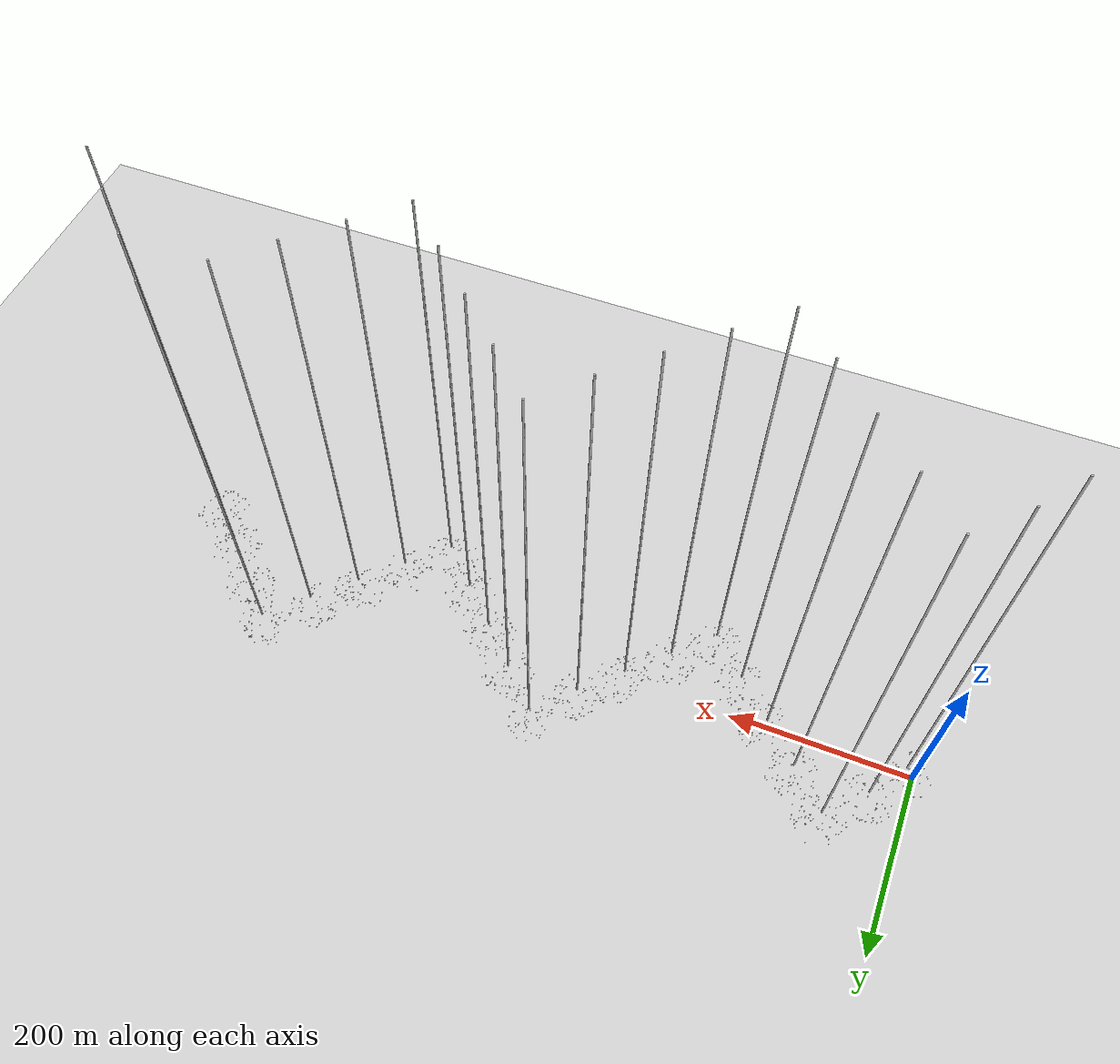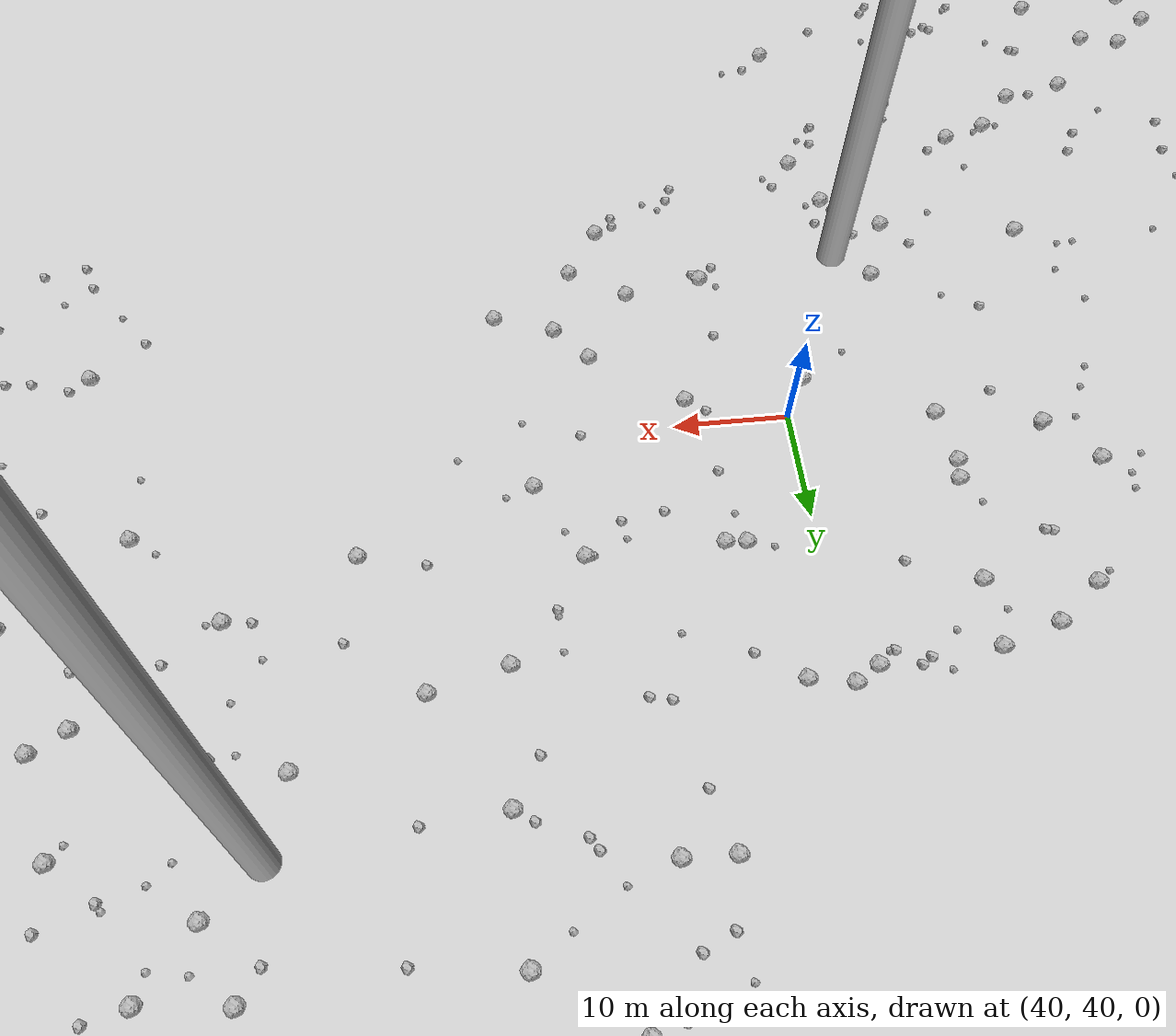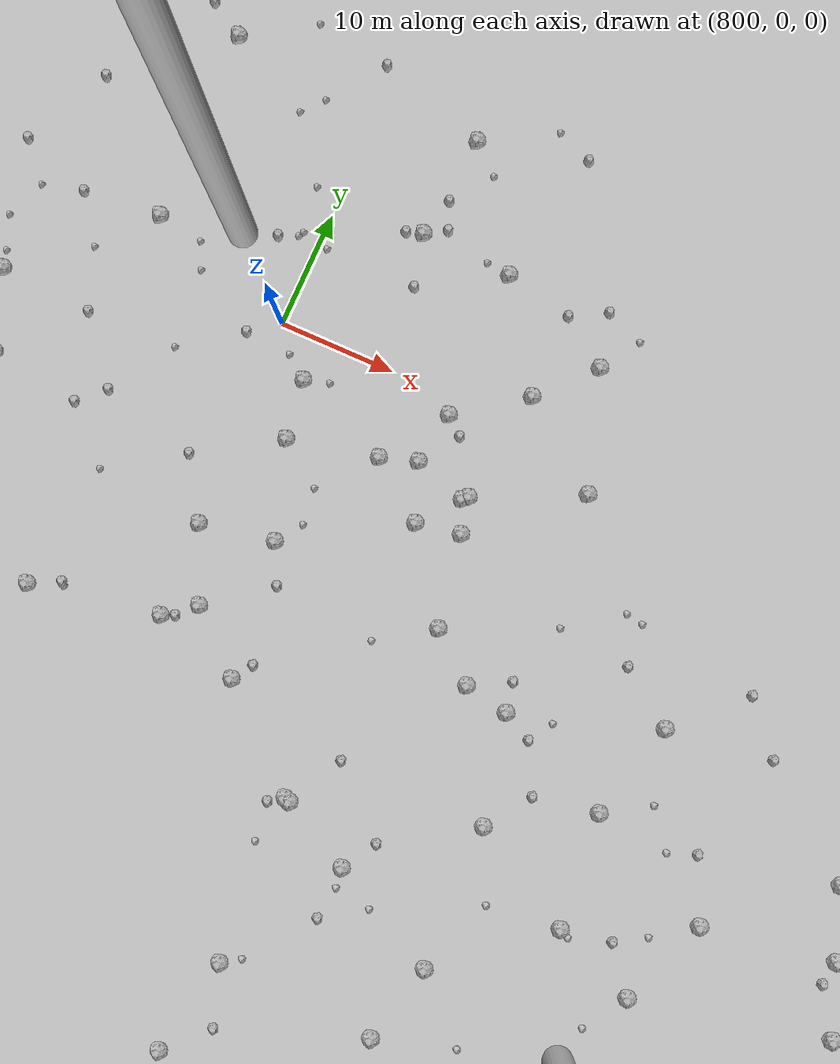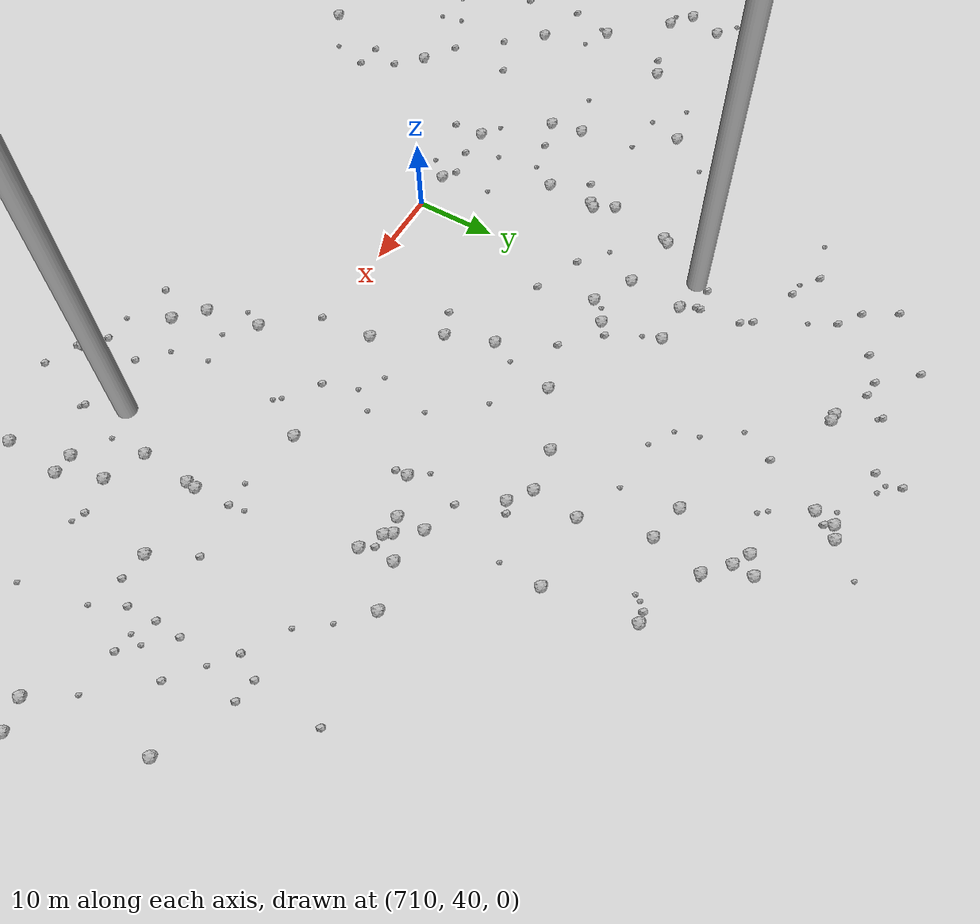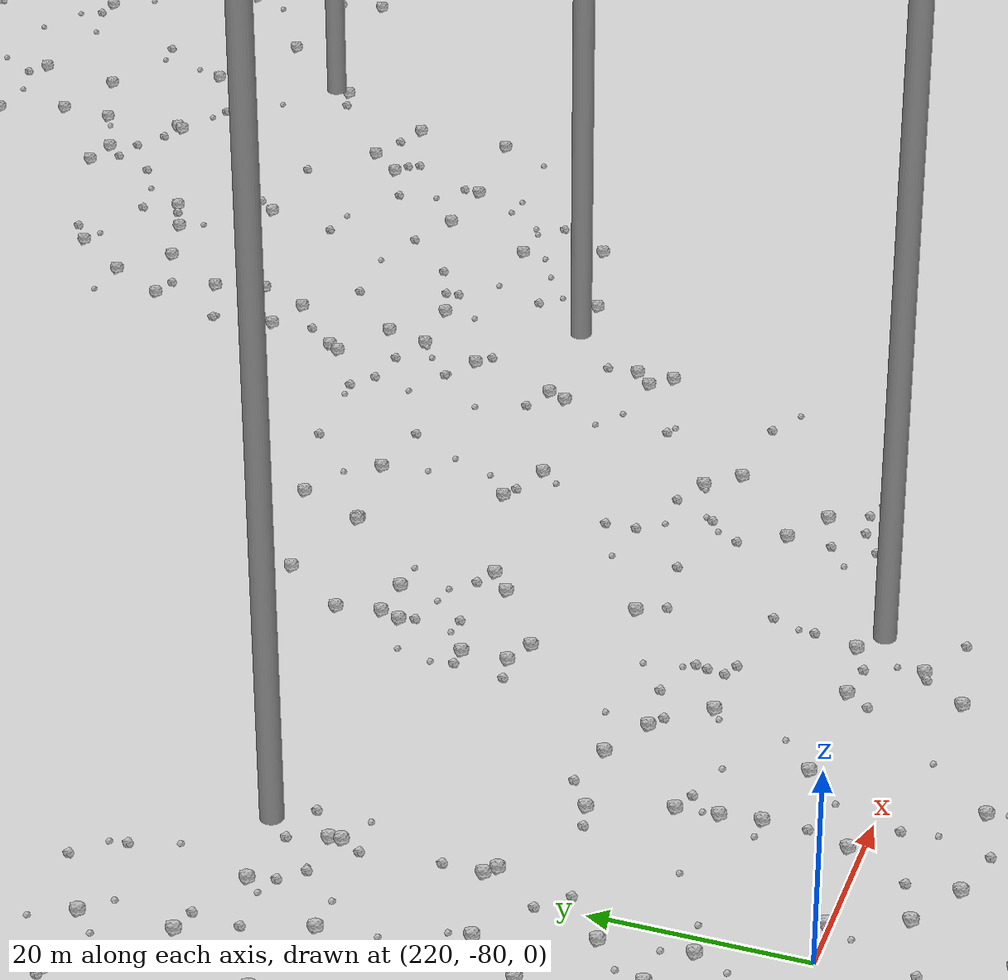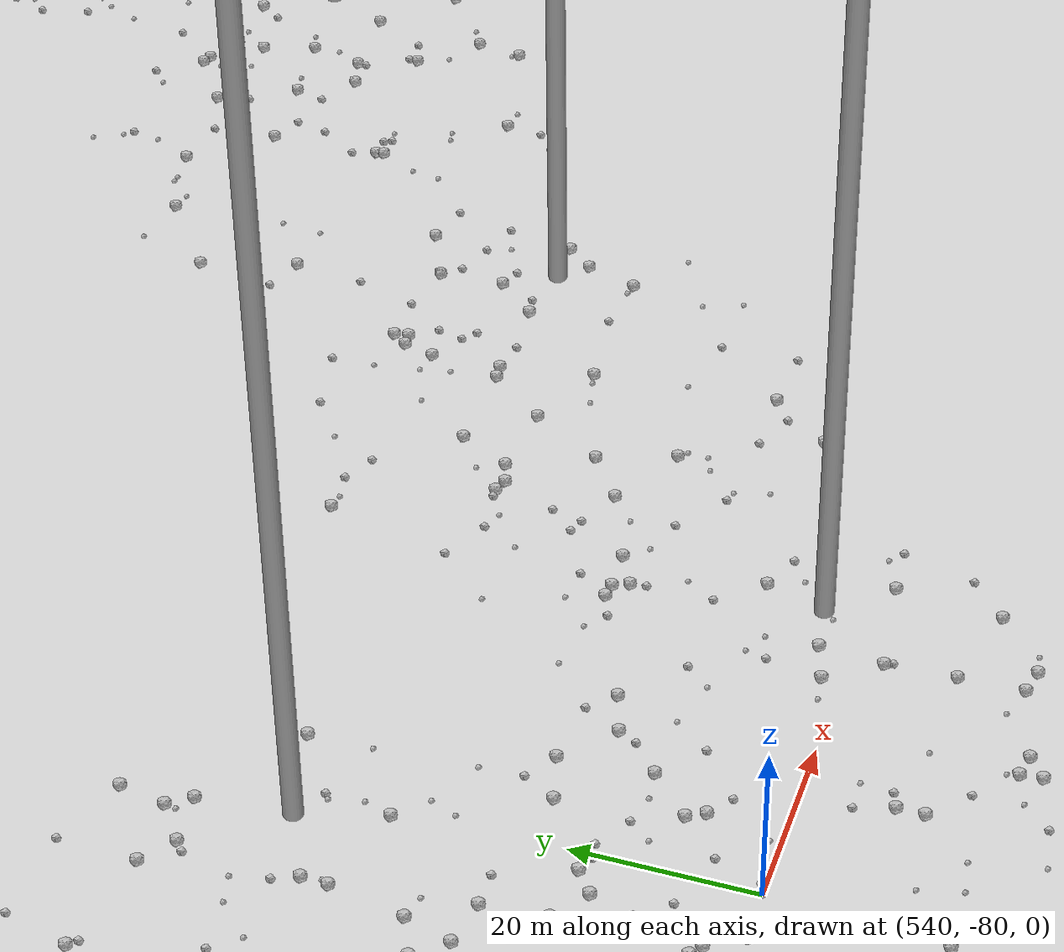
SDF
<sdf version="1.6">
 <world name="default">
  <include><uri>model://custom_ground</uri></include>
  <include><uri>model://sun</uri></include>
  <spherical_coordinates>
   <surface_model>EARTH_WGS84</surface_model>
   <latitude_deg>38.161479</latitude_deg>
   <longitude_deg>-122.454630</longitude_deg>
   <elevation>488.0</elevation>
   <heading_deg>90</heading_deg>
  </spherical_coordinates>
  <model name="rock1_0_0">
   <include><uri>model://rock1</uri><pose>7.194719679248831 -29.674038632898622 0.5 0 0 0</pose></include>
  </model>
  <model name="rock1_0_1">
   <include><uri>model://rock1</uri><pose>-14.422176284251577 -7.9926873129923734 0.5 0 0 0</pose></include>
  </model>
  <model name="rock1_0_2">
   <include><uri>model://rock1</uri><pose>4.676571307307547 2.167790002969781 0.5 0 0 0</pose></include>
  </model>
  <model name="rock1_0_3">
   <include><uri>model://rock1</uri><pose>23.968485967479744 -25.854387474371745 0.5 0 0 0</pose></include>
  </model>
  <model name="rock1_0_4">
   <include><uri>model://rock1</uri><pose>4.981956952170606 -9.829721763964287 0.5 0 0 0</pose></include>
  </model>
  <model name="rock1_0_5">
   <include><uri>model://rock1</uri><pose>-6.2589390600732635 19.214139019803923 0.5 0 0 0</pose></include>
  </model>
  <model name="rock1_0_6">
   <include><uri>model://rock1</uri><pose>-7.204883989042729 -6.803632356733328 0.5 0 0 0</pose></include>
  </model>
  <model name="rock1_0_7">
   <include><uri>model://rock1</uri><pose>23.328180813401993 3.0839254332478205 0.5 0 0 0</pose></include>
  </model>
  <model name="rock1_0_8">
   <include><uri>model://rock1</uri><pose>-2.3878402014707127 -11.582224531477333 0.5 0 0 0</pose></include>
  </model>
  <model name="rock1_0_9">
   <include><uri>model://rock1</uri><pose>34.311573584920566 10.363756497211938 0.5 0 0 0</pose></include>
  </model>
  <model name="rock1_0_10">
   <include><uri>model://rock1</uri><pose>-5.746836371098743 -10.48014084062103 0.5 0 0 0</pose></include>
  </model>
  <model name="rock1_0_11">
   <include><uri>model://rock1</uri><pose>8.290646387585578 -28.944192617482734 0.5 0 0 0</pose></include>
  </model>
  <model name="rock1_0_12">
   <include><uri>model://rock1</uri><pose>14.75129127801754 21.237211640266707 0.5 0 0 0</pose></include>
  </model>
  <model name="rock1_0_13">
   <include><uri>model://rock1</uri><pose>32.21936253638688 15.542467556911568 0.5 0 0 0</pose></include>
  </model>
  <model name="rock1_0_14">
   <include><uri>model://rock1</uri><pose>-3.2736035778547397 -14.639738002310576 0.5 0 0 0</pose></include>
  </model>
  <model name="rock1_0_15">
   <include><uri>model://rock1</uri><pose>-8.695959737747806 2.2786819494655433 0.5 0 0 0</pose></include>
  </model>
  <model name="rock1_0_16">
   <include><uri>model://rock1</uri><pose>-8.601953288199095 -16.701661458819892 0.5 0 0 0</pose></include>
  </model>
  <model name="rock1_0_17">
   <include><uri>model://rock1</uri><pose>18.778514433086897 -9.426638785557323 0.5 0 0 0</pose></include>
  </model>
  <model name="rock1_0_18">
   <include><uri>model://rock1</uri><pose>14.003405809494083 7.181382702019455 0.5 0 0 0</pose></include>
  </model>
  <model name="rock1_0_19">
   <include><uri>model://rock1</uri><pose>10.46239804766515 3.3792231676583953 0.5 0 0 0</pose></include>
  </model>
  <model name="rock1_0_20">
   <include><uri>model://rock1</uri><pose>-3.0970186812989837 18.48107607295404 0.5 0 0 0</pose></include>
  </model>
  <model name="rock1_0_21">
   <include><uri>model://rock1</uri><pose>0.21321023561882413 -4.448903414307832 0.5 0 0 0</pose></include>
  </model>
  <model name="rock1_0_22">
   <include><uri>model://rock1</uri><pose>34.27116021817934 -5.427096063636753 0.5 0 0 0</pose></include>
  </model>
  <model name="rock1_0_23">
   <include><uri>model://rock1</uri><pose>-3.5249338675828987 -3.5346537828654476 0.5 0 0 0</pose></include>
  </model>
  <model name="rock1_0_24">
   <include><uri>model://rock1</uri><pose>1.2133314672046858 -28.213583644282146 0.5 0 0 0</pose></include>
  </model>
  <model name="rock1_0_25">
   <include><uri>model://rock1</uri><pose>-13.584155241206638 16.684797038590226 0.5 0 0 0</pose></include>
  </model>
  <model name="rock1_0_26">
   <include><uri>model://rock1</uri><pose>18.051316083377166 8.461506361093392 0.5 0 0 0</pose></include>
  </model>
  <model name="rock2_0_0">
   <include><uri>model://rock2</uri><pose>36.42419056518739 -3.5402238457628563 0.3 0 0 0</pose></include>
  </model>
  <model name="rock2_0_1">
   <include><uri>model://rock2</uri><pose>8.035640314398055 -3.6407110278176162 0.3 0 0 0</pose></include>
  </model>
  <model name="rock2_0_2">
   <include><uri>model://rock2</uri><pose>5.151055909027637 9.039730423355962 0.3 0 0 0</pose></include>
  </model>
  <model name="rock2_0_3">
   <include><uri>model://rock2</uri><pose>17.55791027595358 -7.370042252667346 0.3 0 0 0</pose></include>
  </model>
  <model name="rock2_0_4">
   <include><uri>model://rock2</uri><pose>8.05395339562147 -26.95359592157008 0.3 0 0 0</pose></include>
  </model>
  <model name="rock2_0_5">
   <include><uri>model://rock2</uri><pose>22.37639274621914 -10.922244500202435 0.3 0 0 0</pose></include>
  </model>
  <model name="rock2_0_6">
   <include><uri>model://rock2</uri><pose>12.910388908239455 -11.028679555409017 0.3 0 0 0</pose></include>
  </model>
  <model name="rock2_0_7">
   <include><uri>model://rock2</uri><pose>15.625200991703743 -7.632579540214618 0.3 0 0 0</pose></include>
  </model>
  <model name="rock2_0_8">
   <include><uri>model://rock2</uri><pose>-4.678534973455431 16.555508054155375 0.3 0 0 0</pose></include>
  </model>
  <model name="rock2_0_9">
   <include><uri>model://rock2</uri><pose>16.142736114592275 -8.161453644635245 0.3 0 0 0</pose></include>
  </model>
  <model name="rock2_0_10">
   <include><uri>model://rock2</uri><pose>24.943819914010902 21.712068899198144 0.3 0 0 0</pose></include>
  </model>
  <model name="rock2_0_11">
   <include><uri>model://rock2</uri><pose>7.559575627269226 -3.4181141705615943 0.3 0 0 0</pose></include>
  </model>
  <model name="rock2_0_12">
   <include><uri>model://rock2</uri><pose>31.661226781644785 7.776885238005782 0.3 0 0 0</pose></include>
  </model>
  <model name="rock2_0_13">
   <include><uri>model://rock2</uri><pose>-7.735218159915519 -22.710735115213993 0.3 0 0 0</pose></include>
  </model>
  <model name="rock2_0_14">
   <include><uri>model://rock2</uri><pose>31.335954772637415 16.78257668452097 0.3 0 0 0</pose></include>
  </model>
  <model name="rock2_0_15">
   <include><uri>model://rock2</uri><pose>33.23463120752572 18.307701840259575 0.3 0 0 0</pose></include>
  </model>
  <model name="rock2_0_16">
   <include><uri>model://rock2</uri><pose>-9.981557040229447 -15.898148906100412 0.3 0 0 0</pose></include>
  </model>
  <model name="rock2_0_17">
   <include><uri>model://rock2</uri><pose>-19.73878746203077 -0.2105033329794317 0.3 0 0 0</pose></include>
  </model>
  <model name="rock2_0_18">
   <include><uri>model://rock2</uri><pose>-3.6234226798449782 8.363150628538257 0.3 0 0 0</pose></include>
  </model>
  <model name="rock2_0_19">
   <include><uri>model://rock2</uri><pose>-15.920933664964211 -6.39678579305642 0.3 0 0 0</pose></include>
  </model>
  <model name="rock2_0_20">
   <include><uri>model://rock2</uri><pose>20.17509957622881 9.923617281017862 0.3 0 0 0</pose></include>
  </model>
  <model name="rock2_0_21">
   <include><uri>model://rock2</uri><pose>-2.965558405603854 12.251817918860844 0.3 0 0 0</pose></include>
  </model>
  <model name="rock2_0_22">
   <include><uri>model://rock2</uri><pose>31.14385164855166 5.527359264890386 0.3 0 0 0</pose></include>
  </model>
  <model name="rock2_0_23">
   <include><uri>model://rock2</uri><pose>28.442088223103617 -8.664586513007958 0.3 0 0 0</pose></include>
  </model>
  <model name="rock2_0_24">
   <include><uri>model://rock2</uri><pose>6.409640853463337 11.451273428896158 0.3 0 0 0</pose></include>
  </model>
  <model name="rock2_0_25">
   <include><uri>model://rock2</uri><pose>21.59068494669276 -11.979053026422072 0.3 0 0 0</pose></include>
  </model>
  <model name="rock2_0_26">
   <include><uri>model://rock2</uri><pose>7.986343199693653 3.16812036107477 0.3 0 0 0</pose></include>
  </model>
  <model name="rock3_0_0">
   <include><uri>model://rock3</uri><pose>9.478546167936035 22.95317313717947 0.2 0 0 0</pose></include>
  </model>
  <model name="rock3_0_1">
   <include><uri>model://rock3</uri><pose>16.5552376184716 -19.425986937096738 0.2 0 0 0</pose></include>
  </model>
  <model name="rock3_0_2">
   <include><uri>model://rock3</uri><pose>19.02875438897602 -7.992806672472824 0.2 0 0 0</pose></include>
  </model>
  <model name="rock3_0_3">
   <include><uri>model://rock3</uri><pose>12.608289420602219 -13.806076920080383 0.2 0 0 0</pose></include>
  </model>
  <model name="rock3_0_4">
   <include><uri>model://rock3</uri><pose>28.485666251881923 -16.580912758522928 0.2 0 0 0</pose></include>
  </model>
  <model name="rock3_0_5">
   <include><uri>model://rock3</uri><pose>1.402038477645398 22.213475806207505 0.2 0 0 0</pose></include>
  </model>
  <model name="rock3_0_6">
   <include><uri>model://rock3</uri><pose>12.135283461666901 26.173096587236316 0.2 0 0 0</pose></include>
  </model>
  <model name="rock3_0_7">
   <include><uri>model://rock3</uri><pose>12.473148331528463 7.045852713589738 0.2 0 0 0</pose></include>
  </model>
  <model name="rock3_0_8">
   <include><uri>model://rock3</uri><pose>-14.834587929227292 6.8772211690601 0.2 0 0 0</pose></include>
  </model>
  <model name="rock3_0_9">
   <include><uri>model://rock3</uri><pose>31.42398272573604 5.659743660312756 0.2 0 0 0</pose></include>
  </model>
  <model name="rock3_0_10">
   <include><uri>model://rock3</uri><pose>10.1150380660923 -5.163413553202709 0.2 0 0 0</pose></include>
  </model>
  <model name="rock3_0_11">
   <include><uri>model://rock3</uri><pose>11.014821028595797 23.053227332925147 0.2 0 0 0</pose></include>
  </model>
  <model name="rock3_0_12">
   <include><uri>model://rock3</uri><pose>17.064340206290765 12.336595997326853 0.2 0 0 0</pose></include>
  </model>
  <model name="rock3_0_13">
   <include><uri>model://rock3</uri><pose>-9.846194642719261 9.634579017799176 0.2 0 0 0</pose></include>
  </model>
  <model name="rock3_0_14">
   <include><uri>model://rock3</uri><pose>38.531321301536686 -3.3221379596884724 0.2 0 0 0</pose></include>
  </model>
  <model name="rock3_0_15">
   <include><uri>model://rock3</uri><pose>-3.22897288330352 15.636567342755377 0.2 0 0 0</pose></include>
  </model>
  <model name="rock3_0_16">
   <include><uri>model://rock3</uri><pose>37.07549202151853 11.93581774148921 0.2 0 0 0</pose></include>
  </model>
  <model name="rock3_0_17">
   <include><uri>model://rock3</uri><pose>14.89177175044476 7.720696350472977 0.2 0 0 0</pose></include>
  </model>
  <model name="rock3_0_18">
   <include><uri>model://rock3</uri><pose>1.4600802629897771 5.915215262611568 0.2 0 0 0</pose></include>
  </model>
  <model name="rock3_0_19">
   <include><uri>model://rock3</uri><pose>22.175666635963097 17.91558175657508 0.2 0 0 0</pose></include>
  </model>
  <model name="rock3_0_20">
   <include><uri>model://rock3</uri><pose>23.423277351781607 4.97761489349854 0.2 0 0 0</pose></include>
  </model>
  <model name="rock3_0_21">
   <include><uri>model://rock3</uri><pose>13.313964270478223 -10.722877619534096 0.2 0 0 0</pose></include>
  </model>
  <model name="rock3_0_22">
   <include><uri>model://rock3</uri><pose>-9.153093018950925 9.01869925099384 0.2 0 0 0</pose></include>
  </model>
  <model name="rock3_0_23">
   <include><uri>model://rock3</uri><pose>32.70870985355531 7.089987653158332 0.2 0 0 0</pose></include>
  </model>
  <model name="rock3_0_24">
   <include><uri>model://rock3</uri><pose>10.460220303460105 29.87380544961895 0.2 0 0 0</pose></include>
  </model>
  <model name="rock3_0_25">
   <include><uri>model://rock3</uri><pose>6.463105241272128 -17.558936967214866 0.2 0 0 0</pose></include>
  </model>
  <model name="rock3_0_26">
   <include><uri>model://rock3</uri><pose>23.07944872168421 -6.749311692453464 0.2 0 0 0</pose></include>
  </model>
  <model name="rock1_1_0">
   <include><uri>model://rock1</uri><pose>58.93975932671328 52.024517732381895 0.5 0 0 0</pose></include>
  </model>
  <model name="rock1_1_1">
   <include><uri>model://rock1</uri><pose>64.4296981563094 26.837614686367484 0.5 0 0 0</pose></include>
  </model>
  <model name="rock1_1_2">
   <include><uri>model://rock1</uri><pose>57.15855595702687 22.192995402031443 0.5 0 0 0</pose></include>
  </model>
  <model name="rock1_1_3">
   <include><uri>model://rock1</uri><pose>52.25248127812994 25.240586247928796 0.5 0 0 0</pose></include>
  </model>
  <model name="rock1_1_4">
   <include><uri>model://rock1</uri><pose>18.668836098851003 58.575095366798536 0.5 0 0 0</pose></include>
  </model>
  <model name="rock1_1_5">
   <include><uri>model://rock1</uri><pose>27.44907463938332 41.11332208272104 0.5 0 0 0</pose></include>
  </model>
  <model name="rock1_1_6">
   <include><uri>model://rock1</uri><pose>37.617959009737035 63.8098624200171 0.5 0 0 0</pose></include>
  </model>
  <model name="rock1_1_7">
   <include><uri>model://rock1</uri><pose>43.26523798029063 64.3658338697955 0.5 0 0 0</pose></include>
  </model>
  <model name="rock1_1_8">
   <include><uri>model://rock1</uri><pose>54.2132753364468 17.51935131714266 0.5 0 0 0</pose></include>
  </model>
  <model name="rock1_1_9">
   <include><uri>model://rock1</uri><pose>56.437641605084345 32.078584499122826 0.5 0 0 0</pose></include>
  </model>
  <model name="rock1_1_10">
   <include><uri>model://rock1</uri><pose>27.096955223117362 47.899046939894475 0.5 0 0 0</pose></include>
  </model>
  <model name="rock1_1_11">
   <include><uri>model://rock1</uri><pose>62.47743315895889 45.000144820194095 0.5 0 0 0</pose></include>
  </model>
  <model name="rock1_1_12">
   <include><uri>model://rock1</uri><pose>22.6848233357905 61.71078091179973 0.5 0 0 0</pose></include>
  </model>
  <model name="rock1_1_13">
   <include><uri>model://rock1</uri><pose>14.655503012476391 47.11041211482347 0.5 0 0 0</pose></include>
  </model>
  <model name="rock1_1_14">
   <include><uri>model://rock1</uri><pose>47.505199824214095 51.86588092585515 0.5 0 0 0</pose></include>
  </model>
  <model name="rock1_1_15">
   <include><uri>model://rock1</uri><pose>48.67813782155434 37.5471468539575 0.5 0 0 0</pose></include>
  </model>
  <model name="rock1_1_16">
   <include><uri>model://rock1</uri><pose>45.77503992885919 52.04184551560506 0.5 0 0 0</pose></include>
  </model>
  <model name="rock1_1_17">
   <include><uri>model://rock1</uri><pose>59.22659698783339 28.733377041932762 0.5 0 0 0</pose></include>
  </model>
  <model name="rock1_1_18">
   <include><uri>model://rock1</uri><pose>18.54075521100026 42.95863449847742 0.5 0 0 0</pose></include>
  </model>
  <model name="rock1_1_19">
   <include><uri>model://rock1</uri><pose>29.46721227902585 25.182622273357776 0.5 0 0 0</pose></include>
  </model>
  <model name="rock1_1_20">
   <include><uri>model://rock1</uri><pose>27.667141549747022 57.40441109931174 0.5 0 0 0</pose></include>
  </model>
  <model name="rock1_1_21">
   <include><uri>model://rock1</uri><pose>39.665228460107556 65.07750819166074 0.5 0 0 0</pose></include>
  </model>
  <model name="rock1_1_22">
   <include><uri>model://rock1</uri><pose>26.755035903069885 46.09304671466732 0.5 0 0 0</pose></include>
  </model>
  <model name="rock1_1_23">
   <include><uri>model://rock1</uri><pose>27.221816785306213 19.182172486453062 0.5 0 0 0</pose></include>
  </model>
  <model name="rock1_1_24">
   <include><uri>model://rock1</uri><pose>38.113843227520874 36.35464248119405 0.5 0 0 0</pose></include>
  </model>
  <model name="rock1_1_25">
   <include><uri>model://rock1</uri><pose>27.70538492221055 63.27947721970402 0.5 0 0 0</pose></include>
  </model>
  <model name="rock1_1_26">
   <include><uri>model://rock1</uri><pose>45.305020136529485 24.099377505749686 0.5 0 0 0</pose></include>
  </model>
  <model name="rock2_1_0">
   <include><uri>model://rock2</uri><pose>20.394752490876016 29.846182177030013 0.3 0 0 0</pose></include>
  </model>
  <model name="rock2_1_1">
   <include><uri>model://rock2</uri><pose>36.027104581732345 62.71030320064058 0.3 0 0 0</pose></include>
  </model>
  <model name="rock2_1_2">
   <include><uri>model://rock2</uri><pose>52.51405215593618 15.699668024726108 0.3 0 0 0</pose></include>
  </model>
  <model name="rock2_1_3">
   <include><uri>model://rock2</uri><pose>52.002206645503804 48.46271118024356 0.3 0 0 0</pose></include>
  </model>
  <model name="rock2_1_4">
   <include><uri>model://rock2</uri><pose>21.328280829051664 53.39944082348424 0.3 0 0 0</pose></include>
  </model>
  <model name="rock2_1_5">
   <include><uri>model://rock2</uri><pose>29.96266956624701 20.083590511491348 0.3 0 0 0</pose></include>
  </model>
  <model name="rock2_1_6">
   <include><uri>model://rock2</uri><pose>45.890506600451054 23.42678905698521 0.3 0 0 0</pose></include>
  </model>
  <model name="rock2_1_7">
   <include><uri>model://rock2</uri><pose>46.97416404766651 13.919272831394657 0.3 0 0 0</pose></include>
  </model>
  <model name="rock2_1_8">
   <include><uri>model://rock2</uri><pose>43.965041301605275 22.776098330194614 0.3 0 0 0</pose></include>
  </model>
  <model name="rock2_1_9">
   <include><uri>model://rock2</uri><pose>58.33845841660035 51.984348839197374 0.3 0 0 0</pose></include>
  </model>
  <model name="rock2_1_10">
   <include><uri>model://rock2</uri><pose>45.00874830194578 30.72015782707452 0.3 0 0 0</pose></include>
  </model>
  <model name="rock2_1_11">
   <include><uri>model://rock2</uri><pose>36.42624003130037 13.202977900560436 0.3 0 0 0</pose></include>
  </model>
  <model name="rock2_1_12">
   <include><uri>model://rock2</uri><pose>46.90339388066489 61.812300154160155 0.3 0 0 0</pose></include>
  </model>
  <model name="rock2_1_13">
   <include><uri>model://rock2</uri><pose>58.03711877037054 40.235707440467614 0.3 0 0 0</pose></include>
  </model>
  <model name="rock2_1_14">
   <include><uri>model://rock2</uri><pose>30.388019072727445 15.957496470454245 0.3 0 0 0</pose></include>
  </model>
  <model name="rock2_1_15">
   <include><uri>model://rock2</uri><pose>33.349520165223126 63.55650203126502 0.3 0 0 0</pose></include>
  </model>
  <model name="rock2_1_16">
   <include><uri>model://rock2</uri><pose>52.50095473829267 16.724049503877815 0.3 0 0 0</pose></include>
  </model>
  <model name="rock2_1_17">
   <include><uri>model://rock2</uri><pose>53.73541904239997 64.98609980670794 0.3 0 0 0</pose></include>
  </model>
  <model name="rock2_1_18">
   <include><uri>model://rock2</uri><pose>18.75683768224557 43.33803031444656 0.3 0 0 0</pose></include>
  </model>
  <model name="rock2_1_19">
   <include><uri>model://rock2</uri><pose>55.63665059667771 49.012842775151256 0.3 0 0 0</pose></include>
  </model>
  <model name="rock2_1_20">
   <include><uri>model://rock2</uri><pose>22.026184952795546 39.24566151859449 0.3 0 0 0</pose></include>
  </model>
  <model name="rock2_1_21">
   <include><uri>model://rock2</uri><pose>46.99042880916965 38.801760451874074 0.3 0 0 0</pose></include>
  </model>
  <model name="rock2_1_22">
   <include><uri>model://rock2</uri><pose>46.3786960601739 12.49671661690217 0.3 0 0 0</pose></include>
  </model>
  <model name="rock2_1_23">
   <include><uri>model://rock2</uri><pose>20.69369595774722 53.537673808449426 0.3 0 0 0</pose></include>
  </model>
  <model name="rock2_1_24">
   <include><uri>model://rock2</uri><pose>34.21146309673773 64.13756376254936 0.3 0 0 0</pose></include>
  </model>
  <model name="rock2_1_25">
   <include><uri>model://rock2</uri><pose>46.93081067272518 45.013664134445854 0.3 0 0 0</pose></include>
  </model>
  <model name="rock2_1_26">
   <include><uri>model://rock2</uri><pose>33.41839270910819 55.08284991408279 0.3 0 0 0</pose></include>
  </model>
  <model name="rock3_1_0">
   <include><uri>model://rock3</uri><pose>18.087615950915016 42.26671130644919 0.2 0 0 0</pose></include>
  </model>
  <model name="rock3_1_1">
   <include><uri>model://rock3</uri><pose>13.972124679173987 39.54370601675779 0.2 0 0 0</pose></include>
  </model>
  <model name="rock3_1_2">
   <include><uri>model://rock3</uri><pose>26.327715688544973 60.089970841007855 0.2 0 0 0</pose></include>
  </model>
  <model name="rock3_1_3">
   <include><uri>model://rock3</uri><pose>15.352091335869943 42.61017655252484 0.2 0 0 0</pose></include>
  </model>
  <model name="rock3_1_4">
   <include><uri>model://rock3</uri><pose>43.82441850752934 24.958142299532035 0.2 0 0 0</pose></include>
  </model>
  <model name="rock3_1_5">
   <include><uri>model://rock3</uri><pose>52.19133133527693 59.50244460112514 0.2 0 0 0</pose></include>
  </model>
  <model name="rock3_1_6">
   <include><uri>model://rock3</uri><pose>33.590192864410625 15.865644084413884 0.2 0 0 0</pose></include>
  </model>
  <model name="rock3_1_7">
   <include><uri>model://rock3</uri><pose>12.906836035149503 37.43783683171753 0.2 0 0 0</pose></include>
  </model>
  <model name="rock3_1_8">
   <include><uri>model://rock3</uri><pose>25.609646230258917 50.211461025076204 0.2 0 0 0</pose></include>
  </model>
  <model name="rock3_1_9">
   <include><uri>model://rock3</uri><pose>55.34973431452305 50.634472894024526 0.2 0 0 0</pose></include>
  </model>
  <model name="rock3_1_10">
   <include><uri>model://rock3</uri><pose>46.22143650732027 49.18324597207979 0.2 0 0 0</pose></include>
  </model>
  <model name="rock3_1_11">
   <include><uri>model://rock3</uri><pose>49.20361996533377 14.091783386803563 0.2 0 0 0</pose></include>
  </model>
  <model name="rock3_1_12">
   <include><uri>model://rock3</uri><pose>17.268374086267116 57.57551965636957 0.2 0 0 0</pose></include>
  </model>
  <model name="rock3_1_13">
   <include><uri>model://rock3</uri><pose>47.839797137682865 14.957028149040259 0.2 0 0 0</pose></include>
  </model>
  <model name="rock3_1_14">
   <include><uri>model://rock3</uri><pose>12.581061587441415 50.21551523180567 0.2 0 0 0</pose></include>
  </model>
  <model name="rock3_1_15">
   <include><uri>model://rock3</uri><pose>68.60342334775439 41.63764382947497 0.2 0 0 0</pose></include>
  </model>
  <model name="rock3_1_16">
   <include><uri>model://rock3</uri><pose>12.395045800497757 48.71182651031356 0.2 0 0 0</pose></include>
  </model>
  <model name="rock3_1_17">
   <include><uri>model://rock3</uri><pose>60.30532842913742 49.44577765327831 0.2 0 0 0</pose></include>
  </model>
  <model name="rock3_1_18">
   <include><uri>model://rock3</uri><pose>10.997387072092927 46.90208399787535 0.2 0 0 0</pose></include>
  </model>
  <model name="rock3_1_19">
   <include><uri>model://rock3</uri><pose>33.88976332708717 33.60398096230203 0.2 0 0 0</pose></include>
  </model>
  <model name="rock3_1_20">
   <include><uri>model://rock3</uri><pose>36.42390326753182 62.68268260407463 0.2 0 0 0</pose></include>
  </model>
  <model name="rock3_1_21">
   <include><uri>model://rock3</uri><pose>43.519239383503546 52.5705919502643 0.2 0 0 0</pose></include>
  </model>
  <model name="rock3_1_22">
   <include><uri>model://rock3</uri><pose>64.8217830188452 45.72274393806536 0.2 0 0 0</pose></include>
  </model>
  <model name="rock3_1_23">
   <include><uri>model://rock3</uri><pose>62.859856707201864 38.38343100241224 0.2 0 0 0</pose></include>
  </model>
  <model name="rock3_1_24">
   <include><uri>model://rock3</uri><pose>31.942418180054073 64.71732837047452 0.2 0 0 0</pose></include>
  </model>
  <model name="rock3_1_25">
   <include><uri>model://rock3</uri><pose>30.789470870316393 61.45714365673146 0.2 0 0 0</pose></include>
  </model>
  <model name="rock3_1_26">
   <include><uri>model://rock3</uri><pose>23.43001277132249 28.118514567520524 0.2 0 0 0</pose></include>
  </model>
  <model name="rock1_2_0">
   <include><uri>model://rock1</uri><pose>99.70425222923288 72.68246480214282 0.5 0 0 0</pose></include>
  </model>
  <model name="rock1_2_1">
   <include><uri>model://rock1</uri><pose>78.85588294088834 88.30242089751752 0.5 0 0 0</pose></include>
  </model>
  <model name="rock1_2_2">
   <include><uri>model://rock1</uri><pose>65.7035796118536 60.87921424719788 0.5 0 0 0</pose></include>
  </model>
  <model name="rock1_2_3">
   <include><uri>model://rock1</uri><pose>86.07139798301601 83.75810318887162 0.5 0 0 0</pose></include>
  </model>
  <model name="rock1_2_4">
   <include><uri>model://rock1</uri><pose>72.22748502639342 62.5901394170676 0.5 0 0 0</pose></include>
  </model>
  <model name="rock1_2_5">
   <include><uri>model://rock1</uri><pose>106.48770772650593 90.04977333744941 0.5 0 0 0</pose></include>
  </model>
  <model name="rock1_2_6">
   <include><uri>model://rock1</uri><pose>54.92018973110457 76.97255060410859 0.5 0 0 0</pose></include>
  </model>
  <model name="rock1_2_7">
   <include><uri>model://rock1</uri><pose>66.46557211936012 72.22427788524678 0.5 0 0 0</pose></include>
  </model>
  <model name="rock1_2_8">
   <include><uri>model://rock1</uri><pose>90.61378103909118 89.34068530882509 0.5 0 0 0</pose></include>
  </model>
  <model name="rock1_2_9">
   <include><uri>model://rock1</uri><pose>92.9572089626688 83.01588087920801 0.5 0 0 0</pose></include>
  </model>
  <model name="rock1_2_10">
   <include><uri>model://rock1</uri><pose>67.01353666392683 94.64020893106076 0.5 0 0 0</pose></include>
  </model>
  <model name="rock1_2_11">
   <include><uri>model://rock1</uri><pose>64.42412106387056 96.81349573512225 0.5 0 0 0</pose></include>
  </model>
  <model name="rock1_2_12">
   <include><uri>model://rock1</uri><pose>100.08450082066258 90.43997754762277 0.5 0 0 0</pose></include>
  </model>
  <model name="rock1_2_13">
   <include><uri>model://rock1</uri><pose>58.66812543935687 88.6167375897903 0.5 0 0 0</pose></include>
  </model>
  <model name="rock1_2_14">
   <include><uri>model://rock1</uri><pose>88.79613864612973 66.28342614149904 0.5 0 0 0</pose></include>
  </model>
  <model name="rock1_2_15">
   <include><uri>model://rock1</uri><pose>77.18795542589152 50.148916364035195 0.5 0 0 0</pose></include>
  </model>
  <model name="rock1_2_16">
   <include><uri>model://rock1</uri><pose>101.67156238670738 93.45840331314682 0.5 0 0 0</pose></include>
  </model>
  <model name="rock1_2_17">
   <include><uri>model://rock1</uri><pose>66.20403761425646 83.4985471469089 0.5 0 0 0</pose></include>
  </model>
  <model name="rock1_2_18">
   <include><uri>model://rock1</uri><pose>72.70016079072876 89.33766954735236 0.5 0 0 0</pose></include>
  </model>
  <model name="rock1_2_19">
   <include><uri>model://rock1</uri><pose>87.88922356739448 54.903300058161626 0.5 0 0 0</pose></include>
  </model>
  <model name="rock1_2_20">
   <include><uri>model://rock1</uri><pose>82.60601654453698 67.74823949820504 0.5 0 0 0</pose></include>
  </model>
  <model name="rock1_2_21">
   <include><uri>model://rock1</uri><pose>98.93667836389967 62.72219030234852 0.5 0 0 0</pose></include>
  </model>
  <model name="rock1_2_22">
   <include><uri>model://rock1</uri><pose>76.99063661950667 89.83484973157617 0.5 0 0 0</pose></include>
  </model>
  <model name="rock1_2_23">
   <include><uri>model://rock1</uri><pose>50.80725095181734 77.10973308198987 0.5 0 0 0</pose></include>
  </model>
  <model name="rock1_2_24">
   <include><uri>model://rock1</uri><pose>101.89577338104093 64.31645605167148 0.5 0 0 0</pose></include>
  </model>
  <model name="rock1_2_25">
   <include><uri>model://rock1</uri><pose>106.57633884821165 84.84524508678761 0.5 0 0 0</pose></include>
  </model>
  <model name="rock1_2_26">
   <include><uri>model://rock1</uri><pose>88.70759080836268 77.88469726745002 0.5 0 0 0</pose></include>
  </model>
  <model name="rock2_2_0">
   <include><uri>model://rock2</uri><pose>84.3764839700884 81.32987826847953 0.3 0 0 0</pose></include>
  </model>
  <model name="rock2_2_1">
   <include><uri>model://rock2</uri><pose>64.11154672749971 68.31981407805358 0.3 0 0 0</pose></include>
  </model>
  <model name="rock2_2_2">
   <include><uri>model://rock2</uri><pose>61.18485711062526 74.81373606566908 0.3 0 0 0</pose></include>
  </model>
  <model name="rock2_2_3">
   <include><uri>model://rock2</uri><pose>74.49552973985028 82.42573810899563 0.3 0 0 0</pose></include>
  </model>
  <model name="rock2_2_4">
   <include><uri>model://rock2</uri><pose>98.32179545726905 85.54801715628281 0.3 0 0 0</pose></include>
  </model>
  <model name="rock2_2_5">
   <include><uri>model://rock2</uri><pose>99.30467357869489 57.95434503093752 0.3 0 0 0</pose></include>
  </model>
  <model name="rock2_2_6">
   <include><uri>model://rock2</uri><pose>99.16878014290344 97.47125230425655 0.3 0 0 0</pose></include>
  </model>
  <model name="rock2_2_7">
   <include><uri>model://rock2</uri><pose>85.39831392038471 109.00367730578054 0.3 0 0 0</pose></include>
  </model>
  <model name="rock2_2_8">
   <include><uri>model://rock2</uri><pose>54.401338599686746 83.54917606505532 0.3 0 0 0</pose></include>
  </model>
  <model name="rock2_2_9">
   <include><uri>model://rock2</uri><pose>56.09991280142946 87.80214444795003 0.3 0 0 0</pose></include>
  </model>
  <model name="rock2_2_10">
   <include><uri>model://rock2</uri><pose>85.52432401677363 55.16812399408511 0.3 0 0 0</pose></include>
  </model>
  <model name="rock2_2_11">
   <include><uri>model://rock2</uri><pose>96.28712890656772 83.88401650266061 0.3 0 0 0</pose></include>
  </model>
  <model name="rock2_2_12">
   <include><uri>model://rock2</uri><pose>73.29295563210226 72.76274198104934 0.3 0 0 0</pose></include>
  </model>
  <model name="rock2_2_13">
   <include><uri>model://rock2</uri><pose>51.8699741253378 82.34537110586461 0.3 0 0 0</pose></include>
  </model>
  <model name="rock2_2_14">
   <include><uri>model://rock2</uri><pose>57.46521757291543 98.80350844077867 0.3 0 0 0</pose></include>
  </model>
  <model name="rock2_2_15">
   <include><uri>model://rock2</uri><pose>61.61818561829101 56.548292684108326 0.3 0 0 0</pose></include>
  </model>
  <model name="rock2_2_16">
   <include><uri>model://rock2</uri><pose>100.10075172053851 77.53058930343417 0.3 0 0 0</pose></include>
  </model>
  <model name="rock2_2_17">
   <include><uri>model://rock2</uri><pose>52.13174009896324 72.1174107939063 0.3 0 0 0</pose></include>
  </model>
  <model name="rock2_2_18">
   <include><uri>model://rock2</uri><pose>108.79290564392241 73.60927700782429 0.3 0 0 0</pose></include>
  </model>
  <model name="rock2_2_19">
   <include><uri>model://rock2</uri><pose>71.67694347206037 51.449000354246 0.3 0 0 0</pose></include>
  </model>
  <model name="rock2_2_20">
   <include><uri>model://rock2</uri><pose>92.39039445892234 58.07442892463352 0.3 0 0 0</pose></include>
  </model>
  <model name="rock2_2_21">
   <include><uri>model://rock2</uri><pose>78.43647642544352 57.7033606145984 0.3 0 0 0</pose></include>
  </model>
  <model name="rock2_2_22">
   <include><uri>model://rock2</uri><pose>64.9420435692934 73.27024057878329 0.3 0 0 0</pose></include>
  </model>
  <model name="rock2_2_23">
   <include><uri>model://rock2</uri><pose>72.01909056710964 96.543540381599 0.3 0 0 0</pose></include>
  </model>
  <model name="rock2_2_24">
   <include><uri>model://rock2</uri><pose>95.91852858610096 75.85616577811194 0.3 0 0 0</pose></include>
  </model>
  <model name="rock2_2_25">
   <include><uri>model://rock2</uri><pose>55.45846854248676 64.58250237615978 0.3 0 0 0</pose></include>
  </model>
  <model name="rock2_2_26">
   <include><uri>model://rock2</uri><pose>60.57034336918054 75.81306890246836 0.3 0 0 0</pose></include>
  </model>
  <model name="rock3_2_0">
   <include><uri>model://rock3</uri><pose>98.87036021778067 85.32757274571135 0.2 0 0 0</pose></include>
  </model>
  <model name="rock3_2_1">
   <include><uri>model://rock3</uri><pose>62.91697098691387 101.54758091641389 0.2 0 0 0</pose></include>
  </model>
  <model name="rock3_2_2">
   <include><uri>model://rock3</uri><pose>90.7596862268451 73.47689222836257 0.2 0 0 0</pose></include>
  </model>
  <model name="rock3_2_3">
   <include><uri>model://rock3</uri><pose>61.49095616576519 60.12584617625173 0.2 0 0 0</pose></include>
  </model>
  <model name="rock3_2_4">
   <include><uri>model://rock3</uri><pose>61.5939270068387 57.01619605630352 0.2 0 0 0</pose></include>
  </model>
  <model name="rock3_2_5">
   <include><uri>model://rock3</uri><pose>94.38149117557123 57.95801687804853 0.2 0 0 0</pose></include>
  </model>
  <model name="rock3_2_6">
   <include><uri>model://rock3</uri><pose>77.0550843870158 98.37220575517392 0.2 0 0 0</pose></include>
  </model>
  <model name="rock3_2_7">
   <include><uri>model://rock3</uri><pose>51.182656716098734 85.77784775260264 0.2 0 0 0</pose></include>
  </model>
  <model name="rock3_2_8">
   <include><uri>model://rock3</uri><pose>102.50236935042119 88.83635848258311 0.2 0 0 0</pose></include>
  </model>
  <model name="rock3_2_9">
   <include><uri>model://rock3</uri><pose>89.21531733703202 81.36896220608342 0.2 0 0 0</pose></include>
  </model>
  <model name="rock3_2_10">
   <include><uri>model://rock3</uri><pose>104.06488153818282 85.89572797998255 0.2 0 0 0</pose></include>
  </model>
  <model name="rock3_2_11">
   <include><uri>model://rock3</uri><pose>85.64096736781579 103.62963691362566 0.2 0 0 0</pose></include>
  </model>
  <model name="rock3_2_12">
   <include><uri>model://rock3</uri><pose>84.65259342305751 58.344019705606094 0.2 0 0 0</pose></include>
  </model>
  <model name="rock3_2_13">
   <include><uri>model://rock3</uri><pose>92.49215540793062 74.9211707265477 0.2 0 0 0</pose></include>
  </model>
  <model name="rock3_2_14">
   <include><uri>model://rock3</uri><pose>89.29882166846521 104.14352507535031 0.2 0 0 0</pose></include>
  </model>
  <model name="rock3_2_15">
   <include><uri>model://rock3</uri><pose>89.12021141457332 54.92439572462867 0.2 0 0 0</pose></include>
  </model>
  <model name="rock3_2_16">
   <include><uri>model://rock3</uri><pose>92.15484094805427 80.81295392993906 0.2 0 0 0</pose></include>
  </model>
  <model name="rock3_2_17">
   <include><uri>model://rock3</uri><pose>100.24273188861748 89.41296772901758 0.2 0 0 0</pose></include>
  </model>
  <model name="rock3_2_18">
   <include><uri>model://rock3</uri><pose>86.49202321997518 65.91817792950994 0.2 0 0 0</pose></include>
  </model>
  <model name="rock3_2_19">
   <include><uri>model://rock3</uri><pose>98.53314404055706 71.4164516621607 0.2 0 0 0</pose></include>
  </model>
  <model name="rock3_2_20">
   <include><uri>model://rock3</uri><pose>95.52006072984014 76.4094914102406 0.2 0 0 0</pose></include>
  </model>
  <model name="rock3_2_21">
   <include><uri>model://rock3</uri><pose>58.919459976233114 78.46835135673092 0.2 0 0 0</pose></include>
  </model>
  <model name="rock3_2_22">
   <include><uri>model://rock3</uri><pose>86.99717002387115 61.70685021212835 0.2 0 0 0</pose></include>
  </model>
  <model name="rock3_2_23">
   <include><uri>model://rock3</uri><pose>102.48229292129716 84.30933125795084 0.2 0 0 0</pose></include>
  </model>
  <model name="rock3_2_24">
   <include><uri>model://rock3</uri><pose>103.62573535500813 84.43087497381904 0.2 0 0 0</pose></include>
  </model>
  <model name="rock3_2_25">
   <include><uri>model://rock3</uri><pose>97.3225704870562 88.84241099695657 0.2 0 0 0</pose></include>
  </model>
  <model name="rock3_2_26">
   <include><uri>model://rock3</uri><pose>63.01210011609133 81.16667979311275 0.2 0 0 0</pose></include>
  </model>
  <model name="rock1_3_0">
   <include><uri>model://rock1</uri><pose>116.10223966750132 53.47504065320401 0.5 0 0 0</pose></include>
  </model>
  <model name="rock1_3_1">
   <include><uri>model://rock1</uri><pose>121.98497223311124 18.68824819061084 0.5 0 0 0</pose></include>
  </model>
  <model name="rock1_3_2">
   <include><uri>model://rock1</uri><pose>95.5528805555301 46.64046130069371 0.5 0 0 0</pose></include>
  </model>
  <model name="rock1_3_3">
   <include><uri>model://rock1</uri><pose>110.18868195708272 61.79160216114004 0.5 0 0 0</pose></include>
  </model>
  <model name="rock1_3_4">
   <include><uri>model://rock1</uri><pose>105.43170130044433 53.67591787254405 0.5 0 0 0</pose></include>
  </model>
  <model name="rock1_3_5">
   <include><uri>model://rock1</uri><pose>100.11976209175741 29.839142624724285 0.5 0 0 0</pose></include>
  </model>
  <model name="rock1_3_6">
   <include><uri>model://rock1</uri><pose>131.08861103164537 20.757753293484775 0.5 0 0 0</pose></include>
  </model>
  <model name="rock1_3_7">
   <include><uri>model://rock1</uri><pose>130.6555349103162 63.261942910169864 0.5 0 0 0</pose></include>
  </model>
  <model name="rock1_3_8">
   <include><uri>model://rock1</uri><pose>125.44428381939676 50.67158701419843 0.5 0 0 0</pose></include>
  </model>
  <model name="rock1_3_9">
   <include><uri>model://rock1</uri><pose>126.01711650036887 65.6250924275125 0.5 0 0 0</pose></include>
  </model>
  <model name="rock1_3_10">
   <include><uri>model://rock1</uri><pose>107.67165294892472 40.81279624225055 0.5 0 0 0</pose></include>
  </model>
  <model name="rock1_3_11">
   <include><uri>model://rock1</uri><pose>135.56106149859042 25.848082678705254 0.5 0 0 0</pose></include>
  </model>
  <model name="rock1_3_12">
   <include><uri>model://rock1</uri><pose>122.21560836431729 67.46867956358086 0.5 0 0 0</pose></include>
  </model>
  <model name="rock1_3_13">
   <include><uri>model://rock1</uri><pose>121.995362493876 31.034770067183693 0.5 0 0 0</pose></include>
  </model>
  <model name="rock1_3_14">
   <include><uri>model://rock1</uri><pose>110.595012157452 22.95172550661978 0.5 0 0 0</pose></include>
  </model>
  <model name="rock1_3_15">
   <include><uri>model://rock1</uri><pose>112.72370422144425 12.553308332552275 0.5 0 0 0</pose></include>
  </model>
  <model name="rock1_3_16">
   <include><uri>model://rock1</uri><pose>114.28228029161737 49.57631840309003 0.5 0 0 0</pose></include>
  </model>
  <model name="rock1_3_17">
   <include><uri>model://rock1</uri><pose>141.28344193511387 24.78037245632297 0.5 0 0 0</pose></include>
  </model>
  <model name="rock1_3_18">
   <include><uri>model://rock1</uri><pose>136.27269758303157 53.001991881299666 0.5 0 0 0</pose></include>
  </model>
  <model name="rock1_3_19">
   <include><uri>model://rock1</uri><pose>141.20756994763815 24.25586966164859 0.5 0 0 0</pose></include>
  </model>
  <model name="rock1_3_20">
   <include><uri>model://rock1</uri><pose>118.5434886471646 51.24999187450482 0.5 0 0 0</pose></include>
  </model>
  <model name="rock1_3_21">
   <include><uri>model://rock1</uri><pose>138.26053550975237 37.60992331085327 0.5 0 0 0</pose></include>
  </model>
  <model name="rock1_3_22">
   <include><uri>model://rock1</uri><pose>122.80879943531343 17.722476872066615 0.5 0 0 0</pose></include>
  </model>
  <model name="rock1_3_23">
   <include><uri>model://rock1</uri><pose>118.97675927430441 44.55146807563444 0.5 0 0 0</pose></include>
  </model>
  <model name="rock1_3_24">
   <include><uri>model://rock1</uri><pose>131.30659593442306 53.610124084199576 0.5 0 0 0</pose></include>
  </model>
  <model name="rock1_3_25">
   <include><uri>model://rock1</uri><pose>109.58601696592751 49.599898915500056 0.5 0 0 0</pose></include>
  </model>
  <model name="rock1_3_26">
   <include><uri>model://rock1</uri><pose>112.77767341038489 17.195371360955427 0.5 0 0 0</pose></include>
  </model>
  <model name="rock2_3_0">
   <include><uri>model://rock2</uri><pose>105.31475270952849 17.49726140241562 0.3 0 0 0</pose></include>
  </model>
  <model name="rock2_3_1">
   <include><uri>model://rock2</uri><pose>122.56198643733778 17.55489654589521 0.3 0 0 0</pose></include>
  </model>
  <model name="rock2_3_2">
   <include><uri>model://rock2</uri><pose>114.09498354055808 63.49389352357802 0.3 0 0 0</pose></include>
  </model>
  <model name="rock2_3_3">
   <include><uri>model://rock2</uri><pose>143.8960779232807 53.931139005362446 0.3 0 0 0</pose></include>
  </model>
  <model name="rock2_3_4">
   <include><uri>model://rock2</uri><pose>125.91557647801147 61.641636636007284 0.3 0 0 0</pose></include>
  </model>
  <model name="rock2_3_5">
   <include><uri>model://rock2</uri><pose>101.84736360847198 30.99251590409894 0.3 0 0 0</pose></include>
  </model>
  <model name="rock2_3_6">
   <include><uri>model://rock2</uri><pose>121.19243191246326 11.441894196375733 0.3 0 0 0</pose></include>
  </model>
  <model name="rock2_3_7">
   <include><uri>model://rock2</uri><pose>115.77859443456606 41.32774653503736 0.3 0 0 0</pose></include>
  </model>
  <model name="rock2_3_8">
   <include><uri>model://rock2</uri><pose>118.93412225745709 30.71289223223783 0.3 0 0 0</pose></include>
  </model>
  <model name="rock2_3_9">
   <include><uri>model://rock2</uri><pose>139.08597447562252 41.86633297077521 0.3 0 0 0</pose></include>
  </model>
  <model name="rock2_3_10">
   <include><uri>model://rock2</uri><pose>143.41883047861165 55.52670040752888 0.3 0 0 0</pose></include>
  </model>
  <model name="rock2_3_11">
   <include><uri>model://rock2</uri><pose>110.54300389467105 40.536487402078876 0.3 0 0 0</pose></include>
  </model>
  <model name="rock2_3_12">
   <include><uri>model://rock2</uri><pose>105.18936877976407 29.880290890767757 0.3 0 0 0</pose></include>
  </model>
  <model name="rock2_3_13">
   <include><uri>model://rock2</uri><pose>101.54924350594271 16.871251910294273 0.3 0 0 0</pose></include>
  </model>
  <model name="rock2_3_14">
   <include><uri>model://rock2</uri><pose>141.72372432875792 42.852349798912776 0.3 0 0 0</pose></include>
  </model>
  <model name="rock2_3_15">
   <include><uri>model://rock2</uri><pose>146.06346682167074 30.062672724618025 0.3 0 0 0</pose></include>
  </model>
  <model name="rock2_3_16">
   <include><uri>model://rock2</uri><pose>126.43899910374341 26.29695650242832 0.3 0 0 0</pose></include>
  </model>
  <model name="rock2_3_17">
   <include><uri>model://rock2</uri><pose>102.94075404697432 43.32369037112524 0.3 0 0 0</pose></include>
  </model>
  <model name="rock2_3_18">
   <include><uri>model://rock2</uri><pose>107.46534649611988 29.691531220767697 0.3 0 0 0</pose></include>
  </model>
  <model name="rock2_3_19">
   <include><uri>model://rock2</uri><pose>132.25124111467687 25.162471331161058 0.3 0 0 0</pose></include>
  </model>
  <model name="rock2_3_20">
   <include><uri>model://rock2</uri><pose>139.38056871333808 43.04601662881454 0.3 0 0 0</pose></include>
  </model>
  <model name="rock2_3_21">
   <include><uri>model://rock2</uri><pose>95.53872964610375 26.31160887976289 0.3 0 0 0</pose></include>
  </model>
  <model name="rock2_3_22">
   <include><uri>model://rock2</uri><pose>100.70751935876486 19.308267187493513 0.3 0 0 0</pose></include>
  </model>
  <model name="rock2_3_23">
   <include><uri>model://rock2</uri><pose>108.85028883567144 23.28916294691794 0.3 0 0 0</pose></include>
  </model>
  <model name="rock2_3_24">
   <include><uri>model://rock2</uri><pose>133.60692166372755 34.16316921258692 0.3 0 0 0</pose></include>
  </model>
  <model name="rock2_3_25">
   <include><uri>model://rock2</uri><pose>141.17239374535393 56.926120948054674 0.3 0 0 0</pose></include>
  </model>
  <model name="rock2_3_26">
   <include><uri>model://rock2</uri><pose>116.98377163742228 61.22467164055883 0.3 0 0 0</pose></include>
  </model>
  <model name="rock3_3_0">
   <include><uri>model://rock3</uri><pose>93.39465323174308 48.06067665960223 0.2 0 0 0</pose></include>
  </model>
  <model name="rock3_3_1">
   <include><uri>model://rock3</uri><pose>117.92357362227305 55.25668382352601 0.2 0 0 0</pose></include>
  </model>
  <model name="rock3_3_2">
   <include><uri>model://rock3</uri><pose>114.16236815058028 43.78996559509323 0.2 0 0 0</pose></include>
  </model>
  <model name="rock3_3_3">
   <include><uri>model://rock3</uri><pose>122.63015322712918 64.45181446322738 0.2 0 0 0</pose></include>
  </model>
  <model name="rock3_3_4">
   <include><uri>model://rock3</uri><pose>95.05698414091928 40.75842996882845 0.2 0 0 0</pose></include>
  </model>
  <model name="rock3_3_5">
   <include><uri>model://rock3</uri><pose>97.80772782112523 23.03955113827798 0.2 0 0 0</pose></include>
  </model>
  <model name="rock3_3_6">
   <include><uri>model://rock3</uri><pose>131.64725132466194 45.65147731026237 0.2 0 0 0</pose></include>
  </model>
  <model name="rock3_3_7">
   <include><uri>model://rock3</uri><pose>98.32255257744488 53.509595567835355 0.2 0 0 0</pose></include>
  </model>
  <model name="rock3_3_8">
   <include><uri>model://rock3</uri><pose>121.9415517465078 52.11457889414959 0.2 0 0 0</pose></include>
  </model>
  <model name="rock3_3_9">
   <include><uri>model://rock3</uri><pose>139.59985019906674 19.149244694828283 0.2 0 0 0</pose></include>
  </model>
  <model name="rock3_3_10">
   <include><uri>model://rock3</uri><pose>128.9335157280044 19.282379229809486 0.2 0 0 0</pose></include>
  </model>
  <model name="rock3_3_11">
   <include><uri>model://rock3</uri><pose>142.5319729151739 23.578336727093326 0.2 0 0 0</pose></include>
  </model>
  <model name="rock3_3_12">
   <include><uri>model://rock3</uri><pose>131.9928303187923 47.29357846149117 0.2 0 0 0</pose></include>
  </model>
  <model name="rock3_3_13">
   <include><uri>model://rock3</uri><pose>134.7305973721358 62.70797777158739 0.2 0 0 0</pose></include>
  </model>
  <model name="rock3_3_14">
   <include><uri>model://rock3</uri><pose>118.39601735687131 58.06354403227596 0.2 0 0 0</pose></include>
  </model>
  <model name="rock3_3_15">
   <include><uri>model://rock3</uri><pose>143.04097840871256 28.861819841612654 0.2 0 0 0</pose></include>
  </model>
  <model name="rock3_3_16">
   <include><uri>model://rock3</uri><pose>125.27082658335614 17.132938944262047 0.2 0 0 0</pose></include>
  </model>
  <model name="rock3_3_17">
   <include><uri>model://rock3</uri><pose>147.0320503481077 49.85893775525412 0.2 0 0 0</pose></include>
  </model>
  <model name="rock3_3_18">
   <include><uri>model://rock3</uri><pose>124.01639152999756 57.35857061482762 0.2 0 0 0</pose></include>
  </model>
  <model name="rock3_3_19">
   <include><uri>model://rock3</uri><pose>143.95052270462116 55.34902865762899 0.2 0 0 0</pose></include>
  </model>
  <model name="rock3_3_20">
   <include><uri>model://rock3</uri><pose>137.7061028936409 33.09148379669749 0.2 0 0 0</pose></include>
  </model>
  <model name="rock3_3_21">
   <include><uri>model://rock3</uri><pose>105.49728113374505 62.462226715296964 0.2 0 0 0</pose></include>
  </model>
  <model name="rock3_3_22">
   <include><uri>model://rock3</uri><pose>106.75295320907864 38.09866023770329 0.2 0 0 0</pose></include>
  </model>
  <model name="rock3_3_23">
   <include><uri>model://rock3</uri><pose>103.1827901773525 20.90642780854628 0.2 0 0 0</pose></include>
  </model>
  <model name="rock3_3_24">
   <include><uri>model://rock3</uri><pose>125.8783595163704 25.90296088915007 0.2 0 0 0</pose></include>
  </model>
  <model name="rock3_3_25">
   <include><uri>model://rock3</uri><pose>141.05881188717797 31.96007918699486 0.2 0 0 0</pose></include>
  </model>
  <model name="rock3_3_26">
   <include><uri>model://rock3</uri><pose>137.35726812915624 43.27387193912918 0.2 0 0 0</pose></include>
  </model>
  <model name="rock1_4_0">
   <include><uri>model://rock1</uri><pose>133.95743007946254 5.5263345841205265 0.5 0 0 0</pose></include>
  </model>
  <model name="rock1_4_1">
   <include><uri>model://rock1</uri><pose>169.76957042378365 23.714407696185646 0.5 0 0 0</pose></include>
  </model>
  <model name="rock1_4_2">
   <include><uri>model://rock1</uri><pose>177.29037232289147 -18.6127513008162 0.5 0 0 0</pose></include>
  </model>
  <model name="rock1_4_3">
   <include><uri>model://rock1</uri><pose>178.22322640430951 22.167158721694875 0.5 0 0 0</pose></include>
  </model>
  <model name="rock1_4_4">
   <include><uri>model://rock1</uri><pose>176.75358904575535 -3.9160395961522916 0.5 0 0 0</pose></include>
  </model>
  <model name="rock1_4_5">
   <include><uri>model://rock1</uri><pose>150.99168697164066 -20.713417410371235 0.5 0 0 0</pose></include>
  </model>
  <model name="rock1_4_6">
   <include><uri>model://rock1</uri><pose>175.79030171845082 -2.4278279691967555 0.5 0 0 0</pose></include>
  </model>
  <model name="rock1_4_7">
   <include><uri>model://rock1</uri><pose>176.7934814069357 -17.88917487389655 0.5 0 0 0</pose></include>
  </model>
  <model name="rock1_4_8">
   <include><uri>model://rock1</uri><pose>169.45538080616674 21.585780402807238 0.5 0 0 0</pose></include>
  </model>
  <model name="rock1_4_9">
   <include><uri>model://rock1</uri><pose>183.23367770199175 13.517207561971382 0.5 0 0 0</pose></include>
  </model>
  <model name="rock1_4_10">
   <include><uri>model://rock1</uri><pose>130.806711758663 -2.415792800546072 0.5 0 0 0</pose></include>
  </model>
  <model name="rock1_4_11">
   <include><uri>model://rock1</uri><pose>184.3053484129453 13.397635039059132 0.5 0 0 0</pose></include>
  </model>
  <model name="rock1_4_12">
   <include><uri>model://rock1</uri><pose>163.67670990512386 -28.39956730896069 0.5 0 0 0</pose></include>
  </model>
  <model name="rock1_4_13">
   <include><uri>model://rock1</uri><pose>170.64599063002055 10.630516324939492 0.5 0 0 0</pose></include>
  </model>
  <model name="rock1_4_14">
   <include><uri>model://rock1</uri><pose>161.90539224137956 -2.749015519145239 0.5 0 0 0</pose></include>
  </model>
  <model name="rock1_4_15">
   <include><uri>model://rock1</uri><pose>161.96376790843988 7.6679342214143205 0.5 0 0 0</pose></include>
  </model>
  <model name="rock1_4_16">
   <include><uri>model://rock1</uri><pose>174.17047969066425 -26.101369804024326 0.5 0 0 0</pose></include>
  </model>
  <model name="rock1_4_17">
   <include><uri>model://rock1</uri><pose>157.5472442701737 -27.083793510127812 0.5 0 0 0</pose></include>
  </model>
  <model name="rock1_4_18">
   <include><uri>model://rock1</uri><pose>185.8920314042566 -6.488735281730307 0.5 0 0 0</pose></include>
  </model>
  <model name="rock1_4_19">
   <include><uri>model://rock1</uri><pose>189.0547357851238 3.3146280595538826 0.5 0 0 0</pose></include>
  </model>
  <model name="rock1_4_20">
   <include><uri>model://rock1</uri><pose>147.5140478257994 2.123570522675152 0.5 0 0 0</pose></include>
  </model>
  <model name="rock1_4_21">
   <include><uri>model://rock1</uri><pose>169.82938165540276 -19.312541326420423 0.5 0 0 0</pose></include>
  </model>
  <model name="rock1_4_22">
   <include><uri>model://rock1</uri><pose>188.2896396661268 7.22197942891286 0.5 0 0 0</pose></include>
  </model>
  <model name="rock1_4_23">
   <include><uri>model://rock1</uri><pose>174.69197144415128 -2.534296597678871 0.5 0 0 0</pose></include>
  </model>
  <model name="rock1_4_24">
   <include><uri>model://rock1</uri><pose>150.2789815314769 -28.053902911067894 0.5 0 0 0</pose></include>
  </model>
  <model name="rock1_4_25">
   <include><uri>model://rock1</uri><pose>170.45881132654165 -4.478152900177154 0.5 0 0 0</pose></include>
  </model>
  <model name="rock1_4_26">
   <include><uri>model://rock1</uri><pose>157.60685343387195 1.9565105378387422 0.5 0 0 0</pose></include>
  </model>
  <model name="rock2_4_0">
   <include><uri>model://rock2</uri><pose>172.90846826086295 -10.553871654897119 0.3 0 0 0</pose></include>
  </model>
  <model name="rock2_4_1">
   <include><uri>model://rock2</uri><pose>151.05287658480157 -25.66719972786435 0.3 0 0 0</pose></include>
  </model>
  <model name="rock2_4_2">
   <include><uri>model://rock2</uri><pose>177.34699569359674 12.682497809565561 0.3 0 0 0</pose></include>
  </model>
  <model name="rock2_4_3">
   <include><uri>model://rock2</uri><pose>165.6552891857052 19.950193505470466 0.3 0 0 0</pose></include>
  </model>
  <model name="rock2_4_4">
   <include><uri>model://rock2</uri><pose>171.5293532707046 17.291797888024732 0.3 0 0 0</pose></include>
  </model>
  <model name="rock2_4_5">
   <include><uri>model://rock2</uri><pose>164.99802037323047 12.494451238080764 0.3 0 0 0</pose></include>
  </model>
  <model name="rock2_4_6">
   <include><uri>model://rock2</uri><pose>157.58250159054074 7.148104468305583 0.3 0 0 0</pose></include>
  </model>
  <model name="rock2_4_7">
   <include><uri>model://rock2</uri><pose>158.2284435557858 1.0237823241689412 0.3 0 0 0</pose></include>
  </model>
  <model name="rock2_4_8">
   <include><uri>model://rock2</uri><pose>145.59101073328156 -2.6249507534468677 0.3 0 0 0</pose></include>
  </model>
  <model name="rock2_4_9">
   <include><uri>model://rock2</uri><pose>145.71316515370287 -20.78938311766045 0.3 0 0 0</pose></include>
  </model>
  <model name="rock2_4_10">
   <include><uri>model://rock2</uri><pose>161.9187921896881 -19.089178952528233 0.3 0 0 0</pose></include>
  </model>
  <model name="rock2_4_11">
   <include><uri>model://rock2</uri><pose>162.55793865175832 -22.72417809045537 0.3 0 0 0</pose></include>
  </model>
  <model name="rock2_4_12">
   <include><uri>model://rock2</uri><pose>153.10535366372582 -3.3481941900736594 0.3 0 0 0</pose></include>
  </model>
  <model name="rock2_4_13">
   <include><uri>model://rock2</uri><pose>144.02636086568344 9.582593549959292 0.3 0 0 0</pose></include>
  </model>
  <model name="rock2_4_14">
   <include><uri>model://rock2</uri><pose>171.73351437015424 1.3286538831243675 0.3 0 0 0</pose></include>
  </model>
  <model name="rock2_4_15">
   <include><uri>model://rock2</uri><pose>161.5403599618392 -29.021968566036396 0.3 0 0 0</pose></include>
  </model>
  <model name="rock2_4_16">
   <include><uri>model://rock2</uri><pose>161.81023544641454 5.4669897158864345 0.3 0 0 0</pose></include>
  </model>
  <model name="rock2_4_17">
   <include><uri>model://rock2</uri><pose>136.25514286743416 3.6538210163495606 0.3 0 0 0</pose></include>
  </model>
  <model name="rock2_4_18">
   <include><uri>model://rock2</uri><pose>182.7486272364059 17.25177622209427 0.3 0 0 0</pose></include>
  </model>
  <model name="rock2_4_19">
   <include><uri>model://rock2</uri><pose>149.7310537406097 3.3211329681977517 0.3 0 0 0</pose></include>
  </model>
  <model name="rock2_4_20">
   <include><uri>model://rock2</uri><pose>169.87536308874564 12.94183643473837 0.3 0 0 0</pose></include>
  </model>
  <model name="rock2_4_21">
   <include><uri>model://rock2</uri><pose>156.50898871416135 -20.727213339473614 0.3 0 0 0</pose></include>
  </model>
  <model name="rock2_4_22">
   <include><uri>model://rock2</uri><pose>168.4436325005747 8.536764490632308 0.3 0 0 0</pose></include>
  </model>
  <model name="rock2_4_23">
   <include><uri>model://rock2</uri><pose>180.18095551426285 15.64683694077523 0.3 0 0 0</pose></include>
  </model>
  <model name="rock2_4_24">
   <include><uri>model://rock2</uri><pose>161.40396680607904 15.131000928722607 0.3 0 0 0</pose></include>
  </model>
  <model name="rock2_4_25">
   <include><uri>model://rock2</uri><pose>135.56966448953992 6.669709896336919 0.3 0 0 0</pose></include>
  </model>
  <model name="rock2_4_26">
   <include><uri>model://rock2</uri><pose>156.66920765305704 7.22899767446917 0.3 0 0 0</pose></include>
  </model>
  <model name="rock3_4_0">
   <include><uri>model://rock3</uri><pose>184.5114386326538 3.51796118506153 0.2 0 0 0</pose></include>
  </model>
  <model name="rock3_4_1">
   <include><uri>model://rock3</uri><pose>182.93288882960672 7.114459276502252 0.2 0 0 0</pose></include>
  </model>
  <model name="rock3_4_2">
   <include><uri>model://rock3</uri><pose>136.58289438906522 4.92347343225385 0.2 0 0 0</pose></include>
  </model>
  <model name="rock3_4_3">
   <include><uri>model://rock3</uri><pose>161.01577988739908 -7.169330020093849 0.2 0 0 0</pose></include>
  </model>
  <model name="rock3_4_4">
   <include><uri>model://rock3</uri><pose>171.3853486968224 27.180822535404808 0.2 0 0 0</pose></include>
  </model>
  <model name="rock3_4_5">
   <include><uri>model://rock3</uri><pose>171.84608304457456 -17.845042324718882 0.2 0 0 0</pose></include>
  </model>
  <model name="rock3_4_6">
   <include><uri>model://rock3</uri><pose>148.5217198724012 6.802264047040012 0.2 0 0 0</pose></include>
  </model>
  <model name="rock3_4_7">
   <include><uri>model://rock3</uri><pose>178.85883200192157 20.704772552652088 0.2 0 0 0</pose></include>
  </model>
  <model name="rock3_4_8">
   <include><uri>model://rock3</uri><pose>164.78279667661468 -22.399040243882418 0.2 0 0 0</pose></include>
  </model>
  <model name="rock3_4_9">
   <include><uri>model://rock3</uri><pose>185.93062888917285 -1.1670031536726206 0.2 0 0 0</pose></include>
  </model>
  <model name="rock3_4_10">
   <include><uri>model://rock3</uri><pose>160.4713416303589 -17.64578014684209 0.2 0 0 0</pose></include>
  </model>
  <model name="rock3_4_11">
   <include><uri>model://rock3</uri><pose>139.04410266745612 0.4695441739771553 0.2 0 0 0</pose></include>
  </model>
  <model name="rock3_4_12">
   <include><uri>model://rock3</uri><pose>147.3999023380281 -15.718835588827725 0.2 0 0 0</pose></include>
  </model>
  <model name="rock3_4_13">
   <include><uri>model://rock3</uri><pose>154.1315302260661 -9.606248793163445 0.2 0 0 0</pose></include>
  </model>
  <model name="rock3_4_14">
   <include><uri>model://rock3</uri><pose>168.1185976028811 23.10860622455963 0.2 0 0 0</pose></include>
  </model>
  <model name="rock3_4_15">
   <include><uri>model://rock3</uri><pose>157.10054906289744 20.292752467510795 0.2 0 0 0</pose></include>
  </model>
  <model name="rock3_4_16">
   <include><uri>model://rock3</uri><pose>159.40595013192353 -12.171227381357088 0.2 0 0 0</pose></include>
  </model>
  <model name="rock3_4_17">
   <include><uri>model://rock3</uri><pose>139.75313617991705 17.07311531232464 0.2 0 0 0</pose></include>
  </model>
  <model name="rock3_4_18">
   <include><uri>model://rock3</uri><pose>171.27944813707205 -21.766318648097915 0.2 0 0 0</pose></include>
  </model>
  <model name="rock3_4_19">
   <include><uri>model://rock3</uri><pose>140.0104646654534 -5.262800646167005 0.2 0 0 0</pose></include>
  </model>
  <model name="rock3_4_20">
   <include><uri>model://rock3</uri><pose>187.86576821645272 -0.03245401301960271 0.2 0 0 0</pose></include>
  </model>
  <model name="rock3_4_21">
   <include><uri>model://rock3</uri><pose>147.27211866069257 14.575207053133646 0.2 0 0 0</pose></include>
  </model>
  <model name="rock3_4_22">
   <include><uri>model://rock3</uri><pose>146.42874877654273 1.394429095496342 0.2 0 0 0</pose></include>
  </model>
  <model name="rock3_4_23">
   <include><uri>model://rock3</uri><pose>160.41954944689252 -28.66222474502649 0.2 0 0 0</pose></include>
  </model>
  <model name="rock3_4_24">
   <include><uri>model://rock3</uri><pose>178.37235117362692 14.001201879026574 0.2 0 0 0</pose></include>
  </model>
  <model name="rock3_4_25">
   <include><uri>model://rock3</uri><pose>178.35839619531168 -15.784726629128446 0.2 0 0 0</pose></include>
  </model>
  <model name="rock3_4_26">
   <include><uri>model://rock3</uri><pose>162.9740184449014 8.307036113334462 0.2 0 0 0</pose></include>
  </model>
  <model name="rock1_5_0">
   <include><uri>model://rock1</uri><pose>195.67763138259443 -28.264032171716046 0.5 0 0 0</pose></include>
  </model>
  <model name="rock1_5_1">
   <include><uri>model://rock1</uri><pose>206.88626334261724 -27.698400068436825 0.5 0 0 0</pose></include>
  </model>
  <model name="rock1_5_2">
   <include><uri>model://rock1</uri><pose>201.78807586907067 -36.542927621979736 0.5 0 0 0</pose></include>
  </model>
  <model name="rock1_5_3">
   <include><uri>model://rock1</uri><pose>223.51373817012222 -50.888762663260586 0.5 0 0 0</pose></include>
  </model>
  <model name="rock1_5_4">
   <include><uri>model://rock1</uri><pose>215.33130151346668 -30.971757688495202 0.5 0 0 0</pose></include>
  </model>
  <model name="rock1_5_5">
   <include><uri>model://rock1</uri><pose>179.8860413544077 -28.284244528617933 0.5 0 0 0</pose></include>
  </model>
  <model name="rock1_5_6">
   <include><uri>model://rock1</uri><pose>173.23185500206515 -37.14531255987178 0.5 0 0 0</pose></include>
  </model>
  <model name="rock1_5_7">
   <include><uri>model://rock1</uri><pose>210.94495299915388 -38.93125317525601 0.5 0 0 0</pose></include>
  </model>
  <model name="rock1_5_8">
   <include><uri>model://rock1</uri><pose>198.48836038519926 -19.20946526410519 0.5 0 0 0</pose></include>
  </model>
  <model name="rock1_5_9">
   <include><uri>model://rock1</uri><pose>191.9152331254942 -25.742252813924054 0.5 0 0 0</pose></include>
  </model>
  <model name="rock1_5_10">
   <include><uri>model://rock1</uri><pose>206.62897840520347 -18.993163180383604 0.5 0 0 0</pose></include>
  </model>
  <model name="rock1_5_11">
   <include><uri>model://rock1</uri><pose>209.9762016202195 -56.968217522430486 0.5 0 0 0</pose></include>
  </model>
  <model name="rock1_5_12">
   <include><uri>model://rock1</uri><pose>192.16182189248244 -11.078011547298303 0.5 0 0 0</pose></include>
  </model>
  <model name="rock1_5_13">
   <include><uri>model://rock1</uri><pose>192.32802383339356 -24.413906875283843 0.5 0 0 0</pose></include>
  </model>
  <model name="rock1_5_14">
   <include><uri>model://rock1</uri><pose>214.08780350347223 -51.816105664423354 0.5 0 0 0</pose></include>
  </model>
  <model name="rock1_5_15">
   <include><uri>model://rock1</uri><pose>182.56263087719148 -57.43788338233393 0.5 0 0 0</pose></include>
  </model>
  <model name="rock1_5_16">
   <include><uri>model://rock1</uri><pose>182.078378159516 -27.5656926502676 0.5 0 0 0</pose></include>
  </model>
  <model name="rock1_5_17">
   <include><uri>model://rock1</uri><pose>181.91042771767076 -21.006771055839494 0.5 0 0 0</pose></include>
  </model>
  <model name="rock1_5_18">
   <include><uri>model://rock1</uri><pose>197.38868299544245 -48.623879779015596 0.5 0 0 0</pose></include>
  </model>
  <model name="rock1_5_19">
   <include><uri>model://rock1</uri><pose>222.43813877795307 -49.953310821825056 0.5 0 0 0</pose></include>
  </model>
  <model name="rock1_5_20">
   <include><uri>model://rock1</uri><pose>222.82052438374757 -35.64162426980884 0.5 0 0 0</pose></include>
  </model>
  <model name="rock1_5_21">
   <include><uri>model://rock1</uri><pose>196.29702296162935 -63.127000062137526 0.5 0 0 0</pose></include>
  </model>
  <model name="rock1_5_22">
   <include><uri>model://rock1</uri><pose>195.00732572634138 -44.392350475888506 0.5 0 0 0</pose></include>
  </model>
  <model name="rock1_5_23">
   <include><uri>model://rock1</uri><pose>189.4969616573729 -67.1202938336187 0.5 0 0 0</pose></include>
  </model>
  <model name="rock1_5_24">
   <include><uri>model://rock1</uri><pose>216.90325711656376 -61.997646186671545 0.5 0 0 0</pose></include>
  </model>
  <model name="rock1_5_25">
   <include><uri>model://rock1</uri><pose>200.9193613279272 -13.331045223592561 0.5 0 0 0</pose></include>
  </model>
  <model name="rock1_5_26">
   <include><uri>model://rock1</uri><pose>222.96226217254255 -36.73740694732378 0.5 0 0 0</pose></include>
  </model>
  <model name="rock2_5_0">
   <include><uri>model://rock2</uri><pose>192.4621871463823 -64.33619170112918 0.3 0 0 0</pose></include>
  </model>
  <model name="rock2_5_1">
   <include><uri>model://rock2</uri><pose>209.46233487112198 -28.25838252732801 0.3 0 0 0</pose></include>
  </model>
  <model name="rock2_5_2">
   <include><uri>model://rock2</uri><pose>187.1217973887348 -56.65895831109494 0.3 0 0 0</pose></include>
  </model>
  <model name="rock2_5_3">
   <include><uri>model://rock2</uri><pose>197.72397277843757 -19.115982657039595 0.3 0 0 0</pose></include>
  </model>
  <model name="rock2_5_4">
   <include><uri>model://rock2</uri><pose>207.56800605618042 -55.82571275839255 0.3 0 0 0</pose></include>
  </model>
  <model name="rock2_5_5">
   <include><uri>model://rock2</uri><pose>222.55368170953668 -46.119019759060066 0.3 0 0 0</pose></include>
  </model>
  <model name="rock2_5_6">
   <include><uri>model://rock2</uri><pose>190.82200233135876 -24.452213986373323 0.3 0 0 0</pose></include>
  </model>
  <model name="rock2_5_7">
   <include><uri>model://rock2</uri><pose>219.3298127212056 -55.53246657911986 0.3 0 0 0</pose></include>
  </model>
  <model name="rock2_5_8">
   <include><uri>model://rock2</uri><pose>217.85123442736335 -35.44977167167292 0.3 0 0 0</pose></include>
  </model>
  <model name="rock2_5_9">
   <include><uri>model://rock2</uri><pose>207.36387342250322 -67.30443028344351 0.3 0 0 0</pose></include>
  </model>
  <model name="rock2_5_10">
   <include><uri>model://rock2</uri><pose>203.03794289836478 -69.60517412014545 0.3 0 0 0</pose></include>
  </model>
  <model name="rock2_5_11">
   <include><uri>model://rock2</uri><pose>177.6441336043255 -50.81568454380163 0.3 0 0 0</pose></include>
  </model>
  <model name="rock2_5_12">
   <include><uri>model://rock2</uri><pose>184.25557015111755 -64.00078758443854 0.3 0 0 0</pose></include>
  </model>
  <model name="rock2_5_13">
   <include><uri>model://rock2</uri><pose>221.729502346652 -31.992792587155954 0.3 0 0 0</pose></include>
  </model>
  <model name="rock2_5_14">
   <include><uri>model://rock2</uri><pose>177.1413076408341 -23.79440207342499 0.3 0 0 0</pose></include>
  </model>
  <model name="rock2_5_15">
   <include><uri>model://rock2</uri><pose>226.16217714304327 -33.189340038970414 0.3 0 0 0</pose></include>
  </model>
  <model name="rock2_5_16">
   <include><uri>model://rock2</uri><pose>221.76291824495866 -38.785181439368415 0.3 0 0 0</pose></include>
  </model>
  <model name="rock2_5_17">
   <include><uri>model://rock2</uri><pose>215.9661473711771 -33.394009991795244 0.3 0 0 0</pose></include>
  </model>
  <model name="rock2_5_18">
   <include><uri>model://rock2</uri><pose>216.56776605461715 -19.317751117233527 0.3 0 0 0</pose></include>
  </model>
  <model name="rock2_5_19">
   <include><uri>model://rock2</uri><pose>199.8196121127164 -57.813383762726744 0.3 0 0 0</pose></include>
  </model>
  <model name="rock2_5_20">
   <include><uri>model://rock2</uri><pose>207.81366861595916 -64.94500063434734 0.3 0 0 0</pose></include>
  </model>
  <model name="rock2_5_21">
   <include><uri>model://rock2</uri><pose>196.92094558422897 -32.13983691933603 0.3 0 0 0</pose></include>
  </model>
  <model name="rock2_5_22">
   <include><uri>model://rock2</uri><pose>175.55440254737226 -54.33635805738443 0.3 0 0 0</pose></include>
  </model>
  <model name="rock2_5_23">
   <include><uri>model://rock2</uri><pose>190.89140278744438 -12.650619852715195 0.3 0 0 0</pose></include>
  </model>
  <model name="rock2_5_24">
   <include><uri>model://rock2</uri><pose>209.0042772840331 -32.800742921651796 0.3 0 0 0</pose></include>
  </model>
  <model name="rock2_5_25">
   <include><uri>model://rock2</uri><pose>213.61802647882948 -15.00754497421331 0.3 0 0 0</pose></include>
  </model>
  <model name="rock2_5_26">
   <include><uri>model://rock2</uri><pose>194.91692977295696 -37.49754294652628 0.3 0 0 0</pose></include>
  </model>
  <model name="rock3_5_0">
   <include><uri>model://rock3</uri><pose>213.0673799963951 -57.38462330081448 0.2 0 0 0</pose></include>
  </model>
  <model name="rock3_5_1">
   <include><uri>model://rock3</uri><pose>204.76519266491513 -15.106361973977378 0.2 0 0 0</pose></include>
  </model>
  <model name="rock3_5_2">
   <include><uri>model://rock3</uri><pose>218.06526079256585 -23.680755454686597 0.2 0 0 0</pose></include>
  </model>
  <model name="rock3_5_3">
   <include><uri>model://rock3</uri><pose>197.52094158531307 -28.48283742093522 0.2 0 0 0</pose></include>
  </model>
  <model name="rock3_5_4">
   <include><uri>model://rock3</uri><pose>211.44546642285349 -44.33287668913294 0.2 0 0 0</pose></include>
  </model>
  <model name="rock3_5_5">
   <include><uri>model://rock3</uri><pose>209.75679547814792 -51.39250098817034 0.2 0 0 0</pose></include>
  </model>
  <model name="rock3_5_6">
   <include><uri>model://rock3</uri><pose>226.19362884064972 -38.29073800595819 0.2 0 0 0</pose></include>
  </model>
  <model name="rock3_5_7">
   <include><uri>model://rock3</uri><pose>204.21268577506495 -21.16383262347251 0.2 0 0 0</pose></include>
  </model>
  <model name="rock3_5_8">
   <include><uri>model://rock3</uri><pose>208.9797264187673 -21.367101328314284 0.2 0 0 0</pose></include>
  </model>
  <model name="rock3_5_9">
   <include><uri>model://rock3</uri><pose>175.12516558840994 -54.69608282268252 0.2 0 0 0</pose></include>
  </model>
  <model name="rock3_5_10">
   <include><uri>model://rock3</uri><pose>195.22118864044842 -63.17394360965048 0.2 0 0 0</pose></include>
  </model>
  <model name="rock3_5_11">
   <include><uri>model://rock3</uri><pose>210.04842456041638 -46.86362990877457 0.2 0 0 0</pose></include>
  </model>
  <model name="rock3_5_12">
   <include><uri>model://rock3</uri><pose>191.45859947077207 -61.68985627792428 0.2 0 0 0</pose></include>
  </model>
  <model name="rock3_5_13">
   <include><uri>model://rock3</uri><pose>183.58873035076294 -48.974256850168985 0.2 0 0 0</pose></include>
  </model>
  <model name="rock3_5_14">
   <include><uri>model://rock3</uri><pose>214.75301150173243 -38.96858499485728 0.2 0 0 0</pose></include>
  </model>
  <model name="rock3_5_15">
   <include><uri>model://rock3</uri><pose>176.1844512715741 -45.029902258948056 0.2 0 0 0</pose></include>
  </model>
  <model name="rock3_5_16">
   <include><uri>model://rock3</uri><pose>216.4054602843919 -17.647052905094498 0.2 0 0 0</pose></include>
  </model>
  <model name="rock3_5_17">
   <include><uri>model://rock3</uri><pose>213.68096220605193 -64.54937708968886 0.2 0 0 0</pose></include>
  </model>
  <model name="rock3_5_18">
   <include><uri>model://rock3</uri><pose>189.05164244092637 -33.37516539280814 0.2 0 0 0</pose></include>
  </model>
  <model name="rock3_5_19">
   <include><uri>model://rock3</uri><pose>191.92556247400907 -15.083166822141308 0.2 0 0 0</pose></include>
  </model>
  <model name="rock3_5_20">
   <include><uri>model://rock3</uri><pose>208.79112558417893 -59.819627246147846 0.2 0 0 0</pose></include>
  </model>
  <model name="rock3_5_21">
   <include><uri>model://rock3</uri><pose>218.45464980570605 -35.270182536581146 0.2 0 0 0</pose></include>
  </model>
  <model name="rock3_5_22">
   <include><uri>model://rock3</uri><pose>195.31142819390783 -62.49731459223487 0.2 0 0 0</pose></include>
  </model>
  <model name="rock3_5_23">
   <include><uri>model://rock3</uri><pose>177.64796912813324 -33.66644610543563 0.2 0 0 0</pose></include>
  </model>
  <model name="rock3_5_24">
   <include><uri>model://rock3</uri><pose>213.83389779735143 -32.520560564311616 0.2 0 0 0</pose></include>
  </model>
  <model name="rock3_5_25">
   <include><uri>model://rock3</uri><pose>193.45110910926405 -60.24095498349482 0.2 0 0 0</pose></include>
  </model>
  <model name="rock3_5_26">
   <include><uri>model://rock3</uri><pose>213.88659691149815 -49.760362533690255 0.2 0 0 0</pose></include>
  </model>
  <model name="rock1_6_0">
   <include><uri>model://rock1</uri><pose>247.57272760628004 -57.01968386479133 0.5 0 0 0</pose></include>
  </model>
  <model name="rock1_6_1">
   <include><uri>model://rock1</uri><pose>259.61471998773493 -83.1839791472689 0.5 0 0 0</pose></include>
  </model>
  <model name="rock1_6_2">
   <include><uri>model://rock1</uri><pose>227.80225289153304 -86.33755464780998 0.5 0 0 0</pose></include>
  </model>
  <model name="rock1_6_3">
   <include><uri>model://rock1</uri><pose>225.124004257011 -79.65742379517138 0.5 0 0 0</pose></include>
  </model>
  <model name="rock1_6_4">
   <include><uri>model://rock1</uri><pose>230.8496819147756 -103.92960991003318 0.5 0 0 0</pose></include>
  </model>
  <model name="rock1_6_5">
   <include><uri>model://rock1</uri><pose>244.12406648169872 -108.17562930458082 0.5 0 0 0</pose></include>
  </model>
  <model name="rock1_6_6">
   <include><uri>model://rock1</uri><pose>258.0853464611818 -72.77106442656078 0.5 0 0 0</pose></include>
  </model>
  <model name="rock1_6_7">
   <include><uri>model://rock1</uri><pose>215.38801394993772 -92.08477593980666 0.5 0 0 0</pose></include>
  </model>
  <model name="rock1_6_8">
   <include><uri>model://rock1</uri><pose>235.83946739250652 -78.71763073300828 0.5 0 0 0</pose></include>
  </model>
  <model name="rock1_6_9">
   <include><uri>model://rock1</uri><pose>236.50972395053253 -62.89363837873117 0.5 0 0 0</pose></include>
  </model>
  <model name="rock1_6_10">
   <include><uri>model://rock1</uri><pose>213.9132097384296 -76.44902986684005 0.5 0 0 0</pose></include>
  </model>
  <model name="rock1_6_11">
   <include><uri>model://rock1</uri><pose>242.53927404543902 -54.46241618405132 0.5 0 0 0</pose></include>
  </model>
  <model name="rock1_6_12">
   <include><uri>model://rock1</uri><pose>244.33367296910916 -89.0179600424007 0.5 0 0 0</pose></include>
  </model>
  <model name="rock1_6_13">
   <include><uri>model://rock1</uri><pose>237.21317398210954 -70.61403089099477 0.5 0 0 0</pose></include>
  </model>
  <model name="rock1_6_14">
   <include><uri>model://rock1</uri><pose>251.86047804622197 -61.974314804329126 0.5 0 0 0</pose></include>
  </model>
  <model name="rock1_6_15">
   <include><uri>model://rock1</uri><pose>224.39508776784365 -96.11018587072635 0.5 0 0 0</pose></include>
  </model>
  <model name="rock1_6_16">
   <include><uri>model://rock1</uri><pose>217.83290483896323 -70.22858882513273 0.5 0 0 0</pose></include>
  </model>
  <model name="rock1_6_17">
   <include><uri>model://rock1</uri><pose>219.01587095447815 -98.10503116178228 0.5 0 0 0</pose></include>
  </model>
  <model name="rock1_6_18">
   <include><uri>model://rock1</uri><pose>233.07559990355375 -89.40480676927936 0.5 0 0 0</pose></include>
  </model>
  <model name="rock1_6_19">
   <include><uri>model://rock1</uri><pose>212.85520593565917 -67.32676534816387 0.5 0 0 0</pose></include>
  </model>
  <model name="rock1_6_20">
   <include><uri>model://rock1</uri><pose>236.79174850755766 -66.8253335241076 0.5 0 0 0</pose></include>
  </model>
  <model name="rock1_6_21">
   <include><uri>model://rock1</uri><pose>263.5219422330516 -78.69603818713537 0.5 0 0 0</pose></include>
  </model>
  <model name="rock1_6_22">
   <include><uri>model://rock1</uri><pose>231.45396308707123 -95.78219445718918 0.5 0 0 0</pose></include>
  </model>
  <model name="rock1_6_23">
   <include><uri>model://rock1</uri><pose>265.350233897679 -71.78516979169575 0.5 0 0 0</pose></include>
  </model>
  <model name="rock1_6_24">
   <include><uri>model://rock1</uri><pose>221.35151488680535 -97.23762845904074 0.5 0 0 0</pose></include>
  </model>
  <model name="rock1_6_25">
   <include><uri>model://rock1</uri><pose>234.18947587166366 -55.4126203453194 0.5 0 0 0</pose></include>
  </model>
  <model name="rock1_6_26">
   <include><uri>model://rock1</uri><pose>245.5660964793486 -72.6085188214963 0.5 0 0 0</pose></include>
  </model>
  <model name="rock2_6_0">
   <include><uri>model://rock2</uri><pose>220.57013150209974 -92.97704613151741 0.3 0 0 0</pose></include>
  </model>
  <model name="rock2_6_1">
   <include><uri>model://rock2</uri><pose>229.2458624725329 -107.53919892016616 0.3 0 0 0</pose></include>
  </model>
  <model name="rock2_6_2">
   <include><uri>model://rock2</uri><pose>238.40980794162334 -90.76742641521743 0.3 0 0 0</pose></include>
  </model>
  <model name="rock2_6_3">
   <include><uri>model://rock2</uri><pose>238.279938593462 -109.83817210643474 0.3 0 0 0</pose></include>
  </model>
  <model name="rock2_6_4">
   <include><uri>model://rock2</uri><pose>268.8418593071774 -81.40012712545001 0.3 0 0 0</pose></include>
  </model>
  <model name="rock2_6_5">
   <include><uri>model://rock2</uri><pose>238.94751931990226 -103.525321960601 0.3 0 0 0</pose></include>
  </model>
  <model name="rock2_6_6">
   <include><uri>model://rock2</uri><pose>237.5312335530661 -53.20924412125394 0.3 0 0 0</pose></include>
  </model>
  <model name="rock2_6_7">
   <include><uri>model://rock2</uri><pose>257.3951402511993 -61.308440455935994 0.3 0 0 0</pose></include>
  </model>
  <model name="rock2_6_8">
   <include><uri>model://rock2</uri><pose>259.04666754591415 -62.028371375121196 0.3 0 0 0</pose></include>
  </model>
  <model name="rock2_6_9">
   <include><uri>model://rock2</uri><pose>230.44868868067317 -102.05493626878355 0.3 0 0 0</pose></include>
  </model>
  <model name="rock2_6_10">
   <include><uri>model://rock2</uri><pose>262.35506371708243 -79.18538071123115 0.3 0 0 0</pose></include>
  </model>
  <model name="rock2_6_11">
   <include><uri>model://rock2</uri><pose>263.8331569309958 -97.92796647018716 0.3 0 0 0</pose></include>
  </model>
  <model name="rock2_6_12">
   <include><uri>model://rock2</uri><pose>253.10547109929954 -56.421266735750216 0.3 0 0 0</pose></include>
  </model>
  <model name="rock2_6_13">
   <include><uri>model://rock2</uri><pose>258.03271545402725 -58.386852128018845 0.3 0 0 0</pose></include>
  </model>
  <model name="rock2_6_14">
   <include><uri>model://rock2</uri><pose>243.4840895577461 -109.06290374703912 0.3 0 0 0</pose></include>
  </model>
  <model name="rock2_6_15">
   <include><uri>model://rock2</uri><pose>220.713976718639 -88.57941071383556 0.3 0 0 0</pose></include>
  </model>
  <model name="rock2_6_16">
   <include><uri>model://rock2</uri><pose>232.4953016009587 -84.6564104150676 0.3 0 0 0</pose></include>
  </model>
  <model name="rock2_6_17">
   <include><uri>model://rock2</uri><pose>249.06101832565125 -58.02377843544968 0.3 0 0 0</pose></include>
  </model>
  <model name="rock2_6_18">
   <include><uri>model://rock2</uri><pose>266.44303414752284 -67.44184638776349 0.3 0 0 0</pose></include>
  </model>
  <model name="rock2_6_19">
   <include><uri>model://rock2</uri><pose>237.19035209334035 -74.75415305735643 0.3 0 0 0</pose></include>
  </model>
  <model name="rock2_6_20">
   <include><uri>model://rock2</uri><pose>221.75856511314538 -58.14214278931837 0.3 0 0 0</pose></include>
  </model>
  <model name="rock2_6_21">
   <include><uri>model://rock2</uri><pose>231.47560220471684 -56.007672714396776 0.3 0 0 0</pose></include>
  </model>
  <model name="rock2_6_22">
   <include><uri>model://rock2</uri><pose>262.13643084687556 -73.25171596171852 0.3 0 0 0</pose></include>
  </model>
  <model name="rock2_6_23">
   <include><uri>model://rock2</uri><pose>239.50964516505215 -82.47268666149549 0.3 0 0 0</pose></include>
  </model>
  <model name="rock2_6_24">
   <include><uri>model://rock2</uri><pose>256.4924341074585 -75.08931939187306 0.3 0 0 0</pose></include>
  </model>
  <model name="rock2_6_25">
   <include><uri>model://rock2</uri><pose>257.7128911176107 -59.563778460390765 0.3 0 0 0</pose></include>
  </model>
  <model name="rock2_6_26">
   <include><uri>model://rock2</uri><pose>238.7187229603926 -63.80934772569132 0.3 0 0 0</pose></include>
  </model>
  <model name="rock3_6_0">
   <include><uri>model://rock3</uri><pose>240.90711324807702 -74.99707974225468 0.2 0 0 0</pose></include>
  </model>
  <model name="rock3_6_1">
   <include><uri>model://rock3</uri><pose>250.5624545339198 -62.81331976110061 0.2 0 0 0</pose></include>
  </model>
  <model name="rock3_6_2">
   <include><uri>model://rock3</uri><pose>243.76260855066343 -108.44473042183662 0.2 0 0 0</pose></include>
  </model>
  <model name="rock3_6_3">
   <include><uri>model://rock3</uri><pose>268.2914026382547 -73.89022556618713 0.2 0 0 0</pose></include>
  </model>
  <model name="rock3_6_4">
   <include><uri>model://rock3</uri><pose>256.2120409626161 -94.391697382983 0.2 0 0 0</pose></include>
  </model>
  <model name="rock3_6_5">
   <include><uri>model://rock3</uri><pose>243.46764306190067 -65.19284323934704 0.2 0 0 0</pose></include>
  </model>
  <model name="rock3_6_6">
   <include><uri>model://rock3</uri><pose>221.56456890418295 -69.45669318025307 0.2 0 0 0</pose></include>
  </model>
  <model name="rock3_6_7">
   <include><uri>model://rock3</uri><pose>246.518665121719 -99.49594519095022 0.2 0 0 0</pose></include>
  </model>
  <model name="rock3_6_8">
   <include><uri>model://rock3</uri><pose>236.82959894159444 -65.31016203002213 0.2 0 0 0</pose></include>
  </model>
  <model name="rock3_6_9">
   <include><uri>model://rock3</uri><pose>234.87093417122628 -70.58778345082895 0.2 0 0 0</pose></include>
  </model>
  <model name="rock3_6_10">
   <include><uri>model://rock3</uri><pose>267.9177757134757 -88.07211333863549 0.2 0 0 0</pose></include>
  </model>
  <model name="rock3_6_11">
   <include><uri>model://rock3</uri><pose>250.17019637516543 -82.82088453133592 0.2 0 0 0</pose></include>
  </model>
  <model name="rock3_6_12">
   <include><uri>model://rock3</uri><pose>241.66381350965537 -76.08962730521935 0.2 0 0 0</pose></include>
  </model>
  <model name="rock3_6_13">
   <include><uri>model://rock3</uri><pose>257.4787782920376 -57.30123273602469 0.2 0 0 0</pose></include>
  </model>
  <model name="rock3_6_14">
   <include><uri>model://rock3</uri><pose>227.87532220183581 -65.91805565015582 0.2 0 0 0</pose></include>
  </model>
  <model name="rock3_6_15">
   <include><uri>model://rock3</uri><pose>216.26269244216724 -73.54169885686589 0.2 0 0 0</pose></include>
  </model>
  <model name="rock3_6_16">
   <include><uri>model://rock3</uri><pose>223.81340699836147 -82.20775566162413 0.2 0 0 0</pose></include>
  </model>
  <model name="rock3_6_17">
   <include><uri>model://rock3</uri><pose>240.03047062239466 -85.79130928309607 0.2 0 0 0</pose></include>
  </model>
  <model name="rock3_6_18">
   <include><uri>model://rock3</uri><pose>217.28894581575605 -67.39876818381931 0.2 0 0 0</pose></include>
  </model>
  <model name="rock3_6_19">
   <include><uri>model://rock3</uri><pose>248.38794169998994 -52.71850533554048 0.2 0 0 0</pose></include>
  </model>
  <model name="rock3_6_20">
   <include><uri>model://rock3</uri><pose>227.9188041502961 -105.35892787719244 0.2 0 0 0</pose></include>
  </model>
  <model name="rock3_6_21">
   <include><uri>model://rock3</uri><pose>244.87119508092562 -90.96844183132441 0.2 0 0 0</pose></include>
  </model>
  <model name="rock3_6_22">
   <include><uri>model://rock3</uri><pose>258.1390327259853 -100.15137717533568 0.2 0 0 0</pose></include>
  </model>
  <model name="rock3_6_23">
   <include><uri>model://rock3</uri><pose>213.4929615862646 -76.83296756933555 0.2 0 0 0</pose></include>
  </model>
  <model name="rock3_6_24">
   <include><uri>model://rock3</uri><pose>263.6928683256639 -76.12751903872908 0.2 0 0 0</pose></include>
  </model>
  <model name="rock3_6_25">
   <include><uri>model://rock3</uri><pose>256.0829836527823 -96.65424718968328 0.2 0 0 0</pose></include>
  </model>
  <model name="rock3_6_26">
   <include><uri>model://rock3</uri><pose>249.4273622296967 -69.40550060036934 0.2 0 0 0</pose></include>
  </model>
  <model name="rock1_7_0">
   <include><uri>model://rock1</uri><pose>279.68400893395585 -32.239250205303215 0.5 0 0 0</pose></include>
  </model>
  <model name="rock1_7_1">
   <include><uri>model://rock1</uri><pose>256.16904020759347 -42.97020470817456 0.5 0 0 0</pose></include>
  </model>
  <model name="rock1_7_2">
   <include><uri>model://rock1</uri><pose>281.42897552958215 -60.660303510726415 0.5 0 0 0</pose></include>
  </model>
  <model name="rock1_7_3">
   <include><uri>model://rock1</uri><pose>285.9055423900922 -63.553569660771146 0.5 0 0 0</pose></include>
  </model>
  <model name="rock1_7_4">
   <include><uri>model://rock1</uri><pose>306.12868399688557 -41.7299488535483 0.5 0 0 0</pose></include>
  </model>
  <model name="rock1_7_5">
   <include><uri>model://rock1</uri><pose>271.1080894646135 -20.117349822839387 0.5 0 0 0</pose></include>
  </model>
  <model name="rock1_7_6">
   <include><uri>model://rock1</uri><pose>287.8742287388313 -50.37430339857383 0.5 0 0 0</pose></include>
  </model>
  <model name="rock1_7_7">
   <include><uri>model://rock1</uri><pose>285.04237116948946 -34.566679246939174 0.5 0 0 0</pose></include>
  </model>
  <model name="rock1_7_8">
   <include><uri>model://rock1</uri><pose>257.05157044611474 -27.810126146763494 0.5 0 0 0</pose></include>
  </model>
  <model name="rock1_7_9">
   <include><uri>model://rock1</uri><pose>306.1821051289786 -37.8384555206831 0.5 0 0 0</pose></include>
  </model>
  <model name="rock1_7_10">
   <include><uri>model://rock1</uri><pose>263.92742742353903 -37.91612565895498 0.5 0 0 0</pose></include>
  </model>
  <model name="rock1_7_11">
   <include><uri>model://rock1</uri><pose>280.8785283019482 -19.09604396220179 0.5 0 0 0</pose></include>
  </model>
  <model name="rock1_7_12">
   <include><uri>model://rock1</uri><pose>266.5275342065552 -35.88773888775748 0.5 0 0 0</pose></include>
  </model>
  <model name="rock1_7_13">
   <include><uri>model://rock1</uri><pose>261.57733272323446 -28.08807763721402 0.5 0 0 0</pose></include>
  </model>
  <model name="rock1_7_14">
   <include><uri>model://rock1</uri><pose>302.8207478533486 -21.343785989234092 0.5 0 0 0</pose></include>
  </model>
  <model name="rock1_7_15">
   <include><uri>model://rock1</uri><pose>253.26154736837975 -41.658081829064955 0.5 0 0 0</pose></include>
  </model>
  <model name="rock1_7_16">
   <include><uri>model://rock1</uri><pose>261.39448854369243 -17.075085907571605 0.5 0 0 0</pose></include>
  </model>
  <model name="rock1_7_17">
   <include><uri>model://rock1</uri><pose>304.2740438481629 -39.649648012136694 0.5 0 0 0</pose></include>
  </model>
  <model name="rock1_7_18">
   <include><uri>model://rock1</uri><pose>264.7838512285892 -50.504201051338505 0.5 0 0 0</pose></include>
  </model>
  <model name="rock1_7_19">
   <include><uri>model://rock1</uri><pose>290.505776748316 -53.523764634571364 0.5 0 0 0</pose></include>
  </model>
  <model name="rock1_7_20">
   <include><uri>model://rock1</uri><pose>253.21884444321842 -37.157183599858975 0.5 0 0 0</pose></include>
  </model>
  <model name="rock1_7_21">
   <include><uri>model://rock1</uri><pose>298.6973085153161 -32.36561269761418 0.5 0 0 0</pose></include>
  </model>
  <model name="rock1_7_22">
   <include><uri>model://rock1</uri><pose>256.3042915106307 -29.837508199865376 0.5 0 0 0</pose></include>
  </model>
  <model name="rock1_7_23">
   <include><uri>model://rock1</uri><pose>256.35277602225614 -23.527153690535606 0.5 0 0 0</pose></include>
  </model>
  <model name="rock1_7_24">
   <include><uri>model://rock1</uri><pose>274.22305846410825 -13.458940664711093 0.5 0 0 0</pose></include>
  </model>
  <model name="rock1_7_25">
   <include><uri>model://rock1</uri><pose>271.3784856147989 -20.178094592138912 0.5 0 0 0</pose></include>
  </model>
  <model name="rock1_7_26">
   <include><uri>model://rock1</uri><pose>299.6581467456906 -30.40964039392138 0.5 0 0 0</pose></include>
  </model>
  <model name="rock2_7_0">
   <include><uri>model://rock2</uri><pose>272.9865168328988 -52.082363014772156 0.3 0 0 0</pose></include>
  </model>
  <model name="rock2_7_1">
   <include><uri>model://rock2</uri><pose>281.41764650420146 -69.52726000458388 0.3 0 0 0</pose></include>
  </model>
  <model name="rock2_7_2">
   <include><uri>model://rock2</uri><pose>287.54424552860655 -67.31086024057907 0.3 0 0 0</pose></include>
  </model>
  <model name="rock2_7_3">
   <include><uri>model://rock2</uri><pose>287.7308517311913 -20.211050348142102 0.3 0 0 0</pose></include>
  </model>
  <model name="rock2_7_4">
   <include><uri>model://rock2</uri><pose>281.1221573622411 -65.10559012621505 0.3 0 0 0</pose></include>
  </model>
  <model name="rock2_7_5">
   <include><uri>model://rock2</uri><pose>296.411118658341 -28.973536423941802 0.3 0 0 0</pose></include>
  </model>
  <model name="rock2_7_6">
   <include><uri>model://rock2</uri><pose>284.4258662700521 -67.7051310761992 0.3 0 0 0</pose></include>
  </model>
  <model name="rock2_7_7">
   <include><uri>model://rock2</uri><pose>251.12400478136217 -37.09882771992234 0.3 0 0 0</pose></include>
  </model>
  <model name="rock2_7_8">
   <include><uri>model://rock2</uri><pose>257.8665690187538 -35.37337564916883 0.3 0 0 0</pose></include>
  </model>
  <model name="rock2_7_9">
   <include><uri>model://rock2</uri><pose>289.69882078895193 -68.17990148811903 0.3 0 0 0</pose></include>
  </model>
  <model name="rock2_7_10">
   <include><uri>model://rock2</uri><pose>299.7315301956195 -54.01774455886459 0.3 0 0 0</pose></include>
  </model>
  <model name="rock2_7_11">
   <include><uri>model://rock2</uri><pose>250.35434470765483 -42.1657421700627 0.3 0 0 0</pose></include>
  </model>
  <model name="rock2_7_12">
   <include><uri>model://rock2</uri><pose>281.8390227472208 -52.993765093897736 0.3 0 0 0</pose></include>
  </model>
  <model name="rock2_7_13">
   <include><uri>model://rock2</uri><pose>267.64184454727297 -63.11807540585755 0.3 0 0 0</pose></include>
  </model>
  <model name="rock2_7_14">
   <include><uri>model://rock2</uri><pose>304.2556530469732 -22.62842567422922 0.3 0 0 0</pose></include>
  </model>
  <model name="rock2_7_15">
   <include><uri>model://rock2</uri><pose>278.2206650147154 -46.31386855867032 0.3 0 0 0</pose></include>
  </model>
  <model name="rock2_7_16">
   <include><uri>model://rock2</uri><pose>281.2222933335747 -33.04559503697265 0.3 0 0 0</pose></include>
  </model>
  <model name="rock2_7_17">
   <include><uri>model://rock2</uri><pose>256.7820202495426 -31.26483228032007 0.3 0 0 0</pose></include>
  </model>
  <model name="rock2_7_18">
   <include><uri>model://rock2</uri><pose>284.39271156945193 -48.6211925769657 0.3 0 0 0</pose></include>
  </model>
  <model name="rock2_7_19">
   <include><uri>model://rock2</uri><pose>306.12525382715376 -34.62912116986601 0.3 0 0 0</pose></include>
  </model>
  <model name="rock2_7_20">
   <include><uri>model://rock2</uri><pose>257.2417605265167 -27.91023869516301 0.3 0 0 0</pose></include>
  </model>
  <model name="rock2_7_21">
   <include><uri>model://rock2</uri><pose>278.1212251825744 -43.232656921961066 0.3 0 0 0</pose></include>
  </model>
  <model name="rock2_7_22">
   <include><uri>model://rock2</uri><pose>266.08242286947535 -53.16440629648474 0.3 0 0 0</pose></include>
  </model>
  <model name="rock2_7_23">
   <include><uri>model://rock2</uri><pose>279.0351200020513 -56.23630970625163 0.3 0 0 0</pose></include>
  </model>
  <model name="rock2_7_24">
   <include><uri>model://rock2</uri><pose>295.9935829558796 -44.068443359444046 0.3 0 0 0</pose></include>
  </model>
  <model name="rock2_7_25">
   <include><uri>model://rock2</uri><pose>284.6330698939983 -10.955363567827462 0.3 0 0 0</pose></include>
  </model>
  <model name="rock2_7_26">
   <include><uri>model://rock2</uri><pose>264.4821000431608 -34.74578584141091 0.3 0 0 0</pose></include>
  </model>
  <model name="rock3_7_0">
   <include><uri>model://rock3</uri><pose>250.85732697108682 -34.92649665825921 0.2 0 0 0</pose></include>
  </model>
  <model name="rock3_7_1">
   <include><uri>model://rock3</uri><pose>260.4226408696492 -32.24275069997236 0.2 0 0 0</pose></include>
  </model>
  <model name="rock3_7_2">
   <include><uri>model://rock3</uri><pose>303.45519660660773 -56.01377419774759 0.2 0 0 0</pose></include>
  </model>
  <model name="rock3_7_3">
   <include><uri>model://rock3</uri><pose>278.3292282427204 -67.14978026137932 0.2 0 0 0</pose></include>
  </model>
  <model name="rock3_7_4">
   <include><uri>model://rock3</uri><pose>262.6405133081974 -32.618936803352156 0.2 0 0 0</pose></include>
  </model>
  <model name="rock3_7_5">
   <include><uri>model://rock3</uri><pose>281.69816523952824 -23.68653330071956 0.2 0 0 0</pose></include>
  </model>
  <model name="rock3_7_6">
   <include><uri>model://rock3</uri><pose>297.1963520739939 -44.61387400532861 0.2 0 0 0</pose></include>
  </model>
  <model name="rock3_7_7">
   <include><uri>model://rock3</uri><pose>295.3154082709171 -36.72740548209899 0.2 0 0 0</pose></include>
  </model>
  <model name="rock3_7_8">
   <include><uri>model://rock3</uri><pose>298.1533421751623 -38.779423175775094 0.2 0 0 0</pose></include>
  </model>
  <model name="rock3_7_9">
   <include><uri>model://rock3</uri><pose>282.44533865603177 -52.25893795278113 0.2 0 0 0</pose></include>
  </model>
  <model name="rock3_7_10">
   <include><uri>model://rock3</uri><pose>288.09676125569854 -50.522969623832765 0.2 0 0 0</pose></include>
  </model>
  <model name="rock3_7_11">
   <include><uri>model://rock3</uri><pose>283.53620856101577 -36.440657220325 0.2 0 0 0</pose></include>
  </model>
  <model name="rock3_7_12">
   <include><uri>model://rock3</uri><pose>278.9347710207589 -15.779933662892773 0.2 0 0 0</pose></include>
  </model>
  <model name="rock3_7_13">
   <include><uri>model://rock3</uri><pose>280.3192183586161 -54.04184103270062 0.2 0 0 0</pose></include>
  </model>
  <model name="rock3_7_14">
   <include><uri>model://rock3</uri><pose>266.663703279992 -65.88167895715192 0.2 0 0 0</pose></include>
  </model>
  <model name="rock3_7_15">
   <include><uri>model://rock3</uri><pose>256.8717872643451 -53.68984428464879 0.2 0 0 0</pose></include>
  </model>
  <model name="rock3_7_16">
   <include><uri>model://rock3</uri><pose>251.84170196355046 -31.352167602566155 0.2 0 0 0</pose></include>
  </model>
  <model name="rock3_7_17">
   <include><uri>model://rock3</uri><pose>295.4881628643754 -16.629133367093615 0.2 0 0 0</pose></include>
  </model>
  <model name="rock3_7_18">
   <include><uri>model://rock3</uri><pose>284.70957543668396 -25.49631270531819 0.2 0 0 0</pose></include>
  </model>
  <model name="rock3_7_19">
   <include><uri>model://rock3</uri><pose>282.9204780329566 -29.786850535618427 0.2 0 0 0</pose></include>
  </model>
  <model name="rock3_7_20">
   <include><uri>model://rock3</uri><pose>265.00024824321093 -28.308148397433207 0.2 0 0 0</pose></include>
  </model>
  <model name="rock3_7_21">
   <include><uri>model://rock3</uri><pose>273.03775141843323 -45.54273871650071 0.2 0 0 0</pose></include>
  </model>
  <model name="rock3_7_22">
   <include><uri>model://rock3</uri><pose>278.3035300753865 -43.338619397950126 0.2 0 0 0</pose></include>
  </model>
  <model name="rock3_7_23">
   <include><uri>model://rock3</uri><pose>287.133397284644 -50.79793479812105 0.2 0 0 0</pose></include>
  </model>
  <model name="rock3_7_24">
   <include><uri>model://rock3</uri><pose>280.04027173225165 -48.759082652755836 0.2 0 0 0</pose></include>
  </model>
  <model name="rock3_7_25">
   <include><uri>model://rock3</uri><pose>255.9462904252073 -35.16663533366223 0.2 0 0 0</pose></include>
  </model>
  <model name="rock3_7_26">
   <include><uri>model://rock3</uri><pose>294.66386728808254 -24.09383039892164 0.2 0 0 0</pose></include>
  </model>
  <model name="rock1_8_0">
   <include><uri>model://rock1</uri><pose>307.93658498440635 -0.15261950386106804 0.5 0 0 0</pose></include>
  </model>
  <model name="rock1_8_1">
   <include><uri>model://rock1</uri><pose>309.0526749658854 21.598658934717328 0.5 0 0 0</pose></include>
  </model>
  <model name="rock1_8_2">
   <include><uri>model://rock1</uri><pose>304.9287148173123 -15.024507407287558 0.5 0 0 0</pose></include>
  </model>
  <model name="rock1_8_3">
   <include><uri>model://rock1</uri><pose>326.2821106081884 -18.641448661631806 0.5 0 0 0</pose></include>
  </model>
  <model name="rock1_8_4">
   <include><uri>model://rock1</uri><pose>342.4304292345209 4.289537977032779 0.5 0 0 0</pose></include>
  </model>
  <model name="rock1_8_5">
   <include><uri>model://rock1</uri><pose>319.9112816318177 18.88419567574625 0.5 0 0 0</pose></include>
  </model>
  <model name="rock1_8_6">
   <include><uri>model://rock1</uri><pose>330.28416833418953 -9.007736196718362 0.5 0 0 0</pose></include>
  </model>
  <model name="rock1_8_7">
   <include><uri>model://rock1</uri><pose>337.4695201526148 -9.710439882998077 0.5 0 0 0</pose></include>
  </model>
  <model name="rock1_8_8">
   <include><uri>model://rock1</uri><pose>301.4134468319322 -5.7483232612802375 0.5 0 0 0</pose></include>
  </model>
  <model name="rock1_8_9">
   <include><uri>model://rock1</uri><pose>334.5949285279163 -22.259814429758787 0.5 0 0 0</pose></include>
  </model>
  <model name="rock1_8_10">
   <include><uri>model://rock1</uri><pose>310.2824985155379 5.091062119705967 0.5 0 0 0</pose></include>
  </model>
  <model name="rock1_8_11">
   <include><uri>model://rock1</uri><pose>326.32869676546545 10.505986627379578 0.5 0 0 0</pose></include>
  </model>
  <model name="rock1_8_12">
   <include><uri>model://rock1</uri><pose>317.7117369844122 -29.831396931086438 0.5 0 0 0</pose></include>
  </model>
  <model name="rock1_8_13">
   <include><uri>model://rock1</uri><pose>306.13275079964325 -10.619100164009211 0.5 0 0 0</pose></include>
  </model>
  <model name="rock1_8_14">
   <include><uri>model://rock1</uri><pose>329.06247591928235 -26.827940892409416 0.5 0 0 0</pose></include>
  </model>
  <model name="rock1_8_15">
   <include><uri>model://rock1</uri><pose>303.6024382832504 1.5462386267249038 0.5 0 0 0</pose></include>
  </model>
  <model name="rock1_8_16">
   <include><uri>model://rock1</uri><pose>348.5894171731279 -9.037957633119213 0.5 0 0 0</pose></include>
  </model>
  <model name="rock1_8_17">
   <include><uri>model://rock1</uri><pose>349.2300844635071 1.3185720762144015 0.5 0 0 0</pose></include>
  </model>
  <model name="rock1_8_18">
   <include><uri>model://rock1</uri><pose>339.34126270793314 0.8962210244342614 0.5 0 0 0</pose></include>
  </model>
  <model name="rock1_8_19">
   <include><uri>model://rock1</uri><pose>313.7058994698116 17.167300740644862 0.5 0 0 0</pose></include>
  </model>
  <model name="rock1_8_20">
   <include><uri>model://rock1</uri><pose>324.2600840628582 20.852660812057643 0.5 0 0 0</pose></include>
  </model>
  <model name="rock1_8_21">
   <include><uri>model://rock1</uri><pose>318.7543313284026 -28.000450501706634 0.5 0 0 0</pose></include>
  </model>
  <model name="rock1_8_22">
   <include><uri>model://rock1</uri><pose>311.68346956984317 -14.890504462721728 0.5 0 0 0</pose></include>
  </model>
  <model name="rock1_8_23">
   <include><uri>model://rock1</uri><pose>313.8086303495411 27.525270595501915 0.5 0 0 0</pose></include>
  </model>
  <model name="rock1_8_24">
   <include><uri>model://rock1</uri><pose>309.09010895791596 10.230416283689308 0.5 0 0 0</pose></include>
  </model>
  <model name="rock1_8_25">
   <include><uri>model://rock1</uri><pose>300.57397189250815 -6.949229484634628 0.5 0 0 0</pose></include>
  </model>
  <model name="rock1_8_26">
   <include><uri>model://rock1</uri><pose>305.6754623790013 15.67997712293932 0.5 0 0 0</pose></include>
  </model>
  <model name="rock2_8_0">
   <include><uri>model://rock2</uri><pose>336.5155058999252 18.205888094060434 0.3 0 0 0</pose></include>
  </model>
  <model name="rock2_8_1">
   <include><uri>model://rock2</uri><pose>319.6759388106653 -11.83685255366396 0.3 0 0 0</pose></include>
  </model>
  <model name="rock2_8_2">
   <include><uri>model://rock2</uri><pose>296.8195391785676 -12.436975663383361 0.3 0 0 0</pose></include>
  </model>
  <model name="rock2_8_3">
   <include><uri>model://rock2</uri><pose>312.8093849041369 -4.788732985235939 0.3 0 0 0</pose></include>
  </model>
  <model name="rock2_8_4">
   <include><uri>model://rock2</uri><pose>324.3576873540419 3.010432270675892 0.3 0 0 0</pose></include>
  </model>
  <model name="rock2_8_5">
   <include><uri>model://rock2</uri><pose>337.727260181736 -7.9296445441118095 0.3 0 0 0</pose></include>
  </model>
  <model name="rock2_8_6">
   <include><uri>model://rock2</uri><pose>316.5134167501879 -23.647625997036993 0.3 0 0 0</pose></include>
  </model>
  <model name="rock2_8_7">
   <include><uri>model://rock2</uri><pose>316.58650509137635 29.467893825402655 0.3 0 0 0</pose></include>
  </model>
  <model name="rock2_8_8">
   <include><uri>model://rock2</uri><pose>315.50008668495065 -15.007637777159124 0.3 0 0 0</pose></include>
  </model>
  <model name="rock2_8_9">
   <include><uri>model://rock2</uri><pose>322.6852016699676 20.286082925251442 0.3 0 0 0</pose></include>
  </model>
  <model name="rock2_8_10">
   <include><uri>model://rock2</uri><pose>341.44693113101295 -1.2760265401997906 0.3 0 0 0</pose></include>
  </model>
  <model name="rock2_8_11">
   <include><uri>model://rock2</uri><pose>294.5989191629381 -10.525163339714627 0.3 0 0 0</pose></include>
  </model>
  <model name="rock2_8_12">
   <include><uri>model://rock2</uri><pose>330.7589450588576 27.37514143807479 0.3 0 0 0</pose></include>
  </model>
  <model name="rock2_8_13">
   <include><uri>model://rock2</uri><pose>334.18766663155253 -1.4619081027127905 0.3 0 0 0</pose></include>
  </model>
  <model name="rock2_8_14">
   <include><uri>model://rock2</uri><pose>303.9776321145312 -2.7557297159322225 0.3 0 0 0</pose></include>
  </model>
  <model name="rock2_8_15">
   <include><uri>model://rock2</uri><pose>301.1288493348774 -13.109402452108267 0.3 0 0 0</pose></include>
  </model>
  <model name="rock2_8_16">
   <include><uri>model://rock2</uri><pose>299.47757506937006 -19.10365134901908 0.3 0 0 0</pose></include>
  </model>
  <model name="rock2_8_17">
   <include><uri>model://rock2</uri><pose>332.6244814064697 -21.249077236602925 0.3 0 0 0</pose></include>
  </model>
  <model name="rock2_8_18">
   <include><uri>model://rock2</uri><pose>302.87970371422136 8.073080996535118 0.3 0 0 0</pose></include>
  </model>
  <model name="rock2_8_19">
   <include><uri>model://rock2</uri><pose>315.34513646072054 -13.644970361445132 0.3 0 0 0</pose></include>
  </model>
  <model name="rock2_8_20">
   <include><uri>model://rock2</uri><pose>308.22817273756704 14.90090308002825 0.3 0 0 0</pose></include>
  </model>
  <model name="rock2_8_21">
   <include><uri>model://rock2</uri><pose>328.1512225742297 12.526758259340973 0.3 0 0 0</pose></include>
  </model>
  <model name="rock2_8_22">
   <include><uri>model://rock2</uri><pose>340.8433860103103 -0.08933649333995675 0.3 0 0 0</pose></include>
  </model>
  <model name="rock2_8_23">
   <include><uri>model://rock2</uri><pose>346.10038762206125 2.732074990101715 0.3 0 0 0</pose></include>
  </model>
  <model name="rock2_8_24">
   <include><uri>model://rock2</uri><pose>325.22085411499376 -6.541692175314537 0.3 0 0 0</pose></include>
  </model>
  <model name="rock2_8_25">
   <include><uri>model://rock2</uri><pose>336.5711698085529 10.344319733702498 0.3 0 0 0</pose></include>
  </model>
  <model name="rock2_8_26">
   <include><uri>model://rock2</uri><pose>322.6202301909881 24.401793287207298 0.3 0 0 0</pose></include>
  </model>
  <model name="rock3_8_0">
   <include><uri>model://rock3</uri><pose>337.14586172059796 -14.884483668763693 0.2 0 0 0</pose></include>
  </model>
  <model name="rock3_8_1">
   <include><uri>model://rock3</uri><pose>334.58757782925784 -14.515657002974638 0.2 0 0 0</pose></include>
  </model>
  <model name="rock3_8_2">
   <include><uri>model://rock3</uri><pose>311.44977245255967 -18.24009732133095 0.2 0 0 0</pose></include>
  </model>
  <model name="rock3_8_3">
   <include><uri>model://rock3</uri><pose>315.91090214555084 26.60169786149733 0.2 0 0 0</pose></include>
  </model>
  <model name="rock3_8_4">
   <include><uri>model://rock3</uri><pose>304.3798364081466 -15.484735704075174 0.2 0 0 0</pose></include>
  </model>
  <model name="rock3_8_5">
   <include><uri>model://rock3</uri><pose>328.1013876048959 2.3773775729955773 0.2 0 0 0</pose></include>
  </model>
  <model name="rock3_8_6">
   <include><uri>model://rock3</uri><pose>324.9208064068233 14.009678485953543 0.2 0 0 0</pose></include>
  </model>
  <model name="rock3_8_7">
   <include><uri>model://rock3</uri><pose>302.41015876544606 -16.70407261363898 0.2 0 0 0</pose></include>
  </model>
  <model name="rock3_8_8">
   <include><uri>model://rock3</uri><pose>320.0389641260835 -4.566242303799839 0.2 0 0 0</pose></include>
  </model>
  <model name="rock3_8_9">
   <include><uri>model://rock3</uri><pose>298.586682758629 0.5987122493087043 0.2 0 0 0</pose></include>
  </model>
  <model name="rock3_8_10">
   <include><uri>model://rock3</uri><pose>342.22212228792284 18.8751364797467 0.2 0 0 0</pose></include>
  </model>
  <model name="rock3_8_11">
   <include><uri>model://rock3</uri><pose>303.3396381739609 7.757513874815928 0.2 0 0 0</pose></include>
  </model>
  <model name="rock3_8_12">
   <include><uri>model://rock3</uri><pose>299.87660236487665 -19.38336002500252 0.2 0 0 0</pose></include>
  </model>
  <model name="rock3_8_13">
   <include><uri>model://rock3</uri><pose>318.4552411858124 -25.71052060509455 0.2 0 0 0</pose></include>
  </model>
  <model name="rock3_8_14">
   <include><uri>model://rock3</uri><pose>331.8694302768108 -18.272612049462523 0.2 0 0 0</pose></include>
  </model>
  <model name="rock3_8_15">
   <include><uri>model://rock3</uri><pose>292.8400642024253 -10.636838995756996 0.2 0 0 0</pose></include>
  </model>
  <model name="rock3_8_16">
   <include><uri>model://rock3</uri><pose>330.7674573720642 -18.81470646352639 0.2 0 0 0</pose></include>
  </model>
  <model name="rock3_8_17">
   <include><uri>model://rock3</uri><pose>321.24168357310145 16.617171157331484 0.2 0 0 0</pose></include>
  </model>
  <model name="rock3_8_18">
   <include><uri>model://rock3</uri><pose>335.0898017083242 -5.542232594764936 0.2 0 0 0</pose></include>
  </model>
  <model name="rock3_8_19">
   <include><uri>model://rock3</uri><pose>318.8451164717544 -18.471033158128073 0.2 0 0 0</pose></include>
  </model>
  <model name="rock3_8_20">
   <include><uri>model://rock3</uri><pose>305.3732499592132 4.6429389191062995 0.2 0 0 0</pose></include>
  </model>
  <model name="rock3_8_21">
   <include><uri>model://rock3</uri><pose>327.06126893698075 25.271793508495065 0.2 0 0 0</pose></include>
  </model>
  <model name="rock3_8_22">
   <include><uri>model://rock3</uri><pose>325.87937839198463 -21.310120669272045 0.2 0 0 0</pose></include>
  </model>
  <model name="rock3_8_23">
   <include><uri>model://rock3</uri><pose>322.2888528999717 -23.131916863964207 0.2 0 0 0</pose></include>
  </model>
  <model name="rock3_8_24">
   <include><uri>model://rock3</uri><pose>345.9760641086885 -14.46326462587386 0.2 0 0 0</pose></include>
  </model>
  <model name="rock3_8_25">
   <include><uri>model://rock3</uri><pose>327.3748936886698 -24.890505583309515 0.2 0 0 0</pose></include>
  </model>
  <model name="rock3_8_26">
   <include><uri>model://rock3</uri><pose>304.51185417566825 22.32788499783321 0.2 0 0 0</pose></include>
  </model>
  <model name="rock1_9_0">
   <include><uri>model://rock1</uri><pose>341.5333798976244 28.055620866979886 0.5 0 0 0</pose></include>
  </model>
  <model name="rock1_9_1">
   <include><uri>model://rock1</uri><pose>350.6660371323204 48.387280589411475 0.5 0 0 0</pose></include>
  </model>
  <model name="rock1_9_2">
   <include><uri>model://rock1</uri><pose>378.1864297546283 41.215611068182675 0.5 0 0 0</pose></include>
  </model>
  <model name="rock1_9_3">
   <include><uri>model://rock1</uri><pose>371.0502180329785 20.111891833837 0.5 0 0 0</pose></include>
  </model>
  <model name="rock1_9_4">
   <include><uri>model://rock1</uri><pose>364.46675313208215 22.464320968860747 0.5 0 0 0</pose></include>
  </model>
  <model name="rock1_9_5">
   <include><uri>model://rock1</uri><pose>349.10961849837713 39.455930501592945 0.5 0 0 0</pose></include>
  </model>
  <model name="rock1_9_6">
   <include><uri>model://rock1</uri><pose>355.4499168357171 12.455649730010702 0.5 0 0 0</pose></include>
  </model>
  <model name="rock1_9_7">
   <include><uri>model://rock1</uri><pose>351.06343586262295 65.3396595252315 0.5 0 0 0</pose></include>
  </model>
  <model name="rock1_9_8">
   <include><uri>model://rock1</uri><pose>356.1023924326046 64.86113652984523 0.5 0 0 0</pose></include>
  </model>
  <model name="rock1_9_9">
   <include><uri>model://rock1</uri><pose>341.6310228612647 42.22248171419711 0.5 0 0 0</pose></include>
  </model>
  <model name="rock1_9_10">
   <include><uri>model://rock1</uri><pose>350.5384215973671 57.43414143083012 0.5 0 0 0</pose></include>
  </model>
  <model name="rock1_9_11">
   <include><uri>model://rock1</uri><pose>354.4316586104544 28.20222083338248 0.5 0 0 0</pose></include>
  </model>
  <model name="rock1_9_12">
   <include><uri>model://rock1</uri><pose>379.7552223768858 32.952816876719 0.5 0 0 0</pose></include>
  </model>
  <model name="rock1_9_13">
   <include><uri>model://rock1</uri><pose>341.2007412796046 36.583345971955076 0.5 0 0 0</pose></include>
  </model>
  <model name="rock1_9_14">
   <include><uri>model://rock1</uri><pose>377.75615365652754 16.59762673754518 0.5 0 0 0</pose></include>
  </model>
  <model name="rock1_9_15">
   <include><uri>model://rock1</uri><pose>356.77011336159876 60.99559304803162 0.5 0 0 0</pose></include>
  </model>
  <model name="rock1_9_16">
   <include><uri>model://rock1</uri><pose>357.71500742064666 64.89698935723479 0.5 0 0 0</pose></include>
  </model>
  <model name="rock1_9_17">
   <include><uri>model://rock1</uri><pose>368.27224174352324 47.608587906158725 0.5 0 0 0</pose></include>
  </model>
  <model name="rock1_9_18">
   <include><uri>model://rock1</uri><pose>331.04614321422105 34.36323701962692 0.5 0 0 0</pose></include>
  </model>
  <model name="rock1_9_19">
   <include><uri>model://rock1</uri><pose>375.6301015446242 31.840050487594006 0.5 0 0 0</pose></include>
  </model>
  <model name="rock1_9_20">
   <include><uri>model://rock1</uri><pose>377.0891193980811 49.02395773553824 0.5 0 0 0</pose></include>
  </model>
  <model name="rock1_9_21">
   <include><uri>model://rock1</uri><pose>341.0818865151231 27.343566886638058 0.5 0 0 0</pose></include>
  </model>
  <model name="rock1_9_22">
   <include><uri>model://rock1</uri><pose>334.6618472507879 33.52874203471476 0.5 0 0 0</pose></include>
  </model>
  <model name="rock1_9_23">
   <include><uri>model://rock1</uri><pose>382.14696904254987 32.53873853554572 0.5 0 0 0</pose></include>
  </model>
  <model name="rock1_9_24">
   <include><uri>model://rock1</uri><pose>339.4423389290353 49.37240664501532 0.5 0 0 0</pose></include>
  </model>
  <model name="rock1_9_25">
   <include><uri>model://rock1</uri><pose>382.4023201199805 25.06148885716351 0.5 0 0 0</pose></include>
  </model>
  <model name="rock1_9_26">
   <include><uri>model://rock1</uri><pose>371.5214713964722 51.67906917512716 0.5 0 0 0</pose></include>
  </model>
  <model name="rock2_9_0">
   <include><uri>model://rock2</uri><pose>378.2116606654215 54.23768888549655 0.3 0 0 0</pose></include>
  </model>
  <model name="rock2_9_1">
   <include><uri>model://rock2</uri><pose>345.4508380760404 57.737971128513166 0.3 0 0 0</pose></include>
  </model>
  <model name="rock2_9_2">
   <include><uri>model://rock2</uri><pose>380.4863704962592 49.53855867710519 0.3 0 0 0</pose></include>
  </model>
  <model name="rock2_9_3">
   <include><uri>model://rock2</uri><pose>387.55080455066883 51.776727206588404 0.3 0 0 0</pose></include>
  </model>
  <model name="rock2_9_4">
   <include><uri>model://rock2</uri><pose>382.8951218702001 49.514778582753074 0.3 0 0 0</pose></include>
  </model>
  <model name="rock2_9_5">
   <include><uri>model://rock2</uri><pose>380.10329199364156 53.77475299236789 0.3 0 0 0</pose></include>
  </model>
  <model name="rock2_9_6">
   <include><uri>model://rock2</uri><pose>382.929389376164 50.537993331266584 0.3 0 0 0</pose></include>
  </model>
  <model name="rock2_9_7">
   <include><uri>model://rock2</uri><pose>362.98031510793936 66.14232656025958 0.3 0 0 0</pose></include>
  </model>
  <model name="rock2_9_8">
   <include><uri>model://rock2</uri><pose>338.8268067864104 28.67076304821583 0.3 0 0 0</pose></include>
  </model>
  <model name="rock2_9_9">
   <include><uri>model://rock2</uri><pose>350.0072107541023 22.284126768278615 0.3 0 0 0</pose></include>
  </model>
  <model name="rock2_9_10">
   <include><uri>model://rock2</uri><pose>376.4896452258823 52.34033607453556 0.3 0 0 0</pose></include>
  </model>
  <model name="rock2_9_11">
   <include><uri>model://rock2</uri><pose>352.58400156256505 11.694250657169654 0.3 0 0 0</pose></include>
  </model>
  <model name="rock2_9_12">
   <include><uri>model://rock2</uri><pose>365.6298534526142 29.002146350512593 0.3 0 0 0</pose></include>
  </model>
  <model name="rock2_9_13">
   <include><uri>model://rock2</uri><pose>373.00845674549583 48.58347285454358 0.3 0 0 0</pose></include>
  </model>
  <model name="rock2_9_14">
   <include><uri>model://rock2</uri><pose>356.2551776810088 26.836574411973984 0.3 0 0 0</pose></include>
  </model>
  <model name="rock2_9_15">
   <include><uri>model://rock2</uri><pose>353.509045879544 63.5271642447298 0.3 0 0 0</pose></include>
  </model>
  <model name="rock2_9_16">
   <include><uri>model://rock2</uri><pose>383.5139237530655 32.171782602788355 0.3 0 0 0</pose></include>
  </model>
  <model name="rock2_9_17">
   <include><uri>model://rock2</uri><pose>365.1194978453755 60.82283435062288 0.3 0 0 0</pose></include>
  </model>
  <model name="rock2_9_18">
   <include><uri>model://rock2</uri><pose>377.30385048764555 21.49236863931512 0.3 0 0 0</pose></include>
  </model>
  <model name="rock2_9_19">
   <include><uri>model://rock2</uri><pose>365.80915445158763 48.11592389948676 0.3 0 0 0</pose></include>
  </model>
  <model name="rock2_9_20">
   <include><uri>model://rock2</uri><pose>376.78063792325725 35.14183093770639 0.3 0 0 0</pose></include>
  </model>
  <model name="rock2_9_21">
   <include><uri>model://rock2</uri><pose>359.5682644170045 36.400591787446025 0.3 0 0 0</pose></include>
  </model>
  <model name="rock2_9_22">
   <include><uri>model://rock2</uri><pose>354.1665034914141 62.84516627174432 0.3 0 0 0</pose></include>
  </model>
  <model name="rock2_9_23">
   <include><uri>model://rock2</uri><pose>348.8162625760797 50.02320407110578 0.3 0 0 0</pose></include>
  </model>
  <model name="rock2_9_24">
   <include><uri>model://rock2</uri><pose>335.90395503940954 30.729480124869358 0.3 0 0 0</pose></include>
  </model>
  <model name="rock2_9_25">
   <include><uri>model://rock2</uri><pose>332.8646020296375 31.682083864818168 0.3 0 0 0</pose></include>
  </model>
  <model name="rock2_9_26">
   <include><uri>model://rock2</uri><pose>346.6826069875855 24.263147820452154 0.3 0 0 0</pose></include>
  </model>
  <model name="rock3_9_0">
   <include><uri>model://rock3</uri><pose>385.942792154219 39.49445657933987 0.2 0 0 0</pose></include>
  </model>
  <model name="rock3_9_1">
   <include><uri>model://rock3</uri><pose>341.7513604985412 59.62570293682429 0.2 0 0 0</pose></include>
  </model>
  <model name="rock3_9_2">
   <include><uri>model://rock3</uri><pose>376.6404588369173 51.93741838606008 0.2 0 0 0</pose></include>
  </model>
  <model name="rock3_9_3">
   <include><uri>model://rock3</uri><pose>338.306536945305 59.166467927262865 0.2 0 0 0</pose></include>
  </model>
  <model name="rock3_9_4">
   <include><uri>model://rock3</uri><pose>344.62455288416066 48.81087104071435 0.2 0 0 0</pose></include>
  </model>
  <model name="rock3_9_5">
   <include><uri>model://rock3</uri><pose>339.44585069562856 35.56032753780643 0.2 0 0 0</pose></include>
  </model>
  <model name="rock3_9_6">
   <include><uri>model://rock3</uri><pose>352.8250140113264 58.32887919233318 0.2 0 0 0</pose></include>
  </model>
  <model name="rock3_9_7">
   <include><uri>model://rock3</uri><pose>356.85650315335084 36.022836143889045 0.2 0 0 0</pose></include>
  </model>
  <model name="rock3_9_8">
   <include><uri>model://rock3</uri><pose>359.90340143482047 67.38995615462625 0.2 0 0 0</pose></include>
  </model>
  <model name="rock3_9_9">
   <include><uri>model://rock3</uri><pose>373.86507501108935 27.866558636131032 0.2 0 0 0</pose></include>
  </model>
  <model name="rock3_9_10">
   <include><uri>model://rock3</uri><pose>355.7591945083843 31.225265215924242 0.2 0 0 0</pose></include>
  </model>
  <model name="rock3_9_11">
   <include><uri>model://rock3</uri><pose>347.6540179455472 58.878365902328575 0.2 0 0 0</pose></include>
  </model>
  <model name="rock3_9_12">
   <include><uri>model://rock3</uri><pose>386.27360954264174 34.85087106708733 0.2 0 0 0</pose></include>
  </model>
  <model name="rock3_9_13">
   <include><uri>model://rock3</uri><pose>370.8744652401035 43.373987316922516 0.2 0 0 0</pose></include>
  </model>
  <model name="rock3_9_14">
   <include><uri>model://rock3</uri><pose>345.28170326621995 20.251793196011334 0.2 0 0 0</pose></include>
  </model>
  <model name="rock3_9_15">
   <include><uri>model://rock3</uri><pose>360.25419880018654 53.190342019231814 0.2 0 0 0</pose></include>
  </model>
  <model name="rock3_9_16">
   <include><uri>model://rock3</uri><pose>341.8897618850605 51.99580008181699 0.2 0 0 0</pose></include>
  </model>
  <model name="rock3_9_17">
   <include><uri>model://rock3</uri><pose>354.71347316859067 26.442194800713068 0.2 0 0 0</pose></include>
  </model>
  <model name="rock3_9_18">
   <include><uri>model://rock3</uri><pose>384.18784947318716 36.67928609068272 0.2 0 0 0</pose></include>
  </model>
  <model name="rock3_9_19">
   <include><uri>model://rock3</uri><pose>363.0324881818088 66.55849198919961 0.2 0 0 0</pose></include>
  </model>
  <model name="rock3_9_20">
   <include><uri>model://rock3</uri><pose>351.4464673688754 54.004252459832315 0.2 0 0 0</pose></include>
  </model>
  <model name="rock3_9_21">
   <include><uri>model://rock3</uri><pose>350.6081479514883 18.794785696836115 0.2 0 0 0</pose></include>
  </model>
  <model name="rock3_9_22">
   <include><uri>model://rock3</uri><pose>341.3187317749931 52.44044859512371 0.2 0 0 0</pose></include>
  </model>
  <model name="rock3_9_23">
   <include><uri>model://rock3</uri><pose>385.63273806823 34.50313253491147 0.2 0 0 0</pose></include>
  </model>
  <model name="rock3_9_24">
   <include><uri>model://rock3</uri><pose>345.0283279571712 25.226368531153923 0.2 0 0 0</pose></include>
  </model>
  <model name="rock3_9_25">
   <include><uri>model://rock3</uri><pose>364.9483644369824 50.449066434049975 0.2 0 0 0</pose></include>
  </model>
  <model name="rock3_9_26">
   <include><uri>model://rock3</uri><pose>360.98859282322303 46.75691454059964 0.2 0 0 0</pose></include>
  </model>
  <model name="rock1_10_0">
   <include><uri>model://rock1</uri><pose>404.0528447036953 82.42887127981233 0.5 0 0 0</pose></include>
  </model>
  <model name="rock1_10_1">
   <include><uri>model://rock1</uri><pose>415.8194849774368 98.29693424957055 0.5 0 0 0</pose></include>
  </model>
  <model name="rock1_10_2">
   <include><uri>model://rock1</uri><pose>424.5036909108119 68.0805127944395 0.5 0 0 0</pose></include>
  </model>
  <model name="rock1_10_3">
   <include><uri>model://rock1</uri><pose>414.73121268096565 57.3764577188771 0.5 0 0 0</pose></include>
  </model>
  <model name="rock1_10_4">
   <include><uri>model://rock1</uri><pose>406.92851138749705 93.42546320403004 0.5 0 0 0</pose></include>
  </model>
  <model name="rock1_10_5">
   <include><uri>model://rock1</uri><pose>404.5271208038411 71.71532769535949 0.5 0 0 0</pose></include>
  </model>
  <model name="rock1_10_6">
   <include><uri>model://rock1</uri><pose>406.28564824031224 91.55365041369711 0.5 0 0 0</pose></include>
  </model>
  <model name="rock1_10_7">
   <include><uri>model://rock1</uri><pose>418.09656550094326 80.67887077753953 0.5 0 0 0</pose></include>
  </model>
  <model name="rock1_10_8">
   <include><uri>model://rock1</uri><pose>419.2864507690834 59.73414571890997 0.5 0 0 0</pose></include>
  </model>
  <model name="rock1_10_9">
   <include><uri>model://rock1</uri><pose>395.05659999410483 51.92571755030975 0.5 0 0 0</pose></include>
  </model>
  <model name="rock1_10_10">
   <include><uri>model://rock1</uri><pose>404.44524401797975 72.44297899810635 0.5 0 0 0</pose></include>
  </model>
  <model name="rock1_10_11">
   <include><uri>model://rock1</uri><pose>402.42617136632987 71.4251823695823 0.5 0 0 0</pose></include>
  </model>
  <model name="rock1_10_12">
   <include><uri>model://rock1</uri><pose>400.98693452187933 73.26816010235302 0.5 0 0 0</pose></include>
  </model>
  <model name="rock1_10_13">
   <include><uri>model://rock1</uri><pose>420.0566931973693 87.88865098354832 0.5 0 0 0</pose></include>
  </model>
  <model name="rock1_10_14">
   <include><uri>model://rock1</uri><pose>380.2120118907669 63.84518268678259 0.5 0 0 0</pose></include>
  </model>
  <model name="rock1_10_15">
   <include><uri>model://rock1</uri><pose>403.60398773814825 71.19880531719528 0.5 0 0 0</pose></include>
  </model>
  <model name="rock1_10_16">
   <include><uri>model://rock1</uri><pose>420.8223897868565 63.468176272287124 0.5 0 0 0</pose></include>
  </model>
  <model name="rock1_10_17">
   <include><uri>model://rock1</uri><pose>397.51912070759084 92.93038680443297 0.5 0 0 0</pose></include>
  </model>
  <model name="rock1_10_18">
   <include><uri>model://rock1</uri><pose>389.67150789437574 80.86524806779211 0.5 0 0 0</pose></include>
  </model>
  <model name="rock1_10_19">
   <include><uri>model://rock1</uri><pose>391.9294467009846 72.09922239709059 0.5 0 0 0</pose></include>
  </model>
  <model name="rock1_10_20">
   <include><uri>model://rock1</uri><pose>390.7335299522712 97.6534113057092 0.5 0 0 0</pose></include>
  </model>
  <model name="rock1_10_21">
   <include><uri>model://rock1</uri><pose>398.37807063418035 85.65200988238917 0.5 0 0 0</pose></include>
  </model>
  <model name="rock1_10_22">
   <include><uri>model://rock1</uri><pose>389.89476785059315 67.99458516095297 0.5 0 0 0</pose></include>
  </model>
  <model name="rock1_10_23">
   <include><uri>model://rock1</uri><pose>394.562169529741 72.69679686027213 0.5 0 0 0</pose></include>
  </model>
  <model name="rock1_10_24">
   <include><uri>model://rock1</uri><pose>421.79338694312855 60.86514363229648 0.5 0 0 0</pose></include>
  </model>
  <model name="rock1_10_25">
   <include><uri>model://rock1</uri><pose>411.6381952626391 102.58389863741675 0.5 0 0 0</pose></include>
  </model>
  <model name="rock1_10_26">
   <include><uri>model://rock1</uri><pose>416.79385833705453 80.17130089138483 0.5 0 0 0</pose></include>
  </model>
  <model name="rock2_10_0">
   <include><uri>model://rock2</uri><pose>380.61720801237146 96.45990019480573 0.3 0 0 0</pose></include>
  </model>
  <model name="rock2_10_1">
   <include><uri>model://rock2</uri><pose>392.3213732095737 64.73401711341724 0.3 0 0 0</pose></include>
  </model>
  <model name="rock2_10_2">
   <include><uri>model://rock2</uri><pose>410.86946896706235 56.74614947394845 0.3 0 0 0</pose></include>
  </model>
  <model name="rock2_10_3">
   <include><uri>model://rock2</uri><pose>386.6596554311394 57.9079256870011 0.3 0 0 0</pose></include>
  </model>
  <model name="rock2_10_4">
   <include><uri>model://rock2</uri><pose>400.74625842452866 84.23847115916982 0.3 0 0 0</pose></include>
  </model>
  <model name="rock2_10_5">
   <include><uri>model://rock2</uri><pose>394.93994903159233 61.05925948873433 0.3 0 0 0</pose></include>
  </model>
  <model name="rock2_10_6">
   <include><uri>model://rock2</uri><pose>381.57184033970026 72.33997722866297 0.3 0 0 0</pose></include>
  </model>
  <model name="rock2_10_7">
   <include><uri>model://rock2</uri><pose>378.261472528009 66.8705953407167 0.3 0 0 0</pose></include>
  </model>
  <model name="rock2_10_8">
   <include><uri>model://rock2</uri><pose>392.9395579709218 107.69976019969596 0.3 0 0 0</pose></include>
  </model>
  <model name="rock2_10_9">
   <include><uri>model://rock2</uri><pose>402.8684085665578 108.41315403683943 0.3 0 0 0</pose></include>
  </model>
  <model name="rock2_10_10">
   <include><uri>model://rock2</uri><pose>391.37778547230874 78.74292742203374 0.3 0 0 0</pose></include>
  </model>
  <model name="rock2_10_11">
   <include><uri>model://rock2</uri><pose>384.1415316258595 70.1250748955932 0.3 0 0 0</pose></include>
  </model>
  <model name="rock2_10_12">
   <include><uri>model://rock2</uri><pose>379.2100217425326 67.66402706252101 0.3 0 0 0</pose></include>
  </model>
  <model name="rock2_10_13">
   <include><uri>model://rock2</uri><pose>378.63782211157894 88.30620236232706 0.3 0 0 0</pose></include>
  </model>
  <model name="rock2_10_14">
   <include><uri>model://rock2</uri><pose>424.0585323461385 62.56177092594871 0.3 0 0 0</pose></include>
  </model>
  <model name="rock2_10_15">
   <include><uri>model://rock2</uri><pose>398.18081032466284 98.57361657107003 0.3 0 0 0</pose></include>
  </model>
  <model name="rock2_10_16">
   <include><uri>model://rock2</uri><pose>392.7528580038308 53.94014021746513 0.3 0 0 0</pose></include>
  </model>
  <model name="rock2_10_17">
   <include><uri>model://rock2</uri><pose>408.82459515551506 58.90321355966562 0.3 0 0 0</pose></include>
  </model>
  <model name="rock2_10_18">
   <include><uri>model://rock2</uri><pose>404.05110513924063 76.67753809713348 0.3 0 0 0</pose></include>
  </model>
  <model name="rock2_10_19">
   <include><uri>model://rock2</uri><pose>399.7625051370844 90.75296360091862 0.3 0 0 0</pose></include>
  </model>
  <model name="rock2_10_20">
   <include><uri>model://rock2</uri><pose>404.65574209756824 102.63442355227525 0.3 0 0 0</pose></include>
  </model>
  <model name="rock2_10_21">
   <include><uri>model://rock2</uri><pose>410.71743536161176 92.8498162361744 0.3 0 0 0</pose></include>
  </model>
  <model name="rock2_10_22">
   <include><uri>model://rock2</uri><pose>379.95329507805513 99.49760245137509 0.3 0 0 0</pose></include>
  </model>
  <model name="rock2_10_23">
   <include><uri>model://rock2</uri><pose>382.4029852020917 85.32725665832007 0.3 0 0 0</pose></include>
  </model>
  <model name="rock2_10_24">
   <include><uri>model://rock2</uri><pose>391.7731957545874 52.1482870061848 0.3 0 0 0</pose></include>
  </model>
  <model name="rock2_10_25">
   <include><uri>model://rock2</uri><pose>406.2236829851901 73.75299203252631 0.3 0 0 0</pose></include>
  </model>
  <model name="rock2_10_26">
   <include><uri>model://rock2</uri><pose>396.1658803999258 62.983275613351054 0.3 0 0 0</pose></include>
  </model>
  <model name="rock3_10_0">
   <include><uri>model://rock3</uri><pose>406.55119511477653 94.81925220267598 0.2 0 0 0</pose></include>
  </model>
  <model name="rock3_10_1">
   <include><uri>model://rock3</uri><pose>428.4577664763408 87.66948111075094 0.2 0 0 0</pose></include>
  </model>
  <model name="rock3_10_2">
   <include><uri>model://rock3</uri><pose>384.2757468912012 97.35664741380602 0.2 0 0 0</pose></include>
  </model>
  <model name="rock3_10_3">
   <include><uri>model://rock3</uri><pose>407.91157219472564 103.67213241742144 0.2 0 0 0</pose></include>
  </model>
  <model name="rock3_10_4">
   <include><uri>model://rock3</uri><pose>408.57201165885647 96.5357135603223 0.2 0 0 0</pose></include>
  </model>
  <model name="rock3_10_5">
   <include><uri>model://rock3</uri><pose>401.9954787514869 87.23898714492174 0.2 0 0 0</pose></include>
  </model>
  <model name="rock3_10_6">
   <include><uri>model://rock3</uri><pose>391.87520592082836 55.044854829971264 0.2 0 0 0</pose></include>
  </model>
  <model name="rock3_10_7">
   <include><uri>model://rock3</uri><pose>423.218643629132 86.48636387277007 0.2 0 0 0</pose></include>
  </model>
  <model name="rock3_10_8">
   <include><uri>model://rock3</uri><pose>389.3662749914723 105.73901305188738 0.2 0 0 0</pose></include>
  </model>
  <model name="rock3_10_9">
   <include><uri>model://rock3</uri><pose>378.4003749299274 82.92688781055743 0.2 0 0 0</pose></include>
  </model>
  <model name="rock3_10_10">
   <include><uri>model://rock3</uri><pose>376.9835588394206 65.06311442786861 0.2 0 0 0</pose></include>
  </model>
  <model name="rock3_10_11">
   <include><uri>model://rock3</uri><pose>419.14011307203134 67.85751248616405 0.2 0 0 0</pose></include>
  </model>
  <model name="rock3_10_12">
   <include><uri>model://rock3</uri><pose>400.58419232214044 99.33831559904925 0.2 0 0 0</pose></include>
  </model>
  <model name="rock3_10_13">
   <include><uri>model://rock3</uri><pose>386.00947727249934 102.26830973471246 0.2 0 0 0</pose></include>
  </model>
  <model name="rock3_10_14">
   <include><uri>model://rock3</uri><pose>393.4245731110769 65.43007576104883 0.2 0 0 0</pose></include>
  </model>
  <model name="rock3_10_15">
   <include><uri>model://rock3</uri><pose>382.188615854781 67.55239636384098 0.2 0 0 0</pose></include>
  </model>
  <model name="rock3_10_16">
   <include><uri>model://rock3</uri><pose>411.136505760363 69.34848183987475 0.2 0 0 0</pose></include>
  </model>
  <model name="rock3_10_17">
   <include><uri>model://rock3</uri><pose>370.5460307548568 75.13569893464756 0.2 0 0 0</pose></include>
  </model>
  <model name="rock3_10_18">
   <include><uri>model://rock3</uri><pose>411.5712287130258 66.75612632594198 0.2 0 0 0</pose></include>
  </model>
  <model name="rock3_10_19">
   <include><uri>model://rock3</uri><pose>413.7800117133915 80.6600825755827 0.2 0 0 0</pose></include>
  </model>
  <model name="rock3_10_20">
   <include><uri>model://rock3</uri><pose>421.8508506055026 67.09850577229426 0.2 0 0 0</pose></include>
  </model>
  <model name="rock3_10_21">
   <include><uri>model://rock3</uri><pose>388.34755626126434 62.12310580662754 0.2 0 0 0</pose></include>
  </model>
  <model name="rock3_10_22">
   <include><uri>model://rock3</uri><pose>413.9941810425288 100.7624222844636 0.2 0 0 0</pose></include>
  </model>
  <model name="rock3_10_23">
   <include><uri>model://rock3</uri><pose>388.6227480138946 76.2052436431048 0.2 0 0 0</pose></include>
  </model>
  <model name="rock3_10_24">
   <include><uri>model://rock3</uri><pose>392.5447096270349 104.06355277170535 0.2 0 0 0</pose></include>
  </model>
  <model name="rock3_10_25">
   <include><uri>model://rock3</uri><pose>401.73811568029095 109.50830609078112 0.2 0 0 0</pose></include>
  </model>
  <model name="rock3_10_26">
   <include><uri>model://rock3</uri><pose>401.3335011715652 88.949671318738 0.2 0 0 0</pose></include>
  </model>
  <model name="rock1_11_0">
   <include><uri>model://rock1</uri><pose>452.11997644832945 43.028588168605 0.5 0 0 0</pose></include>
  </model>
  <model name="rock1_11_1">
   <include><uri>model://rock1</uri><pose>432.9463786589857 16.9879045741104 0.5 0 0 0</pose></include>
  </model>
  <model name="rock1_11_2">
   <include><uri>model://rock1</uri><pose>433.70050777229744 54.20977785231978 0.5 0 0 0</pose></include>
  </model>
  <model name="rock1_11_3">
   <include><uri>model://rock1</uri><pose>448.42397190589577 58.0473849841204 0.5 0 0 0</pose></include>
  </model>
  <model name="rock1_11_4">
   <include><uri>model://rock1</uri><pose>465.77455542491384 54.474083931469565 0.5 0 0 0</pose></include>
  </model>
  <model name="rock1_11_5">
   <include><uri>model://rock1</uri><pose>455.68483624228946 50.54277668199542 0.5 0 0 0</pose></include>
  </model>
  <model name="rock1_11_6">
   <include><uri>model://rock1</uri><pose>444.02007444990966 46.738695735681716 0.5 0 0 0</pose></include>
  </model>
  <model name="rock1_11_7">
   <include><uri>model://rock1</uri><pose>448.0466263193864 21.41076540496684 0.5 0 0 0</pose></include>
  </model>
  <model name="rock1_11_8">
   <include><uri>model://rock1</uri><pose>414.98199467203074 36.42504477903944 0.5 0 0 0</pose></include>
  </model>
  <model name="rock1_11_9">
   <include><uri>model://rock1</uri><pose>445.7201469369758 38.98795161277495 0.5 0 0 0</pose></include>
  </model>
  <model name="rock1_11_10">
   <include><uri>model://rock1</uri><pose>426.39131390159065 22.043613135436928 0.5 0 0 0</pose></include>
  </model>
  <model name="rock1_11_11">
   <include><uri>model://rock1</uri><pose>446.90560216351815 24.952214743824825 0.5 0 0 0</pose></include>
  </model>
  <model name="rock1_11_12">
   <include><uri>model://rock1</uri><pose>462.20265549843344 52.45906359571181 0.5 0 0 0</pose></include>
  </model>
  <model name="rock1_11_13">
   <include><uri>model://rock1</uri><pose>440.61914837995835 56.92543656978483 0.5 0 0 0</pose></include>
  </model>
  <model name="rock1_11_14">
   <include><uri>model://rock1</uri><pose>432.58867711436636 62.99929651683176 0.5 0 0 0</pose></include>
  </model>
  <model name="rock1_11_15">
   <include><uri>model://rock1</uri><pose>454.1744802377482 56.325861658155304 0.5 0 0 0</pose></include>
  </model>
  <model name="rock1_11_16">
   <include><uri>model://rock1</uri><pose>428.259605451116 53.192414399679386 0.5 0 0 0</pose></include>
  </model>
  <model name="rock1_11_17">
   <include><uri>model://rock1</uri><pose>445.37334983823575 24.407584290019734 0.5 0 0 0</pose></include>
  </model>
  <model name="rock1_11_18">
   <include><uri>model://rock1</uri><pose>448.03136609355704 34.06495594393191 0.5 0 0 0</pose></include>
  </model>
  <model name="rock1_11_19">
   <include><uri>model://rock1</uri><pose>417.4401056544016 49.77523256560814 0.5 0 0 0</pose></include>
  </model>
  <model name="rock1_11_20">
   <include><uri>model://rock1</uri><pose>420.77955743915345 24.189117911481468 0.5 0 0 0</pose></include>
  </model>
  <model name="rock1_11_21">
   <include><uri>model://rock1</uri><pose>454.8453732243038 57.84043778626178 0.5 0 0 0</pose></include>
  </model>
  <model name="rock1_11_22">
   <include><uri>model://rock1</uri><pose>428.61987763224573 21.9557826968164 0.5 0 0 0</pose></include>
  </model>
  <model name="rock1_11_23">
   <include><uri>model://rock1</uri><pose>455.7955036732726 61.15729595445072 0.5 0 0 0</pose></include>
  </model>
  <model name="rock1_11_24">
   <include><uri>model://rock1</uri><pose>448.8313885001307 29.81700117248022 0.5 0 0 0</pose></include>
  </model>
  <model name="rock1_11_25">
   <include><uri>model://rock1</uri><pose>435.5173836626237 44.16007620011083 0.5 0 0 0</pose></include>
  </model>
  <model name="rock1_11_26">
   <include><uri>model://rock1</uri><pose>422.0317158257523 54.334899781713055 0.5 0 0 0</pose></include>
  </model>
  <model name="rock2_11_0">
   <include><uri>model://rock2</uri><pose>435.28043123939796 10.544290028230899 0.3 0 0 0</pose></include>
  </model>
  <model name="rock2_11_1">
   <include><uri>model://rock2</uri><pose>431.14807185095805 15.120558105552695 0.3 0 0 0</pose></include>
  </model>
  <model name="rock2_11_2">
   <include><uri>model://rock2</uri><pose>416.9520801687462 32.816610848368605 0.3 0 0 0</pose></include>
  </model>
  <model name="rock2_11_3">
   <include><uri>model://rock2</uri><pose>467.7654756260737 30.58046895901877 0.3 0 0 0</pose></include>
  </model>
  <model name="rock2_11_4">
   <include><uri>model://rock2</uri><pose>426.0104639361509 16.671594896085516 0.3 0 0 0</pose></include>
  </model>
  <model name="rock2_11_5">
   <include><uri>model://rock2</uri><pose>421.8368960500859 56.91608958722932 0.3 0 0 0</pose></include>
  </model>
  <model name="rock2_11_6">
   <include><uri>model://rock2</uri><pose>448.9440072032556 33.10334965893823 0.3 0 0 0</pose></include>
  </model>
  <model name="rock2_11_7">
   <include><uri>model://rock2</uri><pose>463.69887871706044 38.27423720796188 0.3 0 0 0</pose></include>
  </model>
  <model name="rock2_11_8">
   <include><uri>model://rock2</uri><pose>423.86855216744067 48.897668109725714 0.3 0 0 0</pose></include>
  </model>
  <model name="rock2_11_9">
   <include><uri>model://rock2</uri><pose>453.91599766852516 51.06043646103503 0.3 0 0 0</pose></include>
  </model>
  <model name="rock2_11_10">
   <include><uri>model://rock2</uri><pose>463.2447485087274 50.47176123747927 0.3 0 0 0</pose></include>
  </model>
  <model name="rock2_11_11">
   <include><uri>model://rock2</uri><pose>425.291814692597 18.32364277170996 0.3 0 0 0</pose></include>
  </model>
  <model name="rock2_11_12">
   <include><uri>model://rock2</uri><pose>432.2597612690207 28.43617680562307 0.3 0 0 0</pose></include>
  </model>
  <model name="rock2_11_13">
   <include><uri>model://rock2</uri><pose>439.88749330146106 65.44625428816903 0.3 0 0 0</pose></include>
  </model>
  <model name="rock2_11_14">
   <include><uri>model://rock2</uri><pose>446.4812388223674 18.549779597915087 0.3 0 0 0</pose></include>
  </model>
  <model name="rock2_11_15">
   <include><uri>model://rock2</uri><pose>463.63622301282487 32.46629811747958 0.3 0 0 0</pose></include>
  </model>
  <model name="rock2_11_16">
   <include><uri>model://rock2</uri><pose>441.07407800575123 68.07083962842813 0.3 0 0 0</pose></include>
  </model>
  <model name="rock2_11_17">
   <include><uri>model://rock2</uri><pose>468.91456815645057 37.089970412069896 0.3 0 0 0</pose></include>
  </model>
  <model name="rock2_11_18">
   <include><uri>model://rock2</uri><pose>458.91686803678726 51.54226207808522 0.3 0 0 0</pose></include>
  </model>
  <model name="rock2_11_19">
   <include><uri>model://rock2</uri><pose>451.71179221090836 13.140394086917567 0.3 0 0 0</pose></include>
  </model>
  <model name="rock2_11_20">
   <include><uri>model://rock2</uri><pose>437.46986885541935 55.19244200895176 0.3 0 0 0</pose></include>
  </model>
  <model name="rock2_11_21">
   <include><uri>model://rock2</uri><pose>443.1402087591664 37.75906428447365 0.3 0 0 0</pose></include>
  </model>
  <model name="rock2_11_22">
   <include><uri>model://rock2</uri><pose>428.46852941661473 45.042169631605944 0.3 0 0 0</pose></include>
  </model>
  <model name="rock2_11_23">
   <include><uri>model://rock2</uri><pose>436.1206404198154 67.35542274003804 0.3 0 0 0</pose></include>
  </model>
  <model name="rock2_11_24">
   <include><uri>model://rock2</uri><pose>456.957531731752 24.442147218410383 0.3 0 0 0</pose></include>
  </model>
  <model name="rock2_11_25">
   <include><uri>model://rock2</uri><pose>414.53357321358425 30.128120655961176 0.3 0 0 0</pose></include>
  </model>
  <model name="rock2_11_26">
   <include><uri>model://rock2</uri><pose>463.9787611942469 34.802012668352404 0.3 0 0 0</pose></include>
  </model>
  <model name="rock3_11_0">
   <include><uri>model://rock3</uri><pose>465.8873377475582 41.496379963818626 0.2 0 0 0</pose></include>
  </model>
  <model name="rock3_11_1">
   <include><uri>model://rock3</uri><pose>457.44459182529744 42.58259263678154 0.2 0 0 0</pose></include>
  </model>
  <model name="rock3_11_2">
   <include><uri>model://rock3</uri><pose>454.78880931907145 42.59326158336051 0.2 0 0 0</pose></include>
  </model>
  <model name="rock3_11_3">
   <include><uri>model://rock3</uri><pose>446.6968277665489 63.38281220112964 0.2 0 0 0</pose></include>
  </model>
  <model name="rock3_11_4">
   <include><uri>model://rock3</uri><pose>454.3765481533273 29.69239317398625 0.2 0 0 0</pose></include>
  </model>
  <model name="rock3_11_5">
   <include><uri>model://rock3</uri><pose>418.16636576748385 34.903100073912086 0.2 0 0 0</pose></include>
  </model>
  <model name="rock3_11_6">
   <include><uri>model://rock3</uri><pose>449.6726661336976 56.55919356361117 0.2 0 0 0</pose></include>
  </model>
  <model name="rock3_11_7">
   <include><uri>model://rock3</uri><pose>461.54982326746483 23.071149076277223 0.2 0 0 0</pose></include>
  </model>
  <model name="rock3_11_8">
   <include><uri>model://rock3</uri><pose>461.4304994434827 32.41321941005462 0.2 0 0 0</pose></include>
  </model>
  <model name="rock3_11_9">
   <include><uri>model://rock3</uri><pose>431.78690766729636 55.42893880035456 0.2 0 0 0</pose></include>
  </model>
  <model name="rock3_11_10">
   <include><uri>model://rock3</uri><pose>448.7284301158378 67.09828524804087 0.2 0 0 0</pose></include>
  </model>
  <model name="rock3_11_11">
   <include><uri>model://rock3</uri><pose>454.257311418447 66.02755532308544 0.2 0 0 0</pose></include>
  </model>
  <model name="rock3_11_12">
   <include><uri>model://rock3</uri><pose>439.6480794596989 36.13477543725806 0.2 0 0 0</pose></include>
  </model>
  <model name="rock3_11_13">
   <include><uri>model://rock3</uri><pose>427.8035741043697 24.352454314335183 0.2 0 0 0</pose></include>
  </model>
  <model name="rock3_11_14">
   <include><uri>model://rock3</uri><pose>424.4163218968786 21.425503397636056 0.2 0 0 0</pose></include>
  </model>
  <model name="rock3_11_15">
   <include><uri>model://rock3</uri><pose>416.8104627272706 43.925496036404006 0.2 0 0 0</pose></include>
  </model>
  <model name="rock3_11_16">
   <include><uri>model://rock3</uri><pose>457.2654700101947 61.6327873063608 0.2 0 0 0</pose></include>
  </model>
  <model name="rock3_11_17">
   <include><uri>model://rock3</uri><pose>458.7810803640515 60.17861946009358 0.2 0 0 0</pose></include>
  </model>
  <model name="rock3_11_18">
   <include><uri>model://rock3</uri><pose>427.2313032144672 39.17154516903571 0.2 0 0 0</pose></include>
  </model>
  <model name="rock3_11_19">
   <include><uri>model://rock3</uri><pose>436.74602327489674 60.10994477813417 0.2 0 0 0</pose></include>
  </model>
  <model name="rock3_11_20">
   <include><uri>model://rock3</uri><pose>425.69105753838403 61.402206846885534 0.2 0 0 0</pose></include>
  </model>
  <model name="rock3_11_21">
   <include><uri>model://rock3</uri><pose>441.9999267630291 15.524381939634784 0.2 0 0 0</pose></include>
  </model>
  <model name="rock3_11_22">
   <include><uri>model://rock3</uri><pose>453.99585157594163 18.629283683497 0.2 0 0 0</pose></include>
  </model>
  <model name="rock3_11_23">
   <include><uri>model://rock3</uri><pose>431.2031535510043 67.09165163482501 0.2 0 0 0</pose></include>
  </model>
  <model name="rock3_11_24">
   <include><uri>model://rock3</uri><pose>449.5799987913057 16.448832565564132 0.2 0 0 0</pose></include>
  </model>
  <model name="rock3_11_25">
   <include><uri>model://rock3</uri><pose>411.75278332499215 31.920162387063527 0.2 0 0 0</pose></include>
  </model>
  <model name="rock3_11_26">
   <include><uri>model://rock3</uri><pose>443.99299896494637 66.61281656581289 0.2 0 0 0</pose></include>
  </model>
  <model name="rock1_12_0">
   <include><uri>model://rock1</uri><pose>487.5737277069755 -13.588299471639363 0.5 0 0 0</pose></include>
  </model>
  <model name="rock1_12_1">
   <include><uri>model://rock1</uri><pose>470.46963900103526 -15.072676231869506 0.5 0 0 0</pose></include>
  </model>
  <model name="rock1_12_2">
   <include><uri>model://rock1</uri><pose>462.9326723781331 3.8748980374332262 0.5 0 0 0</pose></include>
  </model>
  <model name="rock1_12_3">
   <include><uri>model://rock1</uri><pose>467.4779621685781 -26.21724923359444 0.5 0 0 0</pose></include>
  </model>
  <model name="rock1_12_4">
   <include><uri>model://rock1</uri><pose>458.828432974632 -16.01321497256667 0.5 0 0 0</pose></include>
  </model>
  <model name="rock1_12_5">
   <include><uri>model://rock1</uri><pose>497.3872104815917 -0.15509587709231454 0.5 0 0 0</pose></include>
  </model>
  <model name="rock1_12_6">
   <include><uri>model://rock1</uri><pose>469.47366106062606 7.07633169180513 0.5 0 0 0</pose></include>
  </model>
  <model name="rock1_12_7">
   <include><uri>model://rock1</uri><pose>478.6229067092226 -19.977682204628138 0.5 0 0 0</pose></include>
  </model>
  <model name="rock1_12_8">
   <include><uri>model://rock1</uri><pose>462.6447843770795 -20.716877993586372 0.5 0 0 0</pose></include>
  </model>
  <model name="rock1_12_9">
   <include><uri>model://rock1</uri><pose>486.57761658838285 1.9318484660329602 0.5 0 0 0</pose></include>
  </model>
  <model name="rock1_12_10">
   <include><uri>model://rock1</uri><pose>484.85136964495564 1.3746998043794925 0.5 0 0 0</pose></include>
  </model>
  <model name="rock1_12_11">
   <include><uri>model://rock1</uri><pose>475.3476064136871 21.290987068849972 0.5 0 0 0</pose></include>
  </model>
  <model name="rock1_12_12">
   <include><uri>model://rock1</uri><pose>461.77987596381183 -8.022410686754519 0.5 0 0 0</pose></include>
  </model>
  <model name="rock1_12_13">
   <include><uri>model://rock1</uri><pose>476.1234692099038 17.986303678397363 0.5 0 0 0</pose></include>
  </model>
  <model name="rock1_12_14">
   <include><uri>model://rock1</uri><pose>472.45321892291133 4.588217676627146 0.5 0 0 0</pose></include>
  </model>
  <model name="rock1_12_15">
   <include><uri>model://rock1</uri><pose>482.98776638232926 22.147524275680325 0.5 0 0 0</pose></include>
  </model>
  <model name="rock1_12_16">
   <include><uri>model://rock1</uri><pose>472.74200510128753 -25.519949625989724 0.5 0 0 0</pose></include>
  </model>
  <model name="rock1_12_17">
   <include><uri>model://rock1</uri><pose>481.98566267259855 -8.976830550192993 0.5 0 0 0</pose></include>
  </model>
  <model name="rock1_12_18">
   <include><uri>model://rock1</uri><pose>463.96848226238814 -4.372136347236587 0.5 0 0 0</pose></include>
  </model>
  <model name="rock1_12_19">
   <include><uri>model://rock1</uri><pose>489.41969065902003 -5.268992507301125 0.5 0 0 0</pose></include>
  </model>
  <model name="rock1_12_20">
   <include><uri>model://rock1</uri><pose>472.70219936618724 -24.664467756012023 0.5 0 0 0</pose></include>
  </model>
  <model name="rock1_12_21">
   <include><uri>model://rock1</uri><pose>504.91651474673034 7.536537073020675 0.5 0 0 0</pose></include>
  </model>
  <model name="rock1_12_22">
   <include><uri>model://rock1</uri><pose>498.9226901385072 -17.68326260713613 0.5 0 0 0</pose></include>
  </model>
  <model name="rock1_12_23">
   <include><uri>model://rock1</uri><pose>493.9132470755975 20.29028802221731 0.5 0 0 0</pose></include>
  </model>
  <model name="rock1_12_24">
   <include><uri>model://rock1</uri><pose>497.2447508000116 5.815408036802857 0.5 0 0 0</pose></include>
  </model>
  <model name="rock1_12_25">
   <include><uri>model://rock1</uri><pose>483.52008949147245 0.46798045768109375 0.5 0 0 0</pose></include>
  </model>
  <model name="rock1_12_26">
   <include><uri>model://rock1</uri><pose>459.2794817195581 -8.353332434918737 0.5 0 0 0</pose></include>
  </model>
  <model name="rock2_12_0">
   <include><uri>model://rock2</uri><pose>465.1710071067845 17.000607387788293 0.3 0 0 0</pose></include>
  </model>
  <model name="rock2_12_1">
   <include><uri>model://rock2</uri><pose>478.0302689435744 0.8292089699533101 0.3 0 0 0</pose></include>
  </model>
  <model name="rock2_12_2">
   <include><uri>model://rock2</uri><pose>478.8776250710851 -16.314351025867687 0.3 0 0 0</pose></include>
  </model>
  <model name="rock2_12_3">
   <include><uri>model://rock2</uri><pose>504.2780242122234 -4.854007702038945 0.3 0 0 0</pose></include>
  </model>
  <model name="rock2_12_4">
   <include><uri>model://rock2</uri><pose>452.3734825640548 -1.9800381499075677 0.3 0 0 0</pose></include>
  </model>
  <model name="rock2_12_5">
   <include><uri>model://rock2</uri><pose>473.00140666571986 18.778727484447934 0.3 0 0 0</pose></include>
  </model>
  <model name="rock2_12_6">
   <include><uri>model://rock2</uri><pose>495.59606153083416 13.294012235338727 0.3 0 0 0</pose></include>
  </model>
  <model name="rock2_12_7">
   <include><uri>model://rock2</uri><pose>496.05104185198854 -5.604024085014306 0.3 0 0 0</pose></include>
  </model>
  <model name="rock2_12_8">
   <include><uri>model://rock2</uri><pose>497.81750815895066 3.4848224250963042 0.3 0 0 0</pose></include>
  </model>
  <model name="rock2_12_9">
   <include><uri>model://rock2</uri><pose>497.90877332124046 6.439403323465221 0.3 0 0 0</pose></include>
  </model>
  <model name="rock2_12_10">
   <include><uri>model://rock2</uri><pose>473.855088188689 -8.822201511982762 0.3 0 0 0</pose></include>
  </model>
  <model name="rock2_12_11">
   <include><uri>model://rock2</uri><pose>500.6828256417969 0.5922800128335197 0.3 0 0 0</pose></include>
  </model>
  <model name="rock2_12_12">
   <include><uri>model://rock2</uri><pose>460.73846363595254 -9.17632797838695 0.3 0 0 0</pose></include>
  </model>
  <model name="rock2_12_13">
   <include><uri>model://rock2</uri><pose>499.1549942667357 -10.160867658544252 0.3 0 0 0</pose></include>
  </model>
  <model name="rock2_12_14">
   <include><uri>model://rock2</uri><pose>461.6506854580714 12.198567199644884 0.3 0 0 0</pose></include>
  </model>
  <model name="rock2_12_15">
   <include><uri>model://rock2</uri><pose>479.58048526570275 28.75552759151963 0.3 0 0 0</pose></include>
  </model>
  <model name="rock2_12_16">
   <include><uri>model://rock2</uri><pose>489.27275300193764 -6.518357368771511 0.3 0 0 0</pose></include>
  </model>
  <model name="rock2_12_17">
   <include><uri>model://rock2</uri><pose>504.3215913591506 -10.121029422175226 0.3 0 0 0</pose></include>
  </model>
  <model name="rock2_12_18">
   <include><uri>model://rock2</uri><pose>474.8617869180113 -6.0020918343669685 0.3 0 0 0</pose></include>
  </model>
  <model name="rock2_12_19">
   <include><uri>model://rock2</uri><pose>488.6491321342599 -6.019461569310835 0.3 0 0 0</pose></include>
  </model>
  <model name="rock2_12_20">
   <include><uri>model://rock2</uri><pose>483.6397739353349 -27.730787134870795 0.3 0 0 0</pose></include>
  </model>
  <model name="rock2_12_21">
   <include><uri>model://rock2</uri><pose>465.82901482488217 -15.213899557910697 0.3 0 0 0</pose></include>
  </model>
  <model name="rock2_12_22">
   <include><uri>model://rock2</uri><pose>488.64927641813784 -7.266829847803415 0.3 0 0 0</pose></include>
  </model>
  <model name="rock2_12_23">
   <include><uri>model://rock2</uri><pose>503.22945818850644 8.720119093953166 0.3 0 0 0</pose></include>
  </model>
  <model name="rock2_12_24">
   <include><uri>model://rock2</uri><pose>495.82613409609036 -0.20316563897672424 0.3 0 0 0</pose></include>
  </model>
  <model name="rock2_12_25">
   <include><uri>model://rock2</uri><pose>474.49337541598106 2.814985181796189 0.3 0 0 0</pose></include>
  </model>
  <model name="rock2_12_26">
   <include><uri>model://rock2</uri><pose>467.25506792087145 -4.366405257736329 0.3 0 0 0</pose></include>
  </model>
  <model name="rock3_12_0">
   <include><uri>model://rock3</uri><pose>465.3104092440789 -10.896593968047732 0.2 0 0 0</pose></include>
  </model>
  <model name="rock3_12_1">
   <include><uri>model://rock3</uri><pose>480.4281130026979 -12.448745613167723 0.2 0 0 0</pose></include>
  </model>
  <model name="rock3_12_2">
   <include><uri>model://rock3</uri><pose>506.5974381478169 4.425382165529413 0.2 0 0 0</pose></include>
  </model>
  <model name="rock3_12_3">
   <include><uri>model://rock3</uri><pose>489.98029269969237 -23.04358063231668 0.2 0 0 0</pose></include>
  </model>
  <model name="rock3_12_4">
   <include><uri>model://rock3</uri><pose>485.7990807560406 20.410948463240075 0.2 0 0 0</pose></include>
  </model>
  <model name="rock3_12_5">
   <include><uri>model://rock3</uri><pose>494.91770133987114 -13.210257232391239 0.2 0 0 0</pose></include>
  </model>
  <model name="rock3_12_6">
   <include><uri>model://rock3</uri><pose>507.8825747414232 0.2542964667135976 0.2 0 0 0</pose></include>
  </model>
  <model name="rock3_12_7">
   <include><uri>model://rock3</uri><pose>478.52906188418285 -26.982463811634165 0.2 0 0 0</pose></include>
  </model>
  <model name="rock3_12_8">
   <include><uri>model://rock3</uri><pose>473.3509147677836 28.679070625058174 0.2 0 0 0</pose></include>
  </model>
  <model name="rock3_12_9">
   <include><uri>model://rock3</uri><pose>484.04188558535407 13.230884174477808 0.2 0 0 0</pose></include>
  </model>
  <model name="rock3_12_10">
   <include><uri>model://rock3</uri><pose>458.1289680931575 12.928068329868438 0.2 0 0 0</pose></include>
  </model>
  <model name="rock3_12_11">
   <include><uri>model://rock3</uri><pose>468.8823980249702 0.04966194632715215 0.2 0 0 0</pose></include>
  </model>
  <model name="rock3_12_12">
   <include><uri>model://rock3</uri><pose>483.31165810336734 -26.558413557607693 0.2 0 0 0</pose></include>
  </model>
  <model name="rock3_12_13">
   <include><uri>model://rock3</uri><pose>488.45351706515663 1.8259765149117797 0.2 0 0 0</pose></include>
  </model>
  <model name="rock3_12_14">
   <include><uri>model://rock3</uri><pose>481.04421472282223 -10.081747877698653 0.2 0 0 0</pose></include>
  </model>
  <model name="rock3_12_15">
   <include><uri>model://rock3</uri><pose>508.4137900966587 -5.7998245629956955 0.2 0 0 0</pose></include>
  </model>
  <model name="rock3_12_16">
   <include><uri>model://rock3</uri><pose>451.6007857082371 9.170181697816425 0.2 0 0 0</pose></include>
  </model>
  <model name="rock3_12_17">
   <include><uri>model://rock3</uri><pose>487.5174820758829 12.895680433207836 0.2 0 0 0</pose></include>
  </model>
  <model name="rock3_12_18">
   <include><uri>model://rock3</uri><pose>469.56526653475765 -10.525747463667273 0.2 0 0 0</pose></include>
  </model>
  <model name="rock3_12_19">
   <include><uri>model://rock3</uri><pose>462.5323066067913 20.76873885620911 0.2 0 0 0</pose></include>
  </model>
  <model name="rock3_12_20">
   <include><uri>model://rock3</uri><pose>496.87938644964845 -19.679209321650802 0.2 0 0 0</pose></include>
  </model>
  <model name="rock3_12_21">
   <include><uri>model://rock3</uri><pose>507.6861521399033 7.345292705516329 0.2 0 0 0</pose></include>
  </model>
  <model name="rock3_12_22">
   <include><uri>model://rock3</uri><pose>483.1185965947335 11.68129202903009 0.2 0 0 0</pose></include>
  </model>
  <model name="rock3_12_23">
   <include><uri>model://rock3</uri><pose>453.37772014172066 -13.820192019061906 0.2 0 0 0</pose></include>
  </model>
  <model name="rock3_12_24">
   <include><uri>model://rock3</uri><pose>478.5850530901049 29.700195280734654 0.2 0 0 0</pose></include>
  </model>
  <model name="rock3_12_25">
   <include><uri>model://rock3</uri><pose>470.4648820105538 -23.616910736918378 0.2 0 0 0</pose></include>
  </model>
  <model name="rock3_12_26">
   <include><uri>model://rock3</uri><pose>495.6909298058811 2.7867410981873206 0.2 0 0 0</pose></include>
  </model>
  <model name="rock1_13_0">
   <include><uri>model://rock1</uri><pose>546.6123070353741 -30.434642462396837 0.5 0 0 0</pose></include>
  </model>
  <model name="rock1_13_1">
   <include><uri>model://rock1</uri><pose>510.5063873863139 -37.53745822728584 0.5 0 0 0</pose></include>
  </model>
  <model name="rock1_13_2">
   <include><uri>model://rock1</uri><pose>509.833789070446 -51.41027551358858 0.5 0 0 0</pose></include>
  </model>
  <model name="rock1_13_3">
   <include><uri>model://rock1</uri><pose>535.2264126049223 -22.691471499447083 0.5 0 0 0</pose></include>
  </model>
  <model name="rock1_13_4">
   <include><uri>model://rock1</uri><pose>525.2438229441518 -68.17622525959408 0.5 0 0 0</pose></include>
  </model>
  <model name="rock1_13_5">
   <include><uri>model://rock1</uri><pose>528.6636036216327 -36.33907035839301 0.5 0 0 0</pose></include>
  </model>
  <model name="rock1_13_6">
   <include><uri>model://rock1</uri><pose>525.228233447789 -53.04307266361703 0.5 0 0 0</pose></include>
  </model>
  <model name="rock1_13_7">
   <include><uri>model://rock1</uri><pose>526.8600485720737 -47.710459880809395 0.5 0 0 0</pose></include>
  </model>
  <model name="rock1_13_8">
   <include><uri>model://rock1</uri><pose>504.1902735785936 -31.097383492500093 0.5 0 0 0</pose></include>
  </model>
  <model name="rock1_13_9">
   <include><uri>model://rock1</uri><pose>498.8291935153448 -30.730583251172334 0.5 0 0 0</pose></include>
  </model>
  <model name="rock1_13_10">
   <include><uri>model://rock1</uri><pose>502.2668063195929 -26.145286405396277 0.5 0 0 0</pose></include>
  </model>
  <model name="rock1_13_11">
   <include><uri>model://rock1</uri><pose>520.9586696801516 -58.70382243511338 0.5 0 0 0</pose></include>
  </model>
  <model name="rock1_13_12">
   <include><uri>model://rock1</uri><pose>508.27961259947807 -19.739772131427372 0.5 0 0 0</pose></include>
  </model>
  <model name="rock1_13_13">
   <include><uri>model://rock1</uri><pose>522.4307228450409 -49.67856852264177 0.5 0 0 0</pose></include>
  </model>
  <model name="rock1_13_14">
   <include><uri>model://rock1</uri><pose>513.9025110538855 -17.89044753274026 0.5 0 0 0</pose></include>
  </model>
  <model name="rock1_13_15">
   <include><uri>model://rock1</uri><pose>533.543675028423 -20.155042038091587 0.5 0 0 0</pose></include>
  </model>
  <model name="rock1_13_16">
   <include><uri>model://rock1</uri><pose>530.4917571191467 -54.063474255976885 0.5 0 0 0</pose></include>
  </model>
  <model name="rock1_13_17">
   <include><uri>model://rock1</uri><pose>525.8838355801122 -20.355531562878525 0.5 0 0 0</pose></include>
  </model>
  <model name="rock1_13_18">
   <include><uri>model://rock1</uri><pose>534.5574529687597 -14.972983639763662 0.5 0 0 0</pose></include>
  </model>
  <model name="rock1_13_19">
   <include><uri>model://rock1</uri><pose>538.7756246633577 -42.08959113413731 0.5 0 0 0</pose></include>
  </model>
  <model name="rock1_13_20">
   <include><uri>model://rock1</uri><pose>528.5116854664384 -39.26578613762182 0.5 0 0 0</pose></include>
  </model>
  <model name="rock1_13_21">
   <include><uri>model://rock1</uri><pose>516.326592718211 -63.1802974890683 0.5 0 0 0</pose></include>
  </model>
  <model name="rock1_13_22">
   <include><uri>model://rock1</uri><pose>507.2947073203764 -58.5098643881453 0.5 0 0 0</pose></include>
  </model>
  <model name="rock1_13_23">
   <include><uri>model://rock1</uri><pose>529.4246487990648 -23.121700868432 0.5 0 0 0</pose></include>
  </model>
  <model name="rock1_13_24">
   <include><uri>model://rock1</uri><pose>531.0434352002974 -61.11005934926614 0.5 0 0 0</pose></include>
  </model>
  <model name="rock1_13_25">
   <include><uri>model://rock1</uri><pose>518.7908538077513 -48.8553091261993 0.5 0 0 0</pose></include>
  </model>
  <model name="rock1_13_26">
   <include><uri>model://rock1</uri><pose>534.9448751924401 -63.94373028198214 0.5 0 0 0</pose></include>
  </model>
  <model name="rock2_13_0">
   <include><uri>model://rock2</uri><pose>528.2321334578587 -24.05629362340536 0.3 0 0 0</pose></include>
  </model>
  <model name="rock2_13_1">
   <include><uri>model://rock2</uri><pose>519.6460140472419 -66.7451841083821 0.3 0 0 0</pose></include>
  </model>
  <model name="rock2_13_2">
   <include><uri>model://rock2</uri><pose>518.2020253102436 -47.15596819465779 0.3 0 0 0</pose></include>
  </model>
  <model name="rock2_13_3">
   <include><uri>model://rock2</uri><pose>493.7710109118981 -51.515773912225924 0.3 0 0 0</pose></include>
  </model>
  <model name="rock2_13_4">
   <include><uri>model://rock2</uri><pose>504.9493466978322 -44.54298651830922 0.3 0 0 0</pose></include>
  </model>
  <model name="rock2_13_5">
   <include><uri>model://rock2</uri><pose>500.53951872353053 -56.85020111113276 0.3 0 0 0</pose></include>
  </model>
  <model name="rock2_13_6">
   <include><uri>model://rock2</uri><pose>527.5495729013692 -33.61322453937276 0.3 0 0 0</pose></include>
  </model>
  <model name="rock2_13_7">
   <include><uri>model://rock2</uri><pose>503.1240987956336 -20.881177366305238 0.3 0 0 0</pose></include>
  </model>
  <model name="rock2_13_8">
   <include><uri>model://rock2</uri><pose>513.7073231262613 -52.91285055677223 0.3 0 0 0</pose></include>
  </model>
  <model name="rock2_13_9">
   <include><uri>model://rock2</uri><pose>521.2433579737567 -60.119175823313185 0.3 0 0 0</pose></include>
  </model>
  <model name="rock2_13_10">
   <include><uri>model://rock2</uri><pose>503.12734866011033 -47.51807357971475 0.3 0 0 0</pose></include>
  </model>
  <model name="rock2_13_11">
   <include><uri>model://rock2</uri><pose>497.13422229703986 -34.57861931411792 0.3 0 0 0</pose></include>
  </model>
  <model name="rock2_13_12">
   <include><uri>model://rock2</uri><pose>514.7486762038352 -18.835857161608793 0.3 0 0 0</pose></include>
  </model>
  <model name="rock2_13_13">
   <include><uri>model://rock2</uri><pose>506.83304577474985 -66.878927315819 0.3 0 0 0</pose></include>
  </model>
  <model name="rock2_13_14">
   <include><uri>model://rock2</uri><pose>492.0724491492689 -36.55617060300901 0.3 0 0 0</pose></include>
  </model>
  <model name="rock2_13_15">
   <include><uri>model://rock2</uri><pose>527.4244554431156 -58.04816654660174 0.3 0 0 0</pose></include>
  </model>
  <model name="rock2_13_16">
   <include><uri>model://rock2</uri><pose>539.6320587696122 -34.89242821737486 0.3 0 0 0</pose></include>
  </model>
  <model name="rock2_13_17">
   <include><uri>model://rock2</uri><pose>505.76920183373505 -54.206169668522676 0.3 0 0 0</pose></include>
  </model>
  <model name="rock2_13_18">
   <include><uri>model://rock2</uri><pose>494.7081352250241 -31.376207919575293 0.3 0 0 0</pose></include>
  </model>
  <model name="rock2_13_19">
   <include><uri>model://rock2</uri><pose>502.53528915977097 -45.5217486420144 0.3 0 0 0</pose></include>
  </model>
  <model name="rock2_13_20">
   <include><uri>model://rock2</uri><pose>534.4158231560401 -54.03379174960291 0.3 0 0 0</pose></include>
  </model>
  <model name="rock2_13_21">
   <include><uri>model://rock2</uri><pose>511.3839426032335 -35.443343992202394 0.3 0 0 0</pose></include>
  </model>
  <model name="rock2_13_22">
   <include><uri>model://rock2</uri><pose>526.2018322841666 -11.622393975077394 0.3 0 0 0</pose></include>
  </model>
  <model name="rock2_13_23">
   <include><uri>model://rock2</uri><pose>518.0877446818724 -58.799056746303435 0.3 0 0 0</pose></include>
  </model>
  <model name="rock2_13_24">
   <include><uri>model://rock2</uri><pose>515.8964478623885 -10.710368691545476 0.3 0 0 0</pose></include>
  </model>
  <model name="rock2_13_25">
   <include><uri>model://rock2</uri><pose>517.4890223877177 -30.85624917391727 0.3 0 0 0</pose></include>
  </model>
  <model name="rock2_13_26">
   <include><uri>model://rock2</uri><pose>522.3479060161683 -53.48905331682991 0.3 0 0 0</pose></include>
  </model>
  <model name="rock3_13_0">
   <include><uri>model://rock3</uri><pose>496.93420317231437 -47.59811049874773 0.2 0 0 0</pose></include>
  </model>
  <model name="rock3_13_1">
   <include><uri>model://rock3</uri><pose>514.1711553668332 -64.65698114283379 0.2 0 0 0</pose></include>
  </model>
  <model name="rock3_13_2">
   <include><uri>model://rock3</uri><pose>533.3605414778057 -21.395981517987238 0.2 0 0 0</pose></include>
  </model>
  <model name="rock3_13_3">
   <include><uri>model://rock3</uri><pose>503.78861815624504 -21.21648357300917 0.2 0 0 0</pose></include>
  </model>
  <model name="rock3_13_4">
   <include><uri>model://rock3</uri><pose>526.4608418606327 -64.9755548572629 0.2 0 0 0</pose></include>
  </model>
  <model name="rock3_13_5">
   <include><uri>model://rock3</uri><pose>519.8648796780184 -33.80026376341396 0.2 0 0 0</pose></include>
  </model>
  <model name="rock3_13_6">
   <include><uri>model://rock3</uri><pose>546.7906109752572 -37.36678214745537 0.2 0 0 0</pose></include>
  </model>
  <model name="rock3_13_7">
   <include><uri>model://rock3</uri><pose>526.7293691294391 -29.634649244505482 0.2 0 0 0</pose></include>
  </model>
  <model name="rock3_13_8">
   <include><uri>model://rock3</uri><pose>512.6120128853722 -34.56432419914106 0.2 0 0 0</pose></include>
  </model>
  <model name="rock3_13_9">
   <include><uri>model://rock3</uri><pose>504.8997954802918 -16.841818315526652 0.2 0 0 0</pose></include>
  </model>
  <model name="rock3_13_10">
   <include><uri>model://rock3</uri><pose>529.6427448375897 -48.4334862680108 0.2 0 0 0</pose></include>
  </model>
  <model name="rock3_13_11">
   <include><uri>model://rock3</uri><pose>519.4513974723587 -64.80203872467524 0.2 0 0 0</pose></include>
  </model>
  <model name="rock3_13_12">
   <include><uri>model://rock3</uri><pose>547.5595911478887 -48.31031567020587 0.2 0 0 0</pose></include>
  </model>
  <model name="rock3_13_13">
   <include><uri>model://rock3</uri><pose>521.628439976483 -53.314863127916965 0.2 0 0 0</pose></include>
  </model>
  <model name="rock3_13_14">
   <include><uri>model://rock3</uri><pose>514.6631624683398 -61.05744775733353 0.2 0 0 0</pose></include>
  </model>
  <model name="rock3_13_15">
   <include><uri>model://rock3</uri><pose>493.3966830109167 -48.68182560149945 0.2 0 0 0</pose></include>
  </model>
  <model name="rock3_13_16">
   <include><uri>model://rock3</uri><pose>540.7482796915972 -48.209933542924404 0.2 0 0 0</pose></include>
  </model>
  <model name="rock3_13_17">
   <include><uri>model://rock3</uri><pose>523.4716626743149 -30.320124047504287 0.2 0 0 0</pose></include>
  </model>
  <model name="rock3_13_18">
   <include><uri>model://rock3</uri><pose>503.178310838107 -23.39714743278107 0.2 0 0 0</pose></include>
  </model>
  <model name="rock3_13_19">
   <include><uri>model://rock3</uri><pose>539.8075362906305 -39.02245986430507 0.2 0 0 0</pose></include>
  </model>
  <model name="rock3_13_20">
   <include><uri>model://rock3</uri><pose>539.0280156205441 -35.37427320806648 0.2 0 0 0</pose></include>
  </model>
  <model name="rock3_13_21">
   <include><uri>model://rock3</uri><pose>498.8105590620437 -46.55435667630799 0.2 0 0 0</pose></include>
  </model>
  <model name="rock3_13_22">
   <include><uri>model://rock3</uri><pose>512.8619915074223 -55.32741481256886 0.2 0 0 0</pose></include>
  </model>
  <model name="rock3_13_23">
   <include><uri>model://rock3</uri><pose>541.8900970361389 -45.27702221508404 0.2 0 0 0</pose></include>
  </model>
  <model name="rock3_13_24">
   <include><uri>model://rock3</uri><pose>500.56723211640974 -57.83210667088405 0.2 0 0 0</pose></include>
  </model>
  <model name="rock3_13_25">
   <include><uri>model://rock3</uri><pose>496.13204512373443 -28.32619908970168 0.2 0 0 0</pose></include>
  </model>
  <model name="rock3_13_26">
   <include><uri>model://rock3</uri><pose>528.9749660959205 -38.47014473416285 0.2 0 0 0</pose></include>
  </model>
  <model name="rock1_14_0">
   <include><uri>model://rock1</uri><pose>551.1745878218925 -55.35240146790879 0.5 0 0 0</pose></include>
  </model>
  <model name="rock1_14_1">
   <include><uri>model://rock1</uri><pose>574.1140520241876 -98.34645287627603 0.5 0 0 0</pose></include>
  </model>
  <model name="rock1_14_2">
   <include><uri>model://rock1</uri><pose>581.1568950328683 -69.0088444588929 0.5 0 0 0</pose></include>
  </model>
  <model name="rock1_14_3">
   <include><uri>model://rock1</uri><pose>569.7217176413284 -77.90983729817265 0.5 0 0 0</pose></include>
  </model>
  <model name="rock1_14_4">
   <include><uri>model://rock1</uri><pose>576.8526616327013 -55.23437641292121 0.5 0 0 0</pose></include>
  </model>
  <model name="rock1_14_5">
   <include><uri>model://rock1</uri><pose>531.9565471489648 -76.20153243206144 0.5 0 0 0</pose></include>
  </model>
  <model name="rock1_14_6">
   <include><uri>model://rock1</uri><pose>573.8607795746101 -91.24241968658396 0.5 0 0 0</pose></include>
  </model>
  <model name="rock1_14_7">
   <include><uri>model://rock1</uri><pose>545.7273517234817 -56.79869997664521 0.5 0 0 0</pose></include>
  </model>
  <model name="rock1_14_8">
   <include><uri>model://rock1</uri><pose>556.4253781213832 -60.29049176985008 0.5 0 0 0</pose></include>
  </model>
  <model name="rock1_14_9">
   <include><uri>model://rock1</uri><pose>530.5460581312948 -75.2941430195225 0.5 0 0 0</pose></include>
  </model>
  <model name="rock1_14_10">
   <include><uri>model://rock1</uri><pose>547.3531576929951 -69.92527099994057 0.5 0 0 0</pose></include>
  </model>
  <model name="rock1_14_11">
   <include><uri>model://rock1</uri><pose>554.6530580084567 -89.57185458202105 0.5 0 0 0</pose></include>
  </model>
  <model name="rock1_14_12">
   <include><uri>model://rock1</uri><pose>584.4682044353865 -82.08862361744028 0.5 0 0 0</pose></include>
  </model>
  <model name="rock1_14_13">
   <include><uri>model://rock1</uri><pose>565.2723897012203 -100.79486622740022 0.5 0 0 0</pose></include>
  </model>
  <model name="rock1_14_14">
   <include><uri>model://rock1</uri><pose>538.8758815931169 -98.96091458106233 0.5 0 0 0</pose></include>
  </model>
  <model name="rock1_14_15">
   <include><uri>model://rock1</uri><pose>576.9741040468904 -98.96086294812042 0.5 0 0 0</pose></include>
  </model>
  <model name="rock1_14_16">
   <include><uri>model://rock1</uri><pose>554.6316384476086 -92.58842550950708 0.5 0 0 0</pose></include>
  </model>
  <model name="rock1_14_17">
   <include><uri>model://rock1</uri><pose>573.4660888583634 -83.58461589994793 0.5 0 0 0</pose></include>
  </model>
  <model name="rock1_14_18">
   <include><uri>model://rock1</uri><pose>548.3711544977257 -71.88373800481818 0.5 0 0 0</pose></include>
  </model>
  <model name="rock1_14_19">
   <include><uri>model://rock1</uri><pose>551.9692190318744 -65.41947807667404 0.5 0 0 0</pose></include>
  </model>
  <model name="rock1_14_20">
   <include><uri>model://rock1</uri><pose>534.2388940763055 -80.13213366439078 0.5 0 0 0</pose></include>
  </model>
  <model name="rock1_14_21">
   <include><uri>model://rock1</uri><pose>574.0176965252923 -76.50573929091075 0.5 0 0 0</pose></include>
  </model>
  <model name="rock1_14_22">
   <include><uri>model://rock1</uri><pose>583.5873033885953 -93.73818314259717 0.5 0 0 0</pose></include>
  </model>
  <model name="rock1_14_23">
   <include><uri>model://rock1</uri><pose>537.5587508056334 -61.9792493265744 0.5 0 0 0</pose></include>
  </model>
  <model name="rock1_14_24">
   <include><uri>model://rock1</uri><pose>562.6361644056789 -100.29209607754726 0.5 0 0 0</pose></include>
  </model>
  <model name="rock1_14_25">
   <include><uri>model://rock1</uri><pose>562.8513186016907 -102.6855690102713 0.5 0 0 0</pose></include>
  </model>
  <model name="rock1_14_26">
   <include><uri>model://rock1</uri><pose>561.0777516878721 -58.7381710056286 0.5 0 0 0</pose></include>
  </model>
  <model name="rock2_14_0">
   <include><uri>model://rock2</uri><pose>533.6020401254351 -68.66034409110787 0.3 0 0 0</pose></include>
  </model>
  <model name="rock2_14_1">
   <include><uri>model://rock2</uri><pose>547.747210613369 -53.067421018769195 0.3 0 0 0</pose></include>
  </model>
  <model name="rock2_14_2">
   <include><uri>model://rock2</uri><pose>577.07570116064 -56.94665517391 0.3 0 0 0</pose></include>
  </model>
  <model name="rock2_14_3">
   <include><uri>model://rock2</uri><pose>556.5342292124961 -88.86957706820118 0.3 0 0 0</pose></include>
  </model>
  <model name="rock2_14_4">
   <include><uri>model://rock2</uri><pose>558.509000492742 -96.40123830978861 0.3 0 0 0</pose></include>
  </model>
  <model name="rock2_14_5">
   <include><uri>model://rock2</uri><pose>558.4911263014849 -56.078338818668286 0.3 0 0 0</pose></include>
  </model>
  <model name="rock2_14_6">
   <include><uri>model://rock2</uri><pose>567.1598947121148 -64.39487052912372 0.3 0 0 0</pose></include>
  </model>
  <model name="rock2_14_7">
   <include><uri>model://rock2</uri><pose>556.4519912283824 -69.51941000955452 0.3 0 0 0</pose></include>
  </model>
  <model name="rock2_14_8">
   <include><uri>model://rock2</uri><pose>585.3192572602217 -70.8094664243472 0.3 0 0 0</pose></include>
  </model>
  <model name="rock2_14_9">
   <include><uri>model://rock2</uri><pose>556.2387017698745 -104.7376917763675 0.3 0 0 0</pose></include>
  </model>
  <model name="rock2_14_10">
   <include><uri>model://rock2</uri><pose>589.8361851370465 -81.6373875501361 0.3 0 0 0</pose></include>
  </model>
  <model name="rock2_14_11">
   <include><uri>model://rock2</uri><pose>554.8361694110687 -107.98862892191504 0.3 0 0 0</pose></include>
  </model>
  <model name="rock2_14_12">
   <include><uri>model://rock2</uri><pose>555.3618764099596 -62.407325446924695 0.3 0 0 0</pose></include>
  </model>
  <model name="rock2_14_13">
   <include><uri>model://rock2</uri><pose>587.8429556609859 -89.71541021544564 0.3 0 0 0</pose></include>
  </model>
  <model name="rock2_14_14">
   <include><uri>model://rock2</uri><pose>577.2070523449888 -64.21249871991888 0.3 0 0 0</pose></include>
  </model>
  <model name="rock2_14_15">
   <include><uri>model://rock2</uri><pose>536.2102245640873 -72.0670336103694 0.3 0 0 0</pose></include>
  </model>
  <model name="rock2_14_16">
   <include><uri>model://rock2</uri><pose>536.4083812267882 -81.93748014720833 0.3 0 0 0</pose></include>
  </model>
  <model name="rock2_14_17">
   <include><uri>model://rock2</uri><pose>573.7885947202225 -84.4668592558707 0.3 0 0 0</pose></include>
  </model>
  <model name="rock2_14_18">
   <include><uri>model://rock2</uri><pose>553.3712271900794 -85.44895679967254 0.3 0 0 0</pose></include>
  </model>
  <model name="rock2_14_19">
   <include><uri>model://rock2</uri><pose>530.7222598394475 -85.56752593063283 0.3 0 0 0</pose></include>
  </model>
  <model name="rock2_14_20">
   <include><uri>model://rock2</uri><pose>539.4069611054716 -62.77835612781141 0.3 0 0 0</pose></include>
  </model>
  <model name="rock2_14_21">
   <include><uri>model://rock2</uri><pose>570.6247473873924 -71.75902479454979 0.3 0 0 0</pose></include>
  </model>
  <model name="rock2_14_22">
   <include><uri>model://rock2</uri><pose>542.9302686258051 -74.28195621647512 0.3 0 0 0</pose></include>
  </model>
  <model name="rock2_14_23">
   <include><uri>model://rock2</uri><pose>550.9558739434079 -73.85609185991126 0.3 0 0 0</pose></include>
  </model>
  <model name="rock2_14_24">
   <include><uri>model://rock2</uri><pose>545.117218812724 -64.93661356569498 0.3 0 0 0</pose></include>
  </model>
  <model name="rock2_14_25">
   <include><uri>model://rock2</uri><pose>571.7007900440792 -54.30149350378212 0.3 0 0 0</pose></include>
  </model>
  <model name="rock2_14_26">
   <include><uri>model://rock2</uri><pose>541.2486728288186 -62.490041775388214 0.3 0 0 0</pose></include>
  </model>
  <model name="rock3_14_0">
   <include><uri>model://rock3</uri><pose>541.25260931486 -79.29117110143741 0.2 0 0 0</pose></include>
  </model>
  <model name="rock3_14_1">
   <include><uri>model://rock3</uri><pose>558.9280812430668 -101.6374494144145 0.2 0 0 0</pose></include>
  </model>
  <model name="rock3_14_2">
   <include><uri>model://rock3</uri><pose>556.8486265281462 -85.39268826285426 0.2 0 0 0</pose></include>
  </model>
  <model name="rock3_14_3">
   <include><uri>model://rock3</uri><pose>573.7375580721771 -70.84673097979817 0.2 0 0 0</pose></include>
  </model>
  <model name="rock3_14_4">
   <include><uri>model://rock3</uri><pose>569.5920763796029 -52.43082229872303 0.2 0 0 0</pose></include>
  </model>
  <model name="rock3_14_5">
   <include><uri>model://rock3</uri><pose>571.2124470590129 -69.43473099502904 0.2 0 0 0</pose></include>
  </model>
  <model name="rock3_14_6">
   <include><uri>model://rock3</uri><pose>543.2262842809819 -67.43628569582518 0.2 0 0 0</pose></include>
  </model>
  <model name="rock3_14_7">
   <include><uri>model://rock3</uri><pose>588.408828079925 -80.36037138204384 0.2 0 0 0</pose></include>
  </model>
  <model name="rock3_14_8">
   <include><uri>model://rock3</uri><pose>546.0618879555368 -98.70567075507142 0.2 0 0 0</pose></include>
  </model>
  <model name="rock3_14_9">
   <include><uri>model://rock3</uri><pose>548.6165164199195 -65.83940788239344 0.2 0 0 0</pose></include>
  </model>
  <model name="rock3_14_10">
   <include><uri>model://rock3</uri><pose>554.6308039434775 -108.21030448433262 0.2 0 0 0</pose></include>
  </model>
  <model name="rock3_14_11">
   <include><uri>model://rock3</uri><pose>537.5311106057011 -62.085552154047846 0.2 0 0 0</pose></include>
  </model>
  <model name="rock3_14_12">
   <include><uri>model://rock3</uri><pose>562.8783981705487 -90.99843625654162 0.2 0 0 0</pose></include>
  </model>
  <model name="rock3_14_13">
   <include><uri>model://rock3</uri><pose>570.4697517641566 -97.18684594585442 0.2 0 0 0</pose></include>
  </model>
  <model name="rock3_14_14">
   <include><uri>model://rock3</uri><pose>582.6719333179491 -72.73299260079737 0.2 0 0 0</pose></include>
  </model>
  <model name="rock3_14_15">
   <include><uri>model://rock3</uri><pose>551.3945863092696 -105.71011426093382 0.2 0 0 0</pose></include>
  </model>
  <model name="rock3_14_16">
   <include><uri>model://rock3</uri><pose>539.8750164872457 -80.02914150591687 0.2 0 0 0</pose></include>
  </model>
  <model name="rock3_14_17">
   <include><uri>model://rock3</uri><pose>579.2365020939498 -98.66417179132742 0.2 0 0 0</pose></include>
  </model>
  <model name="rock3_14_18">
   <include><uri>model://rock3</uri><pose>562.3739241143634 -99.06289722599566 0.2 0 0 0</pose></include>
  </model>
  <model name="rock3_14_19">
   <include><uri>model://rock3</uri><pose>578.1936575663398 -76.92740092003427 0.2 0 0 0</pose></include>
  </model>
  <model name="rock3_14_20">
   <include><uri>model://rock3</uri><pose>564.9657919579765 -67.12583956332638 0.2 0 0 0</pose></include>
  </model>
  <model name="rock3_14_21">
   <include><uri>model://rock3</uri><pose>549.8755425140323 -98.03386108545283 0.2 0 0 0</pose></include>
  </model>
  <model name="rock3_14_22">
   <include><uri>model://rock3</uri><pose>546.770747584061 -78.80401637730121 0.2 0 0 0</pose></include>
  </model>
  <model name="rock3_14_23">
   <include><uri>model://rock3</uri><pose>559.433694829627 -65.5507042899344 0.2 0 0 0</pose></include>
  </model>
  <model name="rock3_14_24">
   <include><uri>model://rock3</uri><pose>563.7214131143053 -51.59104906711479 0.2 0 0 0</pose></include>
  </model>
  <model name="rock3_14_25">
   <include><uri>model://rock3</uri><pose>544.921665457158 -94.05531992225835 0.2 0 0 0</pose></include>
  </model>
  <model name="rock3_14_26">
   <include><uri>model://rock3</uri><pose>566.7253355844607 -78.34367745789194 0.2 0 0 0</pose></include>
  </model>
  <model name="rock1_15_0">
   <include><uri>model://rock1</uri><pose>587.85284034608 -37.77453425642797 0.5 0 0 0</pose></include>
  </model>
  <model name="rock1_15_1">
   <include><uri>model://rock1</uri><pose>615.1507384810557 -31.603336350623856 0.5 0 0 0</pose></include>
  </model>
  <model name="rock1_15_2">
   <include><uri>model://rock1</uri><pose>609.1454329681044 -62.33829817470907 0.5 0 0 0</pose></include>
  </model>
  <model name="rock1_15_3">
   <include><uri>model://rock1</uri><pose>604.920872259113 -23.50481539492184 0.5 0 0 0</pose></include>
  </model>
  <model name="rock1_15_4">
   <include><uri>model://rock1</uri><pose>597.2157391517121 -54.473599969022445 0.5 0 0 0</pose></include>
  </model>
  <model name="rock1_15_5">
   <include><uri>model://rock1</uri><pose>605.8313480869145 -20.00129440357893 0.5 0 0 0</pose></include>
  </model>
  <model name="rock1_15_6">
   <include><uri>model://rock1</uri><pose>593.2444463934104 -31.18437964865663 0.5 0 0 0</pose></include>
  </model>
  <model name="rock1_15_7">
   <include><uri>model://rock1</uri><pose>618.5667384370664 -19.84191330108343 0.5 0 0 0</pose></include>
  </model>
  <model name="rock1_15_8">
   <include><uri>model://rock1</uri><pose>624.7133446065477 -35.72863763090209 0.5 0 0 0</pose></include>
  </model>
  <model name="rock1_15_9">
   <include><uri>model://rock1</uri><pose>605.3194505322884 -31.369827615008923 0.5 0 0 0</pose></include>
  </model>
  <model name="rock1_15_10">
   <include><uri>model://rock1</uri><pose>576.122215332095 -53.45538048513794 0.5 0 0 0</pose></include>
  </model>
  <model name="rock1_15_11">
   <include><uri>model://rock1</uri><pose>622.9672340555371 -41.549500194200895 0.5 0 0 0</pose></include>
  </model>
  <model name="rock1_15_12">
   <include><uri>model://rock1</uri><pose>590.4006599243552 -36.938537410580764 0.5 0 0 0</pose></include>
  </model>
  <model name="rock1_15_13">
   <include><uri>model://rock1</uri><pose>598.8115003308536 -37.901067696165256 0.5 0 0 0</pose></include>
  </model>
  <model name="rock1_15_14">
   <include><uri>model://rock1</uri><pose>607.0655446019673 -18.267367990301985 0.5 0 0 0</pose></include>
  </model>
  <model name="rock1_15_15">
   <include><uri>model://rock1</uri><pose>574.4498073440406 -53.26860541173756 0.5 0 0 0</pose></include>
  </model>
  <model name="rock1_15_16">
   <include><uri>model://rock1</uri><pose>604.1079613475566 -69.11170105293118 0.5 0 0 0</pose></include>
  </model>
  <model name="rock1_15_17">
   <include><uri>model://rock1</uri><pose>607.3501515170044 -19.873621866908245 0.5 0 0 0</pose></include>
  </model>
  <model name="rock1_15_18">
   <include><uri>model://rock1</uri><pose>594.3532125202119 -45.97255499613599 0.5 0 0 0</pose></include>
  </model>
  <model name="rock1_15_19">
   <include><uri>model://rock1</uri><pose>603.6523246301495 -31.544913189005733 0.5 0 0 0</pose></include>
  </model>
  <model name="rock1_15_20">
   <include><uri>model://rock1</uri><pose>589.1299782503289 -49.79326680540443 0.5 0 0 0</pose></include>
  </model>
  <model name="rock1_15_21">
   <include><uri>model://rock1</uri><pose>618.9692989234177 -27.168941788194445 0.5 0 0 0</pose></include>
  </model>
  <model name="rock1_15_22">
   <include><uri>model://rock1</uri><pose>627.1075306434311 -32.70066934957098 0.5 0 0 0</pose></include>
  </model>
  <model name="rock1_15_23">
   <include><uri>model://rock1</uri><pose>578.6234230588418 -21.184134598180805 0.5 0 0 0</pose></include>
  </model>
  <model name="rock1_15_24">
   <include><uri>model://rock1</uri><pose>607.2033245271845 -41.77879129145901 0.5 0 0 0</pose></include>
  </model>
  <model name="rock1_15_25">
   <include><uri>model://rock1</uri><pose>580.6445193254825 -53.2700086522844 0.5 0 0 0</pose></include>
  </model>
  <model name="rock1_15_26">
   <include><uri>model://rock1</uri><pose>586.2853641260627 -37.19517526359387 0.5 0 0 0</pose></include>
  </model>
  <model name="rock2_15_0">
   <include><uri>model://rock2</uri><pose>580.526966968176 -37.84511894314316 0.3 0 0 0</pose></include>
  </model>
  <model name="rock2_15_1">
   <include><uri>model://rock2</uri><pose>586.749022590258 -57.249917894021436 0.3 0 0 0</pose></include>
  </model>
  <model name="rock2_15_2">
   <include><uri>model://rock2</uri><pose>586.7849363164074 -22.850677544500847 0.3 0 0 0</pose></include>
  </model>
  <model name="rock2_15_3">
   <include><uri>model://rock2</uri><pose>583.3126270778632 -20.9821504333105 0.3 0 0 0</pose></include>
  </model>
  <model name="rock2_15_4">
   <include><uri>model://rock2</uri><pose>617.2229319047096 -31.24615995988494 0.3 0 0 0</pose></include>
  </model>
  <model name="rock2_15_5">
   <include><uri>model://rock2</uri><pose>610.0126592596922 -27.06609251631251 0.3 0 0 0</pose></include>
  </model>
  <model name="rock2_15_6">
   <include><uri>model://rock2</uri><pose>585.2871230900466 -37.22106410602936 0.3 0 0 0</pose></include>
  </model>
  <model name="rock2_15_7">
   <include><uri>model://rock2</uri><pose>612.5498963734243 -18.366760367010336 0.3 0 0 0</pose></include>
  </model>
  <model name="rock2_15_8">
   <include><uri>model://rock2</uri><pose>615.8633649543181 -54.07623057959065 0.3 0 0 0</pose></include>
  </model>
  <model name="rock2_15_9">
   <include><uri>model://rock2</uri><pose>592.1352340542213 -61.416474490098324 0.3 0 0 0</pose></include>
  </model>
  <model name="rock2_15_10">
   <include><uri>model://rock2</uri><pose>608.9854475888869 -32.088062055141634 0.3 0 0 0</pose></include>
  </model>
  <model name="rock2_15_11">
   <include><uri>model://rock2</uri><pose>601.8282266853688 -62.35346355178997 0.3 0 0 0</pose></include>
  </model>
  <model name="rock2_15_12">
   <include><uri>model://rock2</uri><pose>593.907405353222 -14.207782772137286 0.3 0 0 0</pose></include>
  </model>
  <model name="rock2_15_13">
   <include><uri>model://rock2</uri><pose>608.5676010283765 -25.747879933082913 0.3 0 0 0</pose></include>
  </model>
  <model name="rock2_15_14">
   <include><uri>model://rock2</uri><pose>616.3285343499266 -40.64237586314072 0.3 0 0 0</pose></include>
  </model>
  <model name="rock2_15_15">
   <include><uri>model://rock2</uri><pose>621.2533483288046 -28.12261443342183 0.3 0 0 0</pose></include>
  </model>
  <model name="rock2_15_16">
   <include><uri>model://rock2</uri><pose>585.2028028246945 -43.984881798223284 0.3 0 0 0</pose></include>
  </model>
  <model name="rock2_15_17">
   <include><uri>model://rock2</uri><pose>616.2512699688672 -62.785249070952226 0.3 0 0 0</pose></include>
  </model>
  <model name="rock2_15_18">
   <include><uri>model://rock2</uri><pose>606.2840244378804 -64.34553960247842 0.3 0 0 0</pose></include>
  </model>
  <model name="rock2_15_19">
   <include><uri>model://rock2</uri><pose>624.0899716993564 -23.504646111989672 0.3 0 0 0</pose></include>
  </model>
  <model name="rock2_15_20">
   <include><uri>model://rock2</uri><pose>584.4368216730406 -47.472694764727336 0.3 0 0 0</pose></include>
  </model>
  <model name="rock2_15_21">
   <include><uri>model://rock2</uri><pose>601.1858036857838 -12.970198849924543 0.3 0 0 0</pose></include>
  </model>
  <model name="rock2_15_22">
   <include><uri>model://rock2</uri><pose>609.1968824455539 -22.83740308766717 0.3 0 0 0</pose></include>
  </model>
  <model name="rock2_15_23">
   <include><uri>model://rock2</uri><pose>582.7328160449837 -46.79464100159102 0.3 0 0 0</pose></include>
  </model>
  <model name="rock2_15_24">
   <include><uri>model://rock2</uri><pose>575.4719055653433 -35.115901671568594 0.3 0 0 0</pose></include>
  </model>
  <model name="rock2_15_25">
   <include><uri>model://rock2</uri><pose>576.8197852351759 -49.76420048695922 0.3 0 0 0</pose></include>
  </model>
  <model name="rock2_15_26">
   <include><uri>model://rock2</uri><pose>620.1042807495479 -21.875788578178735 0.3 0 0 0</pose></include>
  </model>
  <model name="rock3_15_0">
   <include><uri>model://rock3</uri><pose>580.3880559803897 -21.47606491533243 0.2 0 0 0</pose></include>
  </model>
  <model name="rock3_15_1">
   <include><uri>model://rock3</uri><pose>582.6121128595439 -55.72787591456222 0.2 0 0 0</pose></include>
  </model>
  <model name="rock3_15_2">
   <include><uri>model://rock3</uri><pose>603.0328051779859 -26.32547713815319 0.2 0 0 0</pose></include>
  </model>
  <model name="rock3_15_3">
   <include><uri>model://rock3</uri><pose>593.496512448802 -61.82213658946045 0.2 0 0 0</pose></include>
  </model>
  <model name="rock3_15_4">
   <include><uri>model://rock3</uri><pose>594.552031402843 -65.63306580704544 0.2 0 0 0</pose></include>
  </model>
  <model name="rock3_15_5">
   <include><uri>model://rock3</uri><pose>602.7163565069028 -42.7207661030204 0.2 0 0 0</pose></include>
  </model>
  <model name="rock3_15_6">
   <include><uri>model://rock3</uri><pose>623.6707265213063 -54.43127946531127 0.2 0 0 0</pose></include>
  </model>
  <model name="rock3_15_7">
   <include><uri>model://rock3</uri><pose>629.0212816553167 -46.31089995926348 0.2 0 0 0</pose></include>
  </model>
  <model name="rock3_15_8">
   <include><uri>model://rock3</uri><pose>579.1599078013102 -60.92563308699821 0.2 0 0 0</pose></include>
  </model>
  <model name="rock3_15_9">
   <include><uri>model://rock3</uri><pose>608.5319796466707 -52.29093405191841 0.2 0 0 0</pose></include>
  </model>
  <model name="rock3_15_10">
   <include><uri>model://rock3</uri><pose>621.6977704998704 -41.21670867974541 0.2 0 0 0</pose></include>
  </model>
  <model name="rock3_15_11">
   <include><uri>model://rock3</uri><pose>589.0737237196283 -34.03058499395362 0.2 0 0 0</pose></include>
  </model>
  <model name="rock3_15_12">
   <include><uri>model://rock3</uri><pose>597.5679676454964 -24.79953155959295 0.2 0 0 0</pose></include>
  </model>
  <model name="rock3_15_13">
   <include><uri>model://rock3</uri><pose>589.18693051392 -17.66989222509246 0.2 0 0 0</pose></include>
  </model>
  <model name="rock3_15_14">
   <include><uri>model://rock3</uri><pose>582.7798855407895 -38.78867600295628 0.2 0 0 0</pose></include>
  </model>
  <model name="rock3_15_15">
   <include><uri>model://rock3</uri><pose>622.0491053129391 -50.037129939227256 0.2 0 0 0</pose></include>
  </model>
  <model name="rock3_15_16">
   <include><uri>model://rock3</uri><pose>586.0046719838763 -52.46988710306731 0.2 0 0 0</pose></include>
  </model>
  <model name="rock3_15_17">
   <include><uri>model://rock3</uri><pose>625.1128057480955 -26.18280629971897 0.2 0 0 0</pose></include>
  </model>
  <model name="rock3_15_18">
   <include><uri>model://rock3</uri><pose>570.2213668285392 -41.05510337978755 0.2 0 0 0</pose></include>
  </model>
  <model name="rock3_15_19">
   <include><uri>model://rock3</uri><pose>596.1369709328314 -58.41836642107583 0.2 0 0 0</pose></include>
  </model>
  <model name="rock3_15_20">
   <include><uri>model://rock3</uri><pose>602.3433548704816 -22.945663816448672 0.2 0 0 0</pose></include>
  </model>
  <model name="rock3_15_21">
   <include><uri>model://rock3</uri><pose>598.0594894482151 -57.656922324525176 0.2 0 0 0</pose></include>
  </model>
  <model name="rock3_15_22">
   <include><uri>model://rock3</uri><pose>601.5443189894876 -17.80398351755006 0.2 0 0 0</pose></include>
  </model>
  <model name="rock3_15_23">
   <include><uri>model://rock3</uri><pose>605.8889071780707 -41.99655065873485 0.2 0 0 0</pose></include>
  </model>
  <model name="rock3_15_24">
   <include><uri>model://rock3</uri><pose>598.1404728918229 -55.35289512658934 0.2 0 0 0</pose></include>
  </model>
  <model name="rock3_15_25">
   <include><uri>model://rock3</uri><pose>578.5961429422555 -41.90496133340902 0.2 0 0 0</pose></include>
  </model>
  <model name="rock3_15_26">
   <include><uri>model://rock3</uri><pose>573.0541184872171 -49.296465909999085 0.2 0 0 0</pose></include>
  </model>
  <model name="rock1_16_0">
   <include><uri>model://rock1</uri><pose>612.0990136865057 7.111241507132007 0.5 0 0 0</pose></include>
  </model>
  <model name="rock1_16_1">
   <include><uri>model://rock1</uri><pose>665.3214589234312 11.268061437271271 0.5 0 0 0</pose></include>
  </model>
  <model name="rock1_16_2">
   <include><uri>model://rock1</uri><pose>620.8296639791415 13.667113017462313 0.5 0 0 0</pose></include>
  </model>
  <model name="rock1_16_3">
   <include><uri>model://rock1</uri><pose>661.0299058993814 -10.25793116205777 0.5 0 0 0</pose></include>
  </model>
  <model name="rock1_16_4">
   <include><uri>model://rock1</uri><pose>654.2726588953589 8.763452566623414 0.5 0 0 0</pose></include>
  </model>
  <model name="rock1_16_5">
   <include><uri>model://rock1</uri><pose>615.1765441269796 -3.584505924151685 0.5 0 0 0</pose></include>
  </model>
  <model name="rock1_16_6">
   <include><uri>model://rock1</uri><pose>645.7705343547481 7.845210669978364 0.5 0 0 0</pose></include>
  </model>
  <model name="rock1_16_7">
   <include><uri>model://rock1</uri><pose>655.5330418016225 -4.106668602670336 0.5 0 0 0</pose></include>
  </model>
  <model name="rock1_16_8">
   <include><uri>model://rock1</uri><pose>636.5194223944505 7.3012574932320575 0.5 0 0 0</pose></include>
  </model>
  <model name="rock1_16_9">
   <include><uri>model://rock1</uri><pose>661.7598857399454 2.9731202139232593 0.5 0 0 0</pose></include>
  </model>
  <model name="rock1_16_10">
   <include><uri>model://rock1</uri><pose>637.3088258050885 -6.207433403417177 0.5 0 0 0</pose></include>
  </model>
  <model name="rock1_16_11">
   <include><uri>model://rock1</uri><pose>629.7534158537677 15.895994512219332 0.5 0 0 0</pose></include>
  </model>
  <model name="rock1_16_12">
   <include><uri>model://rock1</uri><pose>652.4867770345365 14.783123879522513 0.5 0 0 0</pose></include>
  </model>
  <model name="rock1_16_13">
   <include><uri>model://rock1</uri><pose>643.5821542377861 -25.246666971053173 0.5 0 0 0</pose></include>
  </model>
  <model name="rock1_16_14">
   <include><uri>model://rock1</uri><pose>660.2961959600096 -15.57795465280455 0.5 0 0 0</pose></include>
  </model>
  <model name="rock1_16_15">
   <include><uri>model://rock1</uri><pose>649.3484238862112 1.7427031512065767 0.5 0 0 0</pose></include>
  </model>
  <model name="rock1_16_16">
   <include><uri>model://rock1</uri><pose>637.144190804176 -5.341157276639365 0.5 0 0 0</pose></include>
  </model>
  <model name="rock1_16_17">
   <include><uri>model://rock1</uri><pose>618.4794640521243 -19.88624482833259 0.5 0 0 0</pose></include>
  </model>
  <model name="rock1_16_18">
   <include><uri>model://rock1</uri><pose>668.964340106432 -4.397950575812281 0.5 0 0 0</pose></include>
  </model>
  <model name="rock1_16_19">
   <include><uri>model://rock1</uri><pose>640.5945812947824 -27.034222624931598 0.5 0 0 0</pose></include>
  </model>
  <model name="rock1_16_20">
   <include><uri>model://rock1</uri><pose>647.7121327956046 20.792937974080807 0.5 0 0 0</pose></include>
  </model>
  <model name="rock1_16_21">
   <include><uri>model://rock1</uri><pose>648.7867950803834 20.329502164812325 0.5 0 0 0</pose></include>
  </model>
  <model name="rock1_16_22">
   <include><uri>model://rock1</uri><pose>646.6839334831153 -18.619365183745277 0.5 0 0 0</pose></include>
  </model>
  <model name="rock1_16_23">
   <include><uri>model://rock1</uri><pose>668.6073534096231 -0.11500429269785073 0.5 0 0 0</pose></include>
  </model>
  <model name="rock1_16_24">
   <include><uri>model://rock1</uri><pose>652.9238469927668 2.6530572803074577 0.5 0 0 0</pose></include>
  </model>
  <model name="rock1_16_25">
   <include><uri>model://rock1</uri><pose>624.7560975804198 -17.083861511640045 0.5 0 0 0</pose></include>
  </model>
  <model name="rock1_16_26">
   <include><uri>model://rock1</uri><pose>641.4885518603329 16.55317472559922 0.5 0 0 0</pose></include>
  </model>
  <model name="rock2_16_0">
   <include><uri>model://rock2</uri><pose>629.5772449287462 -18.389859115913055 0.3 0 0 0</pose></include>
  </model>
  <model name="rock2_16_1">
   <include><uri>model://rock2</uri><pose>658.5596687833726 -3.0970865529685696 0.3 0 0 0</pose></include>
  </model>
  <model name="rock2_16_2">
   <include><uri>model://rock2</uri><pose>644.9594332335515 4.501415507134801 0.3 0 0 0</pose></include>
  </model>
  <model name="rock2_16_3">
   <include><uri>model://rock2</uri><pose>628.2674377946541 -25.075086582167813 0.3 0 0 0</pose></include>
  </model>
  <model name="rock2_16_4">
   <include><uri>model://rock2</uri><pose>652.7996034074686 17.960398253829354 0.3 0 0 0</pose></include>
  </model>
  <model name="rock2_16_5">
   <include><uri>model://rock2</uri><pose>632.4227904010545 23.738039757798617 0.3 0 0 0</pose></include>
  </model>
  <model name="rock2_16_6">
   <include><uri>model://rock2</uri><pose>655.6408407053825 -2.9540444597153623 0.3 0 0 0</pose></include>
  </model>
  <model name="rock2_16_7">
   <include><uri>model://rock2</uri><pose>644.3166765907037 25.72783789128937 0.3 0 0 0</pose></include>
  </model>
  <model name="rock2_16_8">
   <include><uri>model://rock2</uri><pose>658.7576997777651 15.412474132599137 0.3 0 0 0</pose></include>
  </model>
  <model name="rock2_16_9">
   <include><uri>model://rock2</uri><pose>639.142631738333 1.9595464390513726 0.3 0 0 0</pose></include>
  </model>
  <model name="rock2_16_10">
   <include><uri>model://rock2</uri><pose>652.3983730163509 25.48123877340214 0.3 0 0 0</pose></include>
  </model>
  <model name="rock2_16_11">
   <include><uri>model://rock2</uri><pose>639.9633731582664 5.660611259658715 0.3 0 0 0</pose></include>
  </model>
  <model name="rock2_16_12">
   <include><uri>model://rock2</uri><pose>636.4185917911685 -2.4804750754438167 0.3 0 0 0</pose></include>
  </model>
  <model name="rock2_16_13">
   <include><uri>model://rock2</uri><pose>657.5046303707045 -21.33153198864897 0.3 0 0 0</pose></include>
  </model>
  <model name="rock2_16_14">
   <include><uri>model://rock2</uri><pose>665.3544798513083 15.77307119290787 0.3 0 0 0</pose></include>
  </model>
  <model name="rock2_16_15">
   <include><uri>model://rock2</uri><pose>665.9613595105988 9.706584554421894 0.3 0 0 0</pose></include>
  </model>
  <model name="rock2_16_16">
   <include><uri>model://rock2</uri><pose>652.9295992307376 1.7149013899265704 0.3 0 0 0</pose></include>
  </model>
  <model name="rock2_16_17">
   <include><uri>model://rock2</uri><pose>614.4654300507442 -11.526843978227276 0.3 0 0 0</pose></include>
  </model>
  <model name="rock2_16_18">
   <include><uri>model://rock2</uri><pose>639.4619594927904 -5.385987011037216 0.3 0 0 0</pose></include>
  </model>
  <model name="rock2_16_19">
   <include><uri>model://rock2</uri><pose>666.7988466504371 4.509806292320363 0.3 0 0 0</pose></include>
  </model>
  <model name="rock2_16_20">
   <include><uri>model://rock2</uri><pose>610.8931995196934 -1.7908361719610681 0.3 0 0 0</pose></include>
  </model>
  <model name="rock2_16_21">
   <include><uri>model://rock2</uri><pose>642.4298916713428 12.853106619050926 0.3 0 0 0</pose></include>
  </model>
  <model name="rock2_16_22">
   <include><uri>model://rock2</uri><pose>667.7716266469397 8.249156338196045 0.3 0 0 0</pose></include>
  </model>
  <model name="rock2_16_23">
   <include><uri>model://rock2</uri><pose>635.806315655406 14.743151010371136 0.3 0 0 0</pose></include>
  </model>
  <model name="rock2_16_24">
   <include><uri>model://rock2</uri><pose>644.216930274373 14.617994603330239 0.3 0 0 0</pose></include>
  </model>
  <model name="rock2_16_25">
   <include><uri>model://rock2</uri><pose>646.269944725348 -22.855844003521455 0.3 0 0 0</pose></include>
  </model>
  <model name="rock2_16_26">
   <include><uri>model://rock2</uri><pose>639.9019431320578 -6.309032985335186 0.3 0 0 0</pose></include>
  </model>
  <model name="rock3_16_0">
   <include><uri>model://rock3</uri><pose>643.512399642878 -12.654533060979283 0.2 0 0 0</pose></include>
  </model>
  <model name="rock3_16_1">
   <include><uri>model://rock3</uri><pose>648.7297587247257 15.009171099618897 0.2 0 0 0</pose></include>
  </model>
  <model name="rock3_16_2">
   <include><uri>model://rock3</uri><pose>634.8874530691119 -13.84885570104359 0.2 0 0 0</pose></include>
  </model>
  <model name="rock3_16_3">
   <include><uri>model://rock3</uri><pose>642.5076713329898 24.087355662126875 0.2 0 0 0</pose></include>
  </model>
  <model name="rock3_16_4">
   <include><uri>model://rock3</uri><pose>652.5941930576125 18.347872842697484 0.2 0 0 0</pose></include>
  </model>
  <model name="rock3_16_5">
   <include><uri>model://rock3</uri><pose>625.2443075581275 15.65538137653008 0.2 0 0 0</pose></include>
  </model>
  <model name="rock3_16_6">
   <include><uri>model://rock3</uri><pose>626.0226109555496 15.558511146429986 0.2 0 0 0</pose></include>
  </model>
  <model name="rock3_16_7">
   <include><uri>model://rock3</uri><pose>648.2785682556712 8.353323357706309 0.2 0 0 0</pose></include>
  </model>
  <model name="rock3_16_8">
   <include><uri>model://rock3</uri><pose>641.3893475493247 -6.1021492296872815 0.2 0 0 0</pose></include>
  </model>
  <model name="rock3_16_9">
   <include><uri>model://rock3</uri><pose>657.1341345609732 -7.610421098126476 0.2 0 0 0</pose></include>
  </model>
  <model name="rock3_16_10">
   <include><uri>model://rock3</uri><pose>647.6478853025911 18.558855652714115 0.2 0 0 0</pose></include>
  </model>
  <model name="rock3_16_11">
   <include><uri>model://rock3</uri><pose>655.0794407262714 17.848888057468905 0.2 0 0 0</pose></include>
  </model>
  <model name="rock3_16_12">
   <include><uri>model://rock3</uri><pose>654.5762212889058 5.707493950272216 0.2 0 0 0</pose></include>
  </model>
  <model name="rock3_16_13">
   <include><uri>model://rock3</uri><pose>622.9959194495665 13.225159414852776 0.2 0 0 0</pose></include>
  </model>
  <model name="rock3_16_14">
   <include><uri>model://rock3</uri><pose>663.4304532557633 -8.977779484859262 0.2 0 0 0</pose></include>
  </model>
  <model name="rock3_16_15">
   <include><uri>model://rock3</uri><pose>659.9998172648977 -14.706534631454979 0.2 0 0 0</pose></include>
  </model>
  <model name="rock3_16_16">
   <include><uri>model://rock3</uri><pose>660.5875550310167 -19.298266016663064 0.2 0 0 0</pose></include>
  </model>
  <model name="rock3_16_17">
   <include><uri>model://rock3</uri><pose>649.3169437593764 -18.965441168508328 0.2 0 0 0</pose></include>
  </model>
  <model name="rock3_16_18">
   <include><uri>model://rock3</uri><pose>631.9600546276881 20.46148538461435 0.2 0 0 0</pose></include>
  </model>
  <model name="rock3_16_19">
   <include><uri>model://rock3</uri><pose>642.2035243115148 -12.894789356754114 0.2 0 0 0</pose></include>
  </model>
  <model name="rock3_16_20">
   <include><uri>model://rock3</uri><pose>621.3345664687824 -4.076786458547122 0.2 0 0 0</pose></include>
  </model>
  <model name="rock3_16_21">
   <include><uri>model://rock3</uri><pose>656.5409122425942 9.540489875992115 0.2 0 0 0</pose></include>
  </model>
  <model name="rock3_16_22">
   <include><uri>model://rock3</uri><pose>621.7228148808272 0.6314692042901306 0.2 0 0 0</pose></include>
  </model>
  <model name="rock3_16_23">
   <include><uri>model://rock3</uri><pose>635.3145957793253 -10.5542978024861 0.2 0 0 0</pose></include>
  </model>
  <model name="rock3_16_24">
   <include><uri>model://rock3</uri><pose>630.0920442132609 28.00876440204815 0.2 0 0 0</pose></include>
  </model>
  <model name="rock3_16_25">
   <include><uri>model://rock3</uri><pose>631.6694950103642 24.74851828878883 0.2 0 0 0</pose></include>
  </model>
  <model name="rock3_16_26">
   <include><uri>model://rock3</uri><pose>614.7365624322547 15.229120416713776 0.2 0 0 0</pose></include>
  </model>
  <model name="rock1_17_0">
   <include><uri>model://rock1</uri><pose>705.2773214352594 40.123851976812745 0.5 0 0 0</pose></include>
  </model>
  <model name="rock1_17_1">
   <include><uri>model://rock1</uri><pose>663.1919047950198 59.53803430908288 0.5 0 0 0</pose></include>
  </model>
  <model name="rock1_17_2">
   <include><uri>model://rock1</uri><pose>662.9156461163899 31.028572217446868 0.5 0 0 0</pose></include>
  </model>
  <model name="rock1_17_3">
   <include><uri>model://rock1</uri><pose>689.9996557469773 47.823760683603474 0.5 0 0 0</pose></include>
  </model>
  <model name="rock1_17_4">
   <include><uri>model://rock1</uri><pose>687.8204721445152 26.509379409541832 0.5 0 0 0</pose></include>
  </model>
  <model name="rock1_17_5">
   <include><uri>model://rock1</uri><pose>699.6228570688746 52.80792341671763 0.5 0 0 0</pose></include>
  </model>
  <model name="rock1_17_6">
   <include><uri>model://rock1</uri><pose>674.5857398811318 55.80674986722716 0.5 0 0 0</pose></include>
  </model>
  <model name="rock1_17_7">
   <include><uri>model://rock1</uri><pose>663.797278563527 35.51927458952546 0.5 0 0 0</pose></include>
  </model>
  <model name="rock1_17_8">
   <include><uri>model://rock1</uri><pose>700.2579663179233 59.334591944522636 0.5 0 0 0</pose></include>
  </model>
  <model name="rock1_17_9">
   <include><uri>model://rock1</uri><pose>656.09335640856 48.86266498410844 0.5 0 0 0</pose></include>
  </model>
  <model name="rock1_17_10">
   <include><uri>model://rock1</uri><pose>656.5593314451934 37.66466122526199 0.5 0 0 0</pose></include>
  </model>
  <model name="rock1_17_11">
   <include><uri>model://rock1</uri><pose>698.8616888122397 61.782579576813255 0.5 0 0 0</pose></include>
  </model>
  <model name="rock1_17_12">
   <include><uri>model://rock1</uri><pose>663.7091705484912 63.77977042348482 0.5 0 0 0</pose></include>
  </model>
  <model name="rock1_17_13">
   <include><uri>model://rock1</uri><pose>659.3931295016406 37.52491010378681 0.5 0 0 0</pose></include>
  </model>
  <model name="rock1_17_14">
   <include><uri>model://rock1</uri><pose>661.7158562400803 55.15421483657674 0.5 0 0 0</pose></include>
  </model>
  <model name="rock1_17_15">
   <include><uri>model://rock1</uri><pose>656.4062604388708 52.21294025605256 0.5 0 0 0</pose></include>
  </model>
  <model name="rock1_17_16">
   <include><uri>model://rock1</uri><pose>699.6927567745464 58.66973652632166 0.5 0 0 0</pose></include>
  </model>
  <model name="rock1_17_17">
   <include><uri>model://rock1</uri><pose>671.5528618361117 66.26074272144086 0.5 0 0 0</pose></include>
  </model>
  <model name="rock1_17_18">
   <include><uri>model://rock1</uri><pose>660.681111236367 38.83590398310587 0.5 0 0 0</pose></include>
  </model>
  <model name="rock1_17_19">
   <include><uri>model://rock1</uri><pose>684.3109537595019 63.435887324879516 0.5 0 0 0</pose></include>
  </model>
  <model name="rock1_17_20">
   <include><uri>model://rock1</uri><pose>664.5247906784833 52.98664179078985 0.5 0 0 0</pose></include>
  </model>
  <model name="rock1_17_21">
   <include><uri>model://rock1</uri><pose>696.2807236356797 40.64488075005267 0.5 0 0 0</pose></include>
  </model>
  <model name="rock1_17_22">
   <include><uri>model://rock1</uri><pose>660.4280373105665 17.838147736421554 0.5 0 0 0</pose></include>
  </model>
  <model name="rock1_17_23">
   <include><uri>model://rock1</uri><pose>689.297494539984 51.89085413671808 0.5 0 0 0</pose></include>
  </model>
  <model name="rock1_17_24">
   <include><uri>model://rock1</uri><pose>675.4984539518606 38.75096040550144 0.5 0 0 0</pose></include>
  </model>
  <model name="rock1_17_25">
   <include><uri>model://rock1</uri><pose>686.2832825089235 11.352191654719398 0.5 0 0 0</pose></include>
  </model>
  <model name="rock1_17_26">
   <include><uri>model://rock1</uri><pose>670.8484049228861 46.184384454005745 0.5 0 0 0</pose></include>
  </model>
  <model name="rock2_17_0">
   <include><uri>model://rock2</uri><pose>671.9755302231234 54.730806194794624 0.3 0 0 0</pose></include>
  </model>
  <model name="rock2_17_1">
   <include><uri>model://rock2</uri><pose>689.4058768874589 19.621897319159764 0.3 0 0 0</pose></include>
  </model>
  <model name="rock2_17_2">
   <include><uri>model://rock2</uri><pose>668.9707568115251 40.55038431330204 0.3 0 0 0</pose></include>
  </model>
  <model name="rock2_17_3">
   <include><uri>model://rock2</uri><pose>696.7575377307235 57.24685031251838 0.3 0 0 0</pose></include>
  </model>
  <model name="rock2_17_4">
   <include><uri>model://rock2</uri><pose>662.2812733770559 30.56917820291114 0.3 0 0 0</pose></include>
  </model>
  <model name="rock2_17_5">
   <include><uri>model://rock2</uri><pose>673.7874717358077 20.748628045723024 0.3 0 0 0</pose></include>
  </model>
  <model name="rock2_17_6">
   <include><uri>model://rock2</uri><pose>655.274666561784 49.180195348729434 0.3 0 0 0</pose></include>
  </model>
  <model name="rock2_17_7">
   <include><uri>model://rock2</uri><pose>656.6305864152578 49.90961385196407 0.3 0 0 0</pose></include>
  </model>
  <model name="rock2_17_8">
   <include><uri>model://rock2</uri><pose>684.2444762537534 37.123701184610695 0.3 0 0 0</pose></include>
  </model>
  <model name="rock2_17_9">
   <include><uri>model://rock2</uri><pose>693.7619291384234 48.86478049191558 0.3 0 0 0</pose></include>
  </model>
  <model name="rock2_17_10">
   <include><uri>model://rock2</uri><pose>699.3464996761638 32.40402073483457 0.3 0 0 0</pose></include>
  </model>
  <model name="rock2_17_11">
   <include><uri>model://rock2</uri><pose>690.5797882241142 23.462971052732094 0.3 0 0 0</pose></include>
  </model>
  <model name="rock2_17_12">
   <include><uri>model://rock2</uri><pose>700.0184364417702 40.488174839131574 0.3 0 0 0</pose></include>
  </model>
  <model name="rock2_17_13">
   <include><uri>model://rock2</uri><pose>652.9472082780304 47.94705904625982 0.3 0 0 0</pose></include>
  </model>
  <model name="rock2_17_14">
   <include><uri>model://rock2</uri><pose>696.2661368695831 36.790799505888636 0.3 0 0 0</pose></include>
  </model>
  <model name="rock2_17_15">
   <include><uri>model://rock2</uri><pose>651.5523962024716 43.84540646332831 0.3 0 0 0</pose></include>
  </model>
  <model name="rock2_17_16">
   <include><uri>model://rock2</uri><pose>652.9471643560354 38.358378730231465 0.3 0 0 0</pose></include>
  </model>
  <model name="rock2_17_17">
   <include><uri>model://rock2</uri><pose>679.2606343456824 34.39476573219692 0.3 0 0 0</pose></include>
  </model>
  <model name="rock2_17_18">
   <include><uri>model://rock2</uri><pose>683.7041834612533 29.11706580893671 0.3 0 0 0</pose></include>
  </model>
  <model name="rock2_17_19">
   <include><uri>model://rock2</uri><pose>669.5805290529134 31.57176741183925 0.3 0 0 0</pose></include>
  </model>
  <model name="rock2_17_20">
   <include><uri>model://rock2</uri><pose>703.5437745926033 41.1896623622891 0.3 0 0 0</pose></include>
  </model>
  <model name="rock2_17_21">
   <include><uri>model://rock2</uri><pose>669.9568369483337 33.4617873946184 0.3 0 0 0</pose></include>
  </model>
  <model name="rock2_17_22">
   <include><uri>model://rock2</uri><pose>677.5237873860248 15.373771967992617 0.3 0 0 0</pose></include>
  </model>
  <model name="rock2_17_23">
   <include><uri>model://rock2</uri><pose>656.3058250274888 50.422770735355876 0.3 0 0 0</pose></include>
  </model>
  <model name="rock2_17_24">
   <include><uri>model://rock2</uri><pose>655.0324021988856 46.93567604703099 0.3 0 0 0</pose></include>
  </model>
  <model name="rock2_17_25">
   <include><uri>model://rock2</uri><pose>692.6830442163505 19.340309234040653 0.3 0 0 0</pose></include>
  </model>
  <model name="rock2_17_26">
   <include><uri>model://rock2</uri><pose>676.8944862717536 12.71936184715907 0.3 0 0 0</pose></include>
  </model>
  <model name="rock3_17_0">
   <include><uri>model://rock3</uri><pose>687.8073086554083 68.32701296041265 0.2 0 0 0</pose></include>
  </model>
  <model name="rock3_17_1">
   <include><uri>model://rock3</uri><pose>674.1665071274405 13.479816921036248 0.2 0 0 0</pose></include>
  </model>
  <model name="rock3_17_2">
   <include><uri>model://rock3</uri><pose>660.2993063849525 61.39007371991803 0.2 0 0 0</pose></include>
  </model>
  <model name="rock3_17_3">
   <include><uri>model://rock3</uri><pose>673.9090923481282 18.301697763118476 0.2 0 0 0</pose></include>
  </model>
  <model name="rock3_17_4">
   <include><uri>model://rock3</uri><pose>670.1158434833015 44.953980701145596 0.2 0 0 0</pose></include>
  </model>
  <model name="rock3_17_5">
   <include><uri>model://rock3</uri><pose>653.3868109482736 32.33072748774764 0.2 0 0 0</pose></include>
  </model>
  <model name="rock3_17_6">
   <include><uri>model://rock3</uri><pose>698.4268982555993 44.54886158266153 0.2 0 0 0</pose></include>
  </model>
  <model name="rock3_17_7">
   <include><uri>model://rock3</uri><pose>678.8928176447415 24.06669965069932 0.2 0 0 0</pose></include>
  </model>
  <model name="rock3_17_8">
   <include><uri>model://rock3</uri><pose>702.9518791857374 37.679023592596224 0.2 0 0 0</pose></include>
  </model>
  <model name="rock3_17_9">
   <include><uri>model://rock3</uri><pose>703.8353058363061 35.42558682709493 0.2 0 0 0</pose></include>
  </model>
  <model name="rock3_17_10">
   <include><uri>model://rock3</uri><pose>673.8575640560393 44.33744129785496 0.2 0 0 0</pose></include>
  </model>
  <model name="rock3_17_11">
   <include><uri>model://rock3</uri><pose>683.3810464239393 49.91209415842829 0.2 0 0 0</pose></include>
  </model>
  <model name="rock3_17_12">
   <include><uri>model://rock3</uri><pose>674.2848402045655 24.628237723958293 0.2 0 0 0</pose></include>
  </model>
  <model name="rock3_17_13">
   <include><uri>model://rock3</uri><pose>697.5270439004737 49.67279248524928 0.2 0 0 0</pose></include>
  </model>
  <model name="rock3_17_14">
   <include><uri>model://rock3</uri><pose>682.8113009499029 59.1898176350363 0.2 0 0 0</pose></include>
  </model>
  <model name="rock3_17_15">
   <include><uri>model://rock3</uri><pose>704.2867629336955 46.26372342855115 0.2 0 0 0</pose></include>
  </model>
  <model name="rock3_17_16">
   <include><uri>model://rock3</uri><pose>658.4694555186219 27.120603328647487 0.2 0 0 0</pose></include>
  </model>
  <model name="rock3_17_17">
   <include><uri>model://rock3</uri><pose>653.4467588261069 45.667493656835184 0.2 0 0 0</pose></include>
  </model>
  <model name="rock3_17_18">
   <include><uri>model://rock3</uri><pose>693.7779409198981 42.13081759964966 0.2 0 0 0</pose></include>
  </model>
  <model name="rock3_17_19">
   <include><uri>model://rock3</uri><pose>688.1890107287355 58.84211956894791 0.2 0 0 0</pose></include>
  </model>
  <model name="rock3_17_20">
   <include><uri>model://rock3</uri><pose>662.5240789768218 52.97893952868122 0.2 0 0 0</pose></include>
  </model>
  <model name="rock3_17_21">
   <include><uri>model://rock3</uri><pose>678.3500449054734 26.87744962466246 0.2 0 0 0</pose></include>
  </model>
  <model name="rock3_17_22">
   <include><uri>model://rock3</uri><pose>656.4945902063754 53.305165452591815 0.2 0 0 0</pose></include>
  </model>
  <model name="rock3_17_23">
   <include><uri>model://rock3</uri><pose>678.8860818479355 62.31250752239243 0.2 0 0 0</pose></include>
  </model>
  <model name="rock3_17_24">
   <include><uri>model://rock3</uri><pose>655.4261096013024 50.73739827069825 0.2 0 0 0</pose></include>
  </model>
  <model name="rock3_17_25">
   <include><uri>model://rock3</uri><pose>691.3119024138211 14.716722605972759 0.2 0 0 0</pose></include>
  </model>
  <model name="rock3_17_26">
   <include><uri>model://rock3</uri><pose>654.9205009608726 36.001178869078075 0.2 0 0 0</pose></include>
  </model>
  <model name="rock1_18_0">
   <include><uri>model://rock1</uri><pose>741.9029738744459 70.54176101419951 0.5 0 0 0</pose></include>
  </model>
  <model name="rock1_18_1">
   <include><uri>model://rock1</uri><pose>733.4354439527743 87.1774433227999 0.5 0 0 0</pose></include>
  </model>
  <model name="rock1_18_2">
   <include><uri>model://rock1</uri><pose>709.0553048973989 75.57967107107103 0.5 0 0 0</pose></include>
  </model>
  <model name="rock1_18_3">
   <include><uri>model://rock1</uri><pose>726.9327410459018 67.49809422971549 0.5 0 0 0</pose></include>
  </model>
  <model name="rock1_18_4">
   <include><uri>model://rock1</uri><pose>724.4099776197505 58.989378900049815 0.5 0 0 0</pose></include>
  </model>
  <model name="rock1_18_5">
   <include><uri>model://rock1</uri><pose>714.0053148440531 97.27003506708792 0.5 0 0 0</pose></include>
  </model>
  <model name="rock1_18_6">
   <include><uri>model://rock1</uri><pose>726.493541288975 99.97670724152276 0.5 0 0 0</pose></include>
  </model>
  <model name="rock1_18_7">
   <include><uri>model://rock1</uri><pose>747.4250770443921 89.26992493848343 0.5 0 0 0</pose></include>
  </model>
  <model name="rock1_18_8">
   <include><uri>model://rock1</uri><pose>728.6737409531798 103.09701145426956 0.5 0 0 0</pose></include>
  </model>
  <model name="rock1_18_9">
   <include><uri>model://rock1</uri><pose>727.0829599624816 102.39050208013224 0.5 0 0 0</pose></include>
  </model>
  <model name="rock1_18_10">
   <include><uri>model://rock1</uri><pose>714.2029090856679 75.73712821082209 0.5 0 0 0</pose></include>
  </model>
  <model name="rock1_18_11">
   <include><uri>model://rock1</uri><pose>739.2734990143507 92.38276378238038 0.5 0 0 0</pose></include>
  </model>
  <model name="rock1_18_12">
   <include><uri>model://rock1</uri><pose>733.9762634475754 71.6189951246456 0.5 0 0 0</pose></include>
  </model>
  <model name="rock1_18_13">
   <include><uri>model://rock1</uri><pose>715.5769633987712 68.45985794470059 0.5 0 0 0</pose></include>
  </model>
  <model name="rock1_18_14">
   <include><uri>model://rock1</uri><pose>736.650318008252 94.8567398282332 0.5 0 0 0</pose></include>
  </model>
  <model name="rock1_18_15">
   <include><uri>model://rock1</uri><pose>700.3917440415748 69.3007687965501 0.5 0 0 0</pose></include>
  </model>
  <model name="rock1_18_16">
   <include><uri>model://rock1</uri><pose>739.9490442175687 78.0959685531379 0.5 0 0 0</pose></include>
  </model>
  <model name="rock1_18_17">
   <include><uri>model://rock1</uri><pose>748.8564875080452 78.62766578462342 0.5 0 0 0</pose></include>
  </model>
  <model name="rock1_18_18">
   <include><uri>model://rock1</uri><pose>737.9787328755657 86.26745314378022 0.5 0 0 0</pose></include>
  </model>
  <model name="rock1_18_19">
   <include><uri>model://rock1</uri><pose>739.3158834053094 72.43952886072655 0.5 0 0 0</pose></include>
  </model>
  <model name="rock1_18_20">
   <include><uri>model://rock1</uri><pose>726.4317715495358 53.299043784773104 0.5 0 0 0</pose></include>
  </model>
  <model name="rock1_18_21">
   <include><uri>model://rock1</uri><pose>708.3330620457391 68.77765696815575 0.5 0 0 0</pose></include>
  </model>
  <model name="rock1_18_22">
   <include><uri>model://rock1</uri><pose>734.6803486903854 95.96502996271302 0.5 0 0 0</pose></include>
  </model>
  <model name="rock1_18_23">
   <include><uri>model://rock1</uri><pose>714.8978948968368 97.24021993567985 0.5 0 0 0</pose></include>
  </model>
  <model name="rock1_18_24">
   <include><uri>model://rock1</uri><pose>700.8673173657753 70.03449670417648 0.5 0 0 0</pose></include>
  </model>
  <model name="rock1_18_25">
   <include><uri>model://rock1</uri><pose>736.8192485112006 97.3495511962424 0.5 0 0 0</pose></include>
  </model>
  <model name="rock1_18_26">
   <include><uri>model://rock1</uri><pose>713.109855438153 66.18521792183768 0.5 0 0 0</pose></include>
  </model>
  <model name="rock2_18_0">
   <include><uri>model://rock2</uri><pose>718.7254860336144 104.02166979431868 0.3 0 0 0</pose></include>
  </model>
  <model name="rock2_18_1">
   <include><uri>model://rock2</uri><pose>699.7560660307507 59.4319026855422 0.3 0 0 0</pose></include>
  </model>
  <model name="rock2_18_2">
   <include><uri>model://rock2</uri><pose>707.9635564268443 77.89228226531887 0.3 0 0 0</pose></include>
  </model>
  <model name="rock2_18_3">
   <include><uri>model://rock2</uri><pose>709.5723279297722 99.57795685467454 0.3 0 0 0</pose></include>
  </model>
  <model name="rock2_18_4">
   <include><uri>model://rock2</uri><pose>696.7163482134134 98.76938236946086 0.3 0 0 0</pose></include>
  </model>
  <model name="rock2_18_5">
   <include><uri>model://rock2</uri><pose>743.1905210004486 71.26556901365247 0.3 0 0 0</pose></include>
  </model>
  <model name="rock2_18_6">
   <include><uri>model://rock2</uri><pose>714.5872229315892 59.31115993268981 0.3 0 0 0</pose></include>
  </model>
  <model name="rock2_18_7">
   <include><uri>model://rock2</uri><pose>700.3497773070274 86.52305537443449 0.3 0 0 0</pose></include>
  </model>
  <model name="rock2_18_8">
   <include><uri>model://rock2</uri><pose>696.4874486486216 88.53802262960109 0.3 0 0 0</pose></include>
  </model>
  <model name="rock2_18_9">
   <include><uri>model://rock2</uri><pose>723.2035210845706 52.008826952567006 0.3 0 0 0</pose></include>
  </model>
  <model name="rock2_18_10">
   <include><uri>model://rock2</uri><pose>701.7811815437684 92.95556560066237 0.3 0 0 0</pose></include>
  </model>
  <model name="rock2_18_11">
   <include><uri>model://rock2</uri><pose>707.519270957701 99.72194789699661 0.3 0 0 0</pose></include>
  </model>
  <model name="rock2_18_12">
   <include><uri>model://rock2</uri><pose>716.981103743276 69.6565003220029 0.3 0 0 0</pose></include>
  </model>
  <model name="rock2_18_13">
   <include><uri>model://rock2</uri><pose>699.0289340840576 94.86914794574786 0.3 0 0 0</pose></include>
  </model>
  <model name="rock2_18_14">
   <include><uri>model://rock2</uri><pose>703.7969547341654 103.94510970764517 0.3 0 0 0</pose></include>
  </model>
  <model name="rock2_18_15">
   <include><uri>model://rock2</uri><pose>722.9147694394583 93.32220972666404 0.3 0 0 0</pose></include>
  </model>
  <model name="rock2_18_16">
   <include><uri>model://rock2</uri><pose>720.9430865891254 65.5304412819197 0.3 0 0 0</pose></include>
  </model>
  <model name="rock2_18_17">
   <include><uri>model://rock2</uri><pose>746.0032855256289 89.10061578136526 0.3 0 0 0</pose></include>
  </model>
  <model name="rock2_18_18">
   <include><uri>model://rock2</uri><pose>719.0496896804157 107.25419057535487 0.3 0 0 0</pose></include>
  </model>
  <model name="rock2_18_19">
   <include><uri>model://rock2</uri><pose>727.475538315825 101.45946823605748 0.3 0 0 0</pose></include>
  </model>
  <model name="rock2_18_20">
   <include><uri>model://rock2</uri><pose>708.8407669125261 61.68145545737836 0.3 0 0 0</pose></include>
  </model>
  <model name="rock2_18_21">
   <include><uri>model://rock2</uri><pose>705.0299966512262 77.4510298666491 0.3 0 0 0</pose></include>
  </model>
  <model name="rock2_18_22">
   <include><uri>model://rock2</uri><pose>707.9217112760605 77.31745250230077 0.3 0 0 0</pose></include>
  </model>
  <model name="rock2_18_23">
   <include><uri>model://rock2</uri><pose>706.5324117824833 84.07765139531247 0.3 0 0 0</pose></include>
  </model>
  <model name="rock2_18_24">
   <include><uri>model://rock2</uri><pose>711.6718541189862 102.1786976942121 0.3 0 0 0</pose></include>
  </model>
  <model name="rock2_18_25">
   <include><uri>model://rock2</uri><pose>707.4239101581167 82.80197607647634 0.3 0 0 0</pose></include>
  </model>
  <model name="rock2_18_26">
   <include><uri>model://rock2</uri><pose>704.1914092220799 97.7784641495916 0.3 0 0 0</pose></include>
  </model>
  <model name="rock3_18_0">
   <include><uri>model://rock3</uri><pose>724.8336694790125 82.49699554629618 0.2 0 0 0</pose></include>
  </model>
  <model name="rock3_18_1">
   <include><uri>model://rock3</uri><pose>728.8577077814006 95.61196471767775 0.2 0 0 0</pose></include>
  </model>
  <model name="rock3_18_2">
   <include><uri>model://rock3</uri><pose>715.2039038030557 96.96541979474429 0.2 0 0 0</pose></include>
  </model>
  <model name="rock3_18_3">
   <include><uri>model://rock3</uri><pose>745.0492568055682 88.26942427064944 0.2 0 0 0</pose></include>
  </model>
  <model name="rock3_18_4">
   <include><uri>model://rock3</uri><pose>742.9786644427696 61.539997714360126 0.2 0 0 0</pose></include>
  </model>
  <model name="rock3_18_5">
   <include><uri>model://rock3</uri><pose>731.993074439965 106.71020383294997 0.2 0 0 0</pose></include>
  </model>
  <model name="rock3_18_6">
   <include><uri>model://rock3</uri><pose>725.6873530543752 61.78919932145799 0.2 0 0 0</pose></include>
  </model>
  <model name="rock3_18_7">
   <include><uri>model://rock3</uri><pose>714.8318386026207 73.50938179583153 0.2 0 0 0</pose></include>
  </model>
  <model name="rock3_18_8">
   <include><uri>model://rock3</uri><pose>705.3782287661771 64.3847185086178 0.2 0 0 0</pose></include>
  </model>
  <model name="rock3_18_9">
   <include><uri>model://rock3</uri><pose>731.8993151725655 62.5796880883282 0.2 0 0 0</pose></include>
  </model>
  <model name="rock3_18_10">
   <include><uri>model://rock3</uri><pose>720.9797534780156 89.38215764485008 0.2 0 0 0</pose></include>
  </model>
  <model name="rock3_18_11">
   <include><uri>model://rock3</uri><pose>725.2871452325273 102.1377940266772 0.2 0 0 0</pose></include>
  </model>
  <model name="rock3_18_12">
   <include><uri>model://rock3</uri><pose>739.8034802880203 92.51429649226745 0.2 0 0 0</pose></include>
  </model>
  <model name="rock3_18_13">
   <include><uri>model://rock3</uri><pose>748.4806513413216 73.44439185783153 0.2 0 0 0</pose></include>
  </model>
  <model name="rock3_18_14">
   <include><uri>model://rock3</uri><pose>744.6253551828345 87.52343186927936 0.2 0 0 0</pose></include>
  </model>
  <model name="rock3_18_15">
   <include><uri>model://rock3</uri><pose>703.4536693045972 89.79520880743812 0.2 0 0 0</pose></include>
  </model>
  <model name="rock3_18_16">
   <include><uri>model://rock3</uri><pose>698.5387213550376 86.7418351789398 0.2 0 0 0</pose></include>
  </model>
  <model name="rock3_18_17">
   <include><uri>model://rock3</uri><pose>711.9856724945178 101.73894139251745 0.2 0 0 0</pose></include>
  </model>
  <model name="rock3_18_18">
   <include><uri>model://rock3</uri><pose>720.9105089085353 105.02158740539983 0.2 0 0 0</pose></include>
  </model>
  <model name="rock3_18_19">
   <include><uri>model://rock3</uri><pose>713.5649537522395 67.43988996159996 0.2 0 0 0</pose></include>
  </model>
  <model name="rock3_18_20">
   <include><uri>model://rock3</uri><pose>736.5434160772116 56.83063236185154 0.2 0 0 0</pose></include>
  </model>
  <model name="rock3_18_21">
   <include><uri>model://rock3</uri><pose>691.4855731208164 87.1249525067509 0.2 0 0 0</pose></include>
  </model>
  <model name="rock3_18_22">
   <include><uri>model://rock3</uri><pose>734.1969739302851 80.41815339228883 0.2 0 0 0</pose></include>
  </model>
  <model name="rock3_18_23">
   <include><uri>model://rock3</uri><pose>729.6170619965958 94.66145373944383 0.2 0 0 0</pose></include>
  </model>
  <model name="rock3_18_24">
   <include><uri>model://rock3</uri><pose>724.0325997597035 85.25037580247138 0.2 0 0 0</pose></include>
  </model>
  <model name="rock3_18_25">
   <include><uri>model://rock3</uri><pose>727.7437116575833 80.69528374808908 0.2 0 0 0</pose></include>
  </model>
  <model name="rock3_18_26">
   <include><uri>model://rock3</uri><pose>719.6654176796852 105.53210443664929 0.2 0 0 0</pose></include>
  </model>
  <model name="rock1_19_0">
   <include><uri>model://rock1</uri><pose>760.8907409614704 25.899411711744918 0.5 0 0 0</pose></include>
  </model>
  <model name="rock1_19_1">
   <include><uri>model://rock1</uri><pose>766.3371380452014 40.594974834647275 0.5 0 0 0</pose></include>
  </model>
  <model name="rock1_19_2">
   <include><uri>model://rock1</uri><pose>749.3065497005668 64.68685323982726 0.5 0 0 0</pose></include>
  </model>
  <model name="rock1_19_3">
   <include><uri>model://rock1</uri><pose>737.3851047312485 26.82903546158909 0.5 0 0 0</pose></include>
  </model>
  <model name="rock1_19_4">
   <include><uri>model://rock1</uri><pose>762.8663325987966 18.73715137297134 0.5 0 0 0</pose></include>
  </model>
  <model name="rock1_19_5">
   <include><uri>model://rock1</uri><pose>761.3891344477651 30.953049254179817 0.5 0 0 0</pose></include>
  </model>
  <model name="rock1_19_6">
   <include><uri>model://rock1</uri><pose>748.6728217112461 17.301146448854787 0.5 0 0 0</pose></include>
  </model>
  <model name="rock1_19_7">
   <include><uri>model://rock1</uri><pose>754.4930939876205 59.74411658678603 0.5 0 0 0</pose></include>
  </model>
  <model name="rock1_19_8">
   <include><uri>model://rock1</uri><pose>736.1413420339236 33.4744669867152 0.5 0 0 0</pose></include>
  </model>
  <model name="rock1_19_9">
   <include><uri>model://rock1</uri><pose>781.7479640778776 25.75872107151532 0.5 0 0 0</pose></include>
  </model>
  <model name="rock1_19_10">
   <include><uri>model://rock1</uri><pose>740.422379882317 23.891332721282634 0.5 0 0 0</pose></include>
  </model>
  <model name="rock1_19_11">
   <include><uri>model://rock1</uri><pose>730.965288817445 45.796526550651265 0.5 0 0 0</pose></include>
  </model>
  <model name="rock1_19_12">
   <include><uri>model://rock1</uri><pose>751.2848984498481 61.98953783829868 0.5 0 0 0</pose></include>
  </model>
  <model name="rock1_19_13">
   <include><uri>model://rock1</uri><pose>756.6677479681592 32.89101567870739 0.5 0 0 0</pose></include>
  </model>
  <model name="rock1_19_14">
   <include><uri>model://rock1</uri><pose>757.1918486177192 39.11710892440891 0.5 0 0 0</pose></include>
  </model>
  <model name="rock1_19_15">
   <include><uri>model://rock1</uri><pose>782.9667074357317 54.60082977655204 0.5 0 0 0</pose></include>
  </model>
  <model name="rock1_19_16">
   <include><uri>model://rock1</uri><pose>751.9273826060404 61.16369721552952 0.5 0 0 0</pose></include>
  </model>
  <model name="rock1_19_17">
   <include><uri>model://rock1</uri><pose>763.4327217133023 25.845009778222025 0.5 0 0 0</pose></include>
  </model>
  <model name="rock1_19_18">
   <include><uri>model://rock1</uri><pose>788.1812846119523 40.5691687705661 0.5 0 0 0</pose></include>
  </model>
  <model name="rock1_19_19">
   <include><uri>model://rock1</uri><pose>754.0265878370897 63.83474737279968 0.5 0 0 0</pose></include>
  </model>
  <model name="rock1_19_20">
   <include><uri>model://rock1</uri><pose>789.3542233753266 35.302445765111806 0.5 0 0 0</pose></include>
  </model>
  <model name="rock1_19_21">
   <include><uri>model://rock1</uri><pose>746.6060716352002 45.893344468229394 0.5 0 0 0</pose></include>
  </model>
  <model name="rock1_19_22">
   <include><uri>model://rock1</uri><pose>757.3391040689576 40.33741787421627 0.5 0 0 0</pose></include>
  </model>
  <model name="rock1_19_23">
   <include><uri>model://rock1</uri><pose>749.3951939004398 61.34101826813988 0.5 0 0 0</pose></include>
  </model>
  <model name="rock1_19_24">
   <include><uri>model://rock1</uri><pose>784.6406599265182 39.69623717685558 0.5 0 0 0</pose></include>
  </model>
  <model name="rock1_19_25">
   <include><uri>model://rock1</uri><pose>744.5522928075455 59.57433086207674 0.5 0 0 0</pose></include>
  </model>
  <model name="rock1_19_26">
   <include><uri>model://rock1</uri><pose>759.4957728500494 65.42793600949308 0.5 0 0 0</pose></include>
  </model>
  <model name="rock2_19_0">
   <include><uri>model://rock2</uri><pose>737.352872356848 20.56696496546032 0.3 0 0 0</pose></include>
  </model>
  <model name="rock2_19_1">
   <include><uri>model://rock2</uri><pose>771.8167760356034 49.49053989568884 0.3 0 0 0</pose></include>
  </model>
  <model name="rock2_19_2">
   <include><uri>model://rock2</uri><pose>763.5989551322132 45.76568801966989 0.3 0 0 0</pose></include>
  </model>
  <model name="rock2_19_3">
   <include><uri>model://rock2</uri><pose>774.4352315892619 58.39867834252124 0.3 0 0 0</pose></include>
  </model>
  <model name="rock2_19_4">
   <include><uri>model://rock2</uri><pose>757.1537805508049 44.72747806639581 0.3 0 0 0</pose></include>
  </model>
  <model name="rock2_19_5">
   <include><uri>model://rock2</uri><pose>776.3050661344356 44.69862059064044 0.3 0 0 0</pose></include>
  </model>
  <model name="rock2_19_6">
   <include><uri>model://rock2</uri><pose>771.6204169288493 46.28466749693297 0.3 0 0 0</pose></include>
  </model>
  <model name="rock2_19_7">
   <include><uri>model://rock2</uri><pose>774.1273022227443 26.34850898947793 0.3 0 0 0</pose></include>
  </model>
  <model name="rock2_19_8">
   <include><uri>model://rock2</uri><pose>746.3021962707011 19.13969049844712 0.3 0 0 0</pose></include>
  </model>
  <model name="rock2_19_9">
   <include><uri>model://rock2</uri><pose>772.4438585312088 67.18428006424375 0.3 0 0 0</pose></include>
  </model>
  <model name="rock2_19_10">
   <include><uri>model://rock2</uri><pose>776.3887858409765 50.73081246850678 0.3 0 0 0</pose></include>
  </model>
  <model name="rock2_19_11">
   <include><uri>model://rock2</uri><pose>769.6612460175045 40.23528213953128 0.3 0 0 0</pose></include>
  </model>
  <model name="rock2_19_12">
   <include><uri>model://rock2</uri><pose>770.1522757193602 55.86596857076961 0.3 0 0 0</pose></include>
  </model>
  <model name="rock2_19_13">
   <include><uri>model://rock2</uri><pose>744.9944452841088 65.91365207988008 0.3 0 0 0</pose></include>
  </model>
  <model name="rock2_19_14">
   <include><uri>model://rock2</uri><pose>754.8656731595606 22.806814492237677 0.3 0 0 0</pose></include>
  </model>
  <model name="rock2_19_15">
   <include><uri>model://rock2</uri><pose>731.3580184920377 39.30475100762967 0.3 0 0 0</pose></include>
  </model>
  <model name="rock2_19_16">
   <include><uri>model://rock2</uri><pose>766.4483784678026 17.028066423666672 0.3 0 0 0</pose></include>
  </model>
  <model name="rock2_19_17">
   <include><uri>model://rock2</uri><pose>771.8061269414368 42.7087369149612 0.3 0 0 0</pose></include>
  </model>
  <model name="rock2_19_18">
   <include><uri>model://rock2</uri><pose>748.9362015379565 16.635134721929 0.3 0 0 0</pose></include>
  </model>
  <model name="rock2_19_19">
   <include><uri>model://rock2</uri><pose>739.1568510537792 44.60551753873898 0.3 0 0 0</pose></include>
  </model>
  <model name="rock2_19_20">
   <include><uri>model://rock2</uri><pose>771.739355809089 58.740438307691235 0.3 0 0 0</pose></include>
  </model>
  <model name="rock2_19_21">
   <include><uri>model://rock2</uri><pose>777.2986289550181 24.888711679112934 0.3 0 0 0</pose></include>
  </model>
  <model name="rock2_19_22">
   <include><uri>model://rock2</uri><pose>753.4973794820929 61.18239370412312 0.3 0 0 0</pose></include>
  </model>
  <model name="rock2_19_23">
   <include><uri>model://rock2</uri><pose>744.5646831752816 58.07081634665882 0.3 0 0 0</pose></include>
  </model>
  <model name="rock2_19_24">
   <include><uri>model://rock2</uri><pose>747.2097472003833 23.874575291185348 0.3 0 0 0</pose></include>
  </model>
  <model name="rock2_19_25">
   <include><uri>model://rock2</uri><pose>752.7572260667208 15.024409668928566 0.3 0 0 0</pose></include>
  </model>
  <model name="rock2_19_26">
   <include><uri>model://rock2</uri><pose>765.6195357860885 31.816219916033525 0.3 0 0 0</pose></include>
  </model>
  <model name="rock3_19_0">
   <include><uri>model://rock3</uri><pose>774.4173756942228 46.50230871822876 0.2 0 0 0</pose></include>
  </model>
  <model name="rock3_19_1">
   <include><uri>model://rock3</uri><pose>743.0475005089049 31.20523861451563 0.2 0 0 0</pose></include>
  </model>
  <model name="rock3_19_2">
   <include><uri>model://rock3</uri><pose>754.0903405849855 44.59576074709806 0.2 0 0 0</pose></include>
  </model>
  <model name="rock3_19_3">
   <include><uri>model://rock3</uri><pose>762.8456549434081 62.117171189778894 0.2 0 0 0</pose></include>
  </model>
  <model name="rock3_19_4">
   <include><uri>model://rock3</uri><pose>743.0194256903105 41.65749599981122 0.2 0 0 0</pose></include>
  </model>
  <model name="rock3_19_5">
   <include><uri>model://rock3</uri><pose>737.6798160047014 48.57379261886325 0.2 0 0 0</pose></include>
  </model>
  <model name="rock3_19_6">
   <include><uri>model://rock3</uri><pose>765.3712082723022 58.73788519924673 0.2 0 0 0</pose></include>
  </model>
  <model name="rock3_19_7">
   <include><uri>model://rock3</uri><pose>767.0507230604499 31.1694694887779 0.2 0 0 0</pose></include>
  </model>
  <model name="rock3_19_8">
   <include><uri>model://rock3</uri><pose>743.700496650935 40.87839293682492 0.2 0 0 0</pose></include>
  </model>
  <model name="rock3_19_9">
   <include><uri>model://rock3</uri><pose>785.8258833556752 26.70549146508181 0.2 0 0 0</pose></include>
  </model>
  <model name="rock3_19_10">
   <include><uri>model://rock3</uri><pose>734.851155884831 50.35690773844084 0.2 0 0 0</pose></include>
  </model>
  <model name="rock3_19_11">
   <include><uri>model://rock3</uri><pose>737.1601214552096 26.13843415756922 0.2 0 0 0</pose></include>
  </model>
  <model name="rock3_19_12">
   <include><uri>model://rock3</uri><pose>764.3197903253937 11.549241476081393 0.2 0 0 0</pose></include>
  </model>
  <model name="rock3_19_13">
   <include><uri>model://rock3</uri><pose>775.3970535215573 30.890017112954386 0.2 0 0 0</pose></include>
  </model>
  <model name="rock3_19_14">
   <include><uri>model://rock3</uri><pose>768.9054486734449 20.8054181178111 0.2 0 0 0</pose></include>
  </model>
  <model name="rock3_19_15">
   <include><uri>model://rock3</uri><pose>781.5793821566973 44.44831549535198 0.2 0 0 0</pose></include>
  </model>
  <model name="rock3_19_16">
   <include><uri>model://rock3</uri><pose>773.9868614485583 44.87841638485487 0.2 0 0 0</pose></include>
  </model>
  <model name="rock3_19_17">
   <include><uri>model://rock3</uri><pose>735.061736541078 31.050988755797643 0.2 0 0 0</pose></include>
  </model>
  <model name="rock3_19_18">
   <include><uri>model://rock3</uri><pose>756.8484313781778 46.517086033628274 0.2 0 0 0</pose></include>
  </model>
  <model name="rock3_19_19">
   <include><uri>model://rock3</uri><pose>742.9355338344737 19.08806742644952 0.2 0 0 0</pose></include>
  </model>
  <model name="rock3_19_20">
   <include><uri>model://rock3</uri><pose>755.3162752468239 22.36778959611705 0.2 0 0 0</pose></include>
  </model>
  <model name="rock3_19_21">
   <include><uri>model://rock3</uri><pose>744.1549932809761 26.639998664465022 0.2 0 0 0</pose></include>
  </model>
  <model name="rock3_19_22">
   <include><uri>model://rock3</uri><pose>773.6852813833648 38.97384274887119 0.2 0 0 0</pose></include>
  </model>
  <model name="rock3_19_23">
   <include><uri>model://rock3</uri><pose>739.188215170862 30.372977990120724 0.2 0 0 0</pose></include>
  </model>
  <model name="rock3_19_24">
   <include><uri>model://rock3</uri><pose>739.6122922306324 51.090157935510284 0.2 0 0 0</pose></include>
  </model>
  <model name="rock3_19_25">
   <include><uri>model://rock3</uri><pose>772.8759885374054 53.62731988772186 0.2 0 0 0</pose></include>
  </model>
  <model name="rock3_19_26">
   <include><uri>model://rock3</uri><pose>756.8054608283956 28.265139458552248 0.2 0 0 0</pose></include>
  </model>
  <model name="rock1_20_0">
   <include><uri>model://rock1</uri><pose>811.9915129055626 -7.0251364955981686 0.5 0 0 0</pose></include>
  </model>
  <model name="rock1_20_1">
   <include><uri>model://rock1</uri><pose>774.5566233654375 -13.381565878867384 0.5 0 0 0</pose></include>
  </model>
  <model name="rock1_20_2">
   <include><uri>model://rock1</uri><pose>790.218718671608 -28.048399230471425 0.5 0 0 0</pose></include>
  </model>
  <model name="rock1_20_3">
   <include><uri>model://rock1</uri><pose>807.1058453705448 -16.755230749183387 0.5 0 0 0</pose></include>
  </model>
  <model name="rock1_20_4">
   <include><uri>model://rock1</uri><pose>787.0558920830945 4.099100345257028 0.5 0 0 0</pose></include>
  </model>
  <model name="rock1_20_5">
   <include><uri>model://rock1</uri><pose>822.1132666626236 -17.822461111404657 0.5 0 0 0</pose></include>
  </model>
  <model name="rock1_20_6">
   <include><uri>model://rock1</uri><pose>816.911065690585 -10.745512658140182 0.5 0 0 0</pose></include>
  </model>
  <model name="rock1_20_7">
   <include><uri>model://rock1</uri><pose>803.6854925902138 -23.991139415009734 0.5 0 0 0</pose></include>
  </model>
  <model name="rock1_20_8">
   <include><uri>model://rock1</uri><pose>807.660943007395 11.582659393602647 0.5 0 0 0</pose></include>
  </model>
  <model name="rock1_20_9">
   <include><uri>model://rock1</uri><pose>777.0624810294797 -5.232164540278532 0.5 0 0 0</pose></include>
  </model>
  <model name="rock1_20_10">
   <include><uri>model://rock1</uri><pose>786.512726806785 20.836516165933176 0.5 0 0 0</pose></include>
  </model>
  <model name="rock1_20_11">
   <include><uri>model://rock1</uri><pose>779.4687178187202 -11.864905493997675 0.5 0 0 0</pose></include>
  </model>
  <model name="rock1_20_12">
   <include><uri>model://rock1</uri><pose>815.5665690825551 11.26751110405985 0.5 0 0 0</pose></include>
  </model>
  <model name="rock1_20_13">
   <include><uri>model://rock1</uri><pose>815.7686456974169 -1.4721158440339437 0.5 0 0 0</pose></include>
  </model>
  <model name="rock1_20_14">
   <include><uri>model://rock1</uri><pose>808.5618563375504 -28.287961197993333 0.5 0 0 0</pose></include>
  </model>
  <model name="rock1_20_15">
   <include><uri>model://rock1</uri><pose>804.4321220117336 -8.716218757989974 0.5 0 0 0</pose></include>
  </model>
  <model name="rock1_20_16">
   <include><uri>model://rock1</uri><pose>815.0764920976094 -6.009219157462574 0.5 0 0 0</pose></include>
  </model>
  <model name="rock1_20_17">
   <include><uri>model://rock1</uri><pose>820.670893001564 -10.06522158788653 0.5 0 0 0</pose></include>
  </model>
  <model name="rock1_20_18">
   <include><uri>model://rock1</uri><pose>825.530715668987 7.155036979556009 0.5 0 0 0</pose></include>
  </model>
  <model name="rock1_20_19">
   <include><uri>model://rock1</uri><pose>821.3991254126706 2.6982708043250767 0.5 0 0 0</pose></include>
  </model>
  <model name="rock1_20_20">
   <include><uri>model://rock1</uri><pose>801.1622229835542 -25.968021617352477 0.5 0 0 0</pose></include>
  </model>
  <model name="rock1_20_21">
   <include><uri>model://rock1</uri><pose>819.5749542061868 -7.418490691532217 0.5 0 0 0</pose></include>
  </model>
  <model name="rock1_20_22">
   <include><uri>model://rock1</uri><pose>800.8377174263196 -17.950825449632177 0.5 0 0 0</pose></include>
  </model>
  <model name="rock1_20_23">
   <include><uri>model://rock1</uri><pose>803.6711958729883 -3.688404250897925 0.5 0 0 0</pose></include>
  </model>
  <model name="rock1_20_24">
   <include><uri>model://rock1</uri><pose>808.5324953231345 20.64218706314565 0.5 0 0 0</pose></include>
  </model>
  <model name="rock1_20_25">
   <include><uri>model://rock1</uri><pose>828.8136647842435 -2.861663497887875 0.5 0 0 0</pose></include>
  </model>
  <model name="rock1_20_26">
   <include><uri>model://rock1</uri><pose>819.9872919932424 -7.043255446284476 0.5 0 0 0</pose></include>
  </model>
  <model name="rock2_20_0">
   <include><uri>model://rock2</uri><pose>817.6873323982841 22.98632483557541 0.3 0 0 0</pose></include>
  </model>
  <model name="rock2_20_1">
   <include><uri>model://rock2</uri><pose>787.1801493232988 -12.93745194244529 0.3 0 0 0</pose></include>
  </model>
  <model name="rock2_20_2">
   <include><uri>model://rock2</uri><pose>802.1779432810415 -25.50646559908185 0.3 0 0 0</pose></include>
  </model>
  <model name="rock2_20_3">
   <include><uri>model://rock2</uri><pose>797.6437138013541 -1.8756484943905392 0.3 0 0 0</pose></include>
  </model>
  <model name="rock2_20_4">
   <include><uri>model://rock2</uri><pose>785.053590062034 -23.969045375881816 0.3 0 0 0</pose></include>
  </model>
  <model name="rock2_20_5">
   <include><uri>model://rock2</uri><pose>783.3235449759119 22.828835332852478 0.3 0 0 0</pose></include>
  </model>
  <model name="rock2_20_6">
   <include><uri>model://rock2</uri><pose>780.2648854328398 3.4684711419588723 0.3 0 0 0</pose></include>
  </model>
  <model name="rock2_20_7">
   <include><uri>model://rock2</uri><pose>774.0457671210672 5.685614379697384 0.3 0 0 0</pose></include>
  </model>
  <model name="rock2_20_8">
   <include><uri>model://rock2</uri><pose>819.6903536152016 -6.8453838791584545 0.3 0 0 0</pose></include>
  </model>
  <model name="rock2_20_9">
   <include><uri>model://rock2</uri><pose>798.9041990074925 23.662955744691537 0.3 0 0 0</pose></include>
  </model>
  <model name="rock2_20_10">
   <include><uri>model://rock2</uri><pose>824.3979213919383 11.795102541016021 0.3 0 0 0</pose></include>
  </model>
  <model name="rock2_20_11">
   <include><uri>model://rock2</uri><pose>774.497660193747 -5.851438844336013 0.3 0 0 0</pose></include>
  </model>
  <model name="rock2_20_12">
   <include><uri>model://rock2</uri><pose>773.3410457960954 -6.766336876640217 0.3 0 0 0</pose></include>
  </model>
  <model name="rock2_20_13">
   <include><uri>model://rock2</uri><pose>797.5960027952381 -13.017352508358055 0.3 0 0 0</pose></include>
  </model>
  <model name="rock2_20_14">
   <include><uri>model://rock2</uri><pose>808.7371684276936 7.201144622701541 0.3 0 0 0</pose></include>
  </model>
  <model name="rock2_20_15">
   <include><uri>model://rock2</uri><pose>792.6300331186222 -26.780664485310965 0.3 0 0 0</pose></include>
  </model>
  <model name="rock2_20_16">
   <include><uri>model://rock2</uri><pose>809.3711092221587 12.736841433793188 0.3 0 0 0</pose></include>
  </model>
  <model name="rock2_20_17">
   <include><uri>model://rock2</uri><pose>789.2861198908943 -10.896743241268155 0.3 0 0 0</pose></include>
  </model>
  <model name="rock2_20_18">
   <include><uri>model://rock2</uri><pose>817.2709804802638 -2.7174968935341006 0.3 0 0 0</pose></include>
  </model>
  <model name="rock2_20_19">
   <include><uri>model://rock2</uri><pose>784.9674106288526 -5.648951487515994 0.3 0 0 0</pose></include>
  </model>
  <model name="rock2_20_20">
   <include><uri>model://rock2</uri><pose>808.7121587457598 -20.00418183837233 0.3 0 0 0</pose></include>
  </model>
  <model name="rock2_20_21">
   <include><uri>model://rock2</uri><pose>809.6277252427927 -26.612583671135944 0.3 0 0 0</pose></include>
  </model>
  <model name="rock2_20_22">
   <include><uri>model://rock2</uri><pose>808.4358801090603 15.07183738004084 0.3 0 0 0</pose></include>
  </model>
  <model name="rock2_20_23">
   <include><uri>model://rock2</uri><pose>806.214663885326 11.205360546571804 0.3 0 0 0</pose></include>
  </model>
  <model name="rock2_20_24">
   <include><uri>model://rock2</uri><pose>777.7198932638964 13.223500115343434 0.3 0 0 0</pose></include>
  </model>
  <model name="rock2_20_25">
   <include><uri>model://rock2</uri><pose>796.6314499168857 6.590607376104089 0.3 0 0 0</pose></include>
  </model>
  <model name="rock2_20_26">
   <include><uri>model://rock2</uri><pose>821.3953494967523 10.125799901649287 0.3 0 0 0</pose></include>
  </model>
  <model name="rock3_20_0">
   <include><uri>model://rock3</uri><pose>776.7500855152471 2.511439237155514 0.2 0 0 0</pose></include>
  </model>
  <model name="rock3_20_1">
   <include><uri>model://rock3</uri><pose>792.2355663720249 24.67300037292427 0.2 0 0 0</pose></include>
  </model>
  <model name="rock3_20_2">
   <include><uri>model://rock3</uri><pose>775.4127050551655 -0.9018411317120609 0.2 0 0 0</pose></include>
  </model>
  <model name="rock3_20_3">
   <include><uri>model://rock3</uri><pose>790.9344510402454 3.4978456467014 0.2 0 0 0</pose></include>
  </model>
  <model name="rock3_20_4">
   <include><uri>model://rock3</uri><pose>820.4628306960958 -10.433279878302844 0.2 0 0 0</pose></include>
  </model>
  <model name="rock3_20_5">
   <include><uri>model://rock3</uri><pose>792.8911170540455 -27.09077925544707 0.2 0 0 0</pose></include>
  </model>
  <model name="rock3_20_6">
   <include><uri>model://rock3</uri><pose>793.8596739269088 16.98918353355844 0.2 0 0 0</pose></include>
  </model>
  <model name="rock3_20_7">
   <include><uri>model://rock3</uri><pose>792.7637219600065 -5.490897225296013 0.2 0 0 0</pose></include>
  </model>
  <model name="rock3_20_8">
   <include><uri>model://rock3</uri><pose>813.4551616258848 11.521809945402453 0.2 0 0 0</pose></include>
  </model>
  <model name="rock3_20_9">
   <include><uri>model://rock3</uri><pose>795.4189298274177 18.821090897640964 0.2 0 0 0</pose></include>
  </model>
  <model name="rock3_20_10">
   <include><uri>model://rock3</uri><pose>792.0057130366166 1.284828626100186 0.2 0 0 0</pose></include>
  </model>
  <model name="rock3_20_11">
   <include><uri>model://rock3</uri><pose>808.5563744234239 -14.620556160025188 0.2 0 0 0</pose></include>
  </model>
  <model name="rock3_20_12">
   <include><uri>model://rock3</uri><pose>808.1697003886981 -11.515779079675124 0.2 0 0 0</pose></include>
  </model>
  <model name="rock3_20_13">
   <include><uri>model://rock3</uri><pose>827.6860974859462 10.495812069713544 0.2 0 0 0</pose></include>
  </model>
  <model name="rock3_20_14">
   <include><uri>model://rock3</uri><pose>776.518443180266 -3.7712589190508226 0.2 0 0 0</pose></include>
  </model>
  <model name="rock3_20_15">
   <include><uri>model://rock3</uri><pose>798.428777816126 7.671721091977837 0.2 0 0 0</pose></include>
  </model>
  <model name="rock3_20_16">
   <include><uri>model://rock3</uri><pose>791.4558726798855 -17.19444875589989 0.2 0 0 0</pose></include>
  </model>
  <model name="rock3_20_17">
   <include><uri>model://rock3</uri><pose>814.5466833002273 24.231251638385842 0.2 0 0 0</pose></include>
  </model>
  <model name="rock3_20_18">
   <include><uri>model://rock3</uri><pose>798.1884489021967 7.230415646055576 0.2 0 0 0</pose></include>
  </model>
  <model name="rock3_20_19">
   <include><uri>model://rock3</uri><pose>801.6653326557683 -2.2082269055159003 0.2 0 0 0</pose></include>
  </model>
  <model name="rock3_20_20">
   <include><uri>model://rock3</uri><pose>793.5931677457203 28.824472542522074 0.2 0 0 0</pose></include>
  </model>
  <model name="rock3_20_21">
   <include><uri>model://rock3</uri><pose>810.9783118494554 18.493310345238335 0.2 0 0 0</pose></include>
  </model>
  <model name="rock3_20_22">
   <include><uri>model://rock3</uri><pose>783.0767302603327 -0.5088105360597339 0.2 0 0 0</pose></include>
  </model>
  <model name="rock3_20_23">
   <include><uri>model://rock3</uri><pose>797.8623817070685 11.668250007343644 0.2 0 0 0</pose></include>
  </model>
  <model name="rock3_20_24">
   <include><uri>model://rock3</uri><pose>800.8105448875422 7.165616760238954 0.2 0 0 0</pose></include>
  </model>
  <model name="rock3_20_25">
   <include><uri>model://rock3</uri><pose>805.7171928498748 -3.055957036836336 0.2 0 0 0</pose></include>
  </model>
  <model name="rock3_20_26">
   <include><uri>model://rock3</uri><pose>778.0151456251276 -11.94471188392924 0.2 0 0 0</pose></include>
  </model>
  <model name="rock1_21_0">
   <include><uri>model://rock1</uri><pose>817.0658064579815 -48.96056455181984 0.5 0 0 0</pose></include>
  </model>
  <model name="rock1_21_1">
   <include><uri>model://rock1</uri><pose>828.8733292823697 -56.56870474245453 0.5 0 0 0</pose></include>
  </model>
  <model name="rock1_21_2">
   <include><uri>model://rock1</uri><pose>823.8788993831366 -63.343971568275855 0.5 0 0 0</pose></include>
  </model>
  <model name="rock1_21_3">
   <include><uri>model://rock1</uri><pose>822.84192656163 -38.303336455618265 0.5 0 0 0</pose></include>
  </model>
  <model name="rock1_21_4">
   <include><uri>model://rock1</uri><pose>850.3417691863696 -57.033757735733545 0.5 0 0 0</pose></include>
  </model>
  <model name="rock1_21_5">
   <include><uri>model://rock1</uri><pose>816.4056051300373 -35.141451191226686 0.5 0 0 0</pose></include>
  </model>
  <model name="rock1_21_6">
   <include><uri>model://rock1</uri><pose>847.5667359529144 -38.346454837258825 0.5 0 0 0</pose></include>
  </model>
  <model name="rock1_21_7">
   <include><uri>model://rock1</uri><pose>815.5499966391636 -56.99649336051897 0.5 0 0 0</pose></include>
  </model>
  <model name="rock1_21_8">
   <include><uri>model://rock1</uri><pose>863.023895164628 -21.40807247177853 0.5 0 0 0</pose></include>
  </model>
  <model name="rock1_21_9">
   <include><uri>model://rock1</uri><pose>851.3818997208577 -64.55147851189794 0.5 0 0 0</pose></include>
  </model>
  <model name="rock1_21_10">
   <include><uri>model://rock1</uri><pose>859.6212622442896 -23.41796468149837 0.5 0 0 0</pose></include>
  </model>
  <model name="rock1_21_11">
   <include><uri>model://rock1</uri><pose>863.5567185602869 -34.76579349356078 0.5 0 0 0</pose></include>
  </model>
  <model name="rock1_21_12">
   <include><uri>model://rock1</uri><pose>831.8248257425294 -30.76804254519675 0.5 0 0 0</pose></include>
  </model>
  <model name="rock1_21_13">
   <include><uri>model://rock1</uri><pose>840.6224416977014 -35.60774222986219 0.5 0 0 0</pose></include>
  </model>
  <model name="rock1_21_14">
   <include><uri>model://rock1</uri><pose>842.1815086138333 -67.68842161947869 0.5 0 0 0</pose></include>
  </model>
  <model name="rock1_21_15">
   <include><uri>model://rock1</uri><pose>830.3648027276772 -49.398373136534815 0.5 0 0 0</pose></include>
  </model>
  <model name="rock1_21_16">
   <include><uri>model://rock1</uri><pose>839.8401702743024 -26.03992520835532 0.5 0 0 0</pose></include>
  </model>
  <model name="rock1_21_17">
   <include><uri>model://rock1</uri><pose>842.0285651250473 -17.756036677237525 0.5 0 0 0</pose></include>
  </model>
  <model name="rock1_21_18">
   <include><uri>model://rock1</uri><pose>832.0498707514337 -42.81856574213914 0.5 0 0 0</pose></include>
  </model>
  <model name="rock1_21_19">
   <include><uri>model://rock1</uri><pose>850.6234113209161 -30.924273863939973 0.5 0 0 0</pose></include>
  </model>
  <model name="rock1_21_20">
   <include><uri>model://rock1</uri><pose>845.5527006860641 -66.35489174736149 0.5 0 0 0</pose></include>
  </model>
  <model name="rock1_21_21">
   <include><uri>model://rock1</uri><pose>826.0586108337865 -21.082110763696882 0.5 0 0 0</pose></include>
  </model>
  <model name="rock1_21_22">
   <include><uri>model://rock1</uri><pose>816.8804137658125 -35.29194853547787 0.5 0 0 0</pose></include>
  </model>
  <model name="rock1_21_23">
   <include><uri>model://rock1</uri><pose>848.0037391518703 -47.39760958067415 0.5 0 0 0</pose></include>
  </model>
  <model name="rock1_21_24">
   <include><uri>model://rock1</uri><pose>845.1875491697792 -65.60241697963409 0.5 0 0 0</pose></include>
  </model>
  <model name="rock1_21_25">
   <include><uri>model://rock1</uri><pose>861.5624848529023 -29.05479103914429 0.5 0 0 0</pose></include>
  </model>
  <model name="rock1_21_26">
   <include><uri>model://rock1</uri><pose>829.8331663210312 -21.77023922034985 0.5 0 0 0</pose></include>
  </model>
  <model name="rock2_21_0">
   <include><uri>model://rock2</uri><pose>827.0580049112467 -62.5681559493442 0.3 0 0 0</pose></include>
  </model>
  <model name="rock2_21_1">
   <include><uri>model://rock2</uri><pose>844.8083244465053 -34.88726776311732 0.3 0 0 0</pose></include>
  </model>
  <model name="rock2_21_2">
   <include><uri>model://rock2</uri><pose>848.331856114265 -25.856623873119744 0.3 0 0 0</pose></include>
  </model>
  <model name="rock2_21_3">
   <include><uri>model://rock2</uri><pose>861.3767054316187 -45.95310320138955 0.3 0 0 0</pose></include>
  </model>
  <model name="rock2_21_4">
   <include><uri>model://rock2</uri><pose>836.0012431064088 -56.62893786254192 0.3 0 0 0</pose></include>
  </model>
  <model name="rock2_21_5">
   <include><uri>model://rock2</uri><pose>822.6920824488276 -42.72913389778954 0.3 0 0 0</pose></include>
  </model>
  <model name="rock2_21_6">
   <include><uri>model://rock2</uri><pose>819.2915374415225 -30.679124097331524 0.3 0 0 0</pose></include>
  </model>
  <model name="rock2_21_7">
   <include><uri>model://rock2</uri><pose>832.3653094819157 -23.06429812800731 0.3 0 0 0</pose></include>
  </model>
  <model name="rock2_21_8">
   <include><uri>model://rock2</uri><pose>837.3370379345101 -14.387675436485097 0.3 0 0 0</pose></include>
  </model>
  <model name="rock2_21_9">
   <include><uri>model://rock2</uri><pose>850.9556498800508 -16.522043014035283 0.3 0 0 0</pose></include>
  </model>
  <model name="rock2_21_10">
   <include><uri>model://rock2</uri><pose>854.0518229410204 -60.7763675848599 0.3 0 0 0</pose></include>
  </model>
  <model name="rock2_21_11">
   <include><uri>model://rock2</uri><pose>864.6576424284015 -23.930077651556672 0.3 0 0 0</pose></include>
  </model>
  <model name="rock2_21_12">
   <include><uri>model://rock2</uri><pose>824.5732212447457 -35.512856522224865 0.3 0 0 0</pose></include>
  </model>
  <model name="rock2_21_13">
   <include><uri>model://rock2</uri><pose>815.2125024401153 -36.00588532605047 0.3 0 0 0</pose></include>
  </model>
  <model name="rock2_21_14">
   <include><uri>model://rock2</uri><pose>834.4389481270463 -27.05345588002224 0.3 0 0 0</pose></include>
  </model>
  <model name="rock2_21_15">
   <include><uri>model://rock2</uri><pose>847.7877656007191 -51.2309982764159 0.3 0 0 0</pose></include>
  </model>
  <model name="rock2_21_16">
   <include><uri>model://rock2</uri><pose>829.3504920323049 -19.28335572369531 0.3 0 0 0</pose></include>
  </model>
  <model name="rock2_21_17">
   <include><uri>model://rock2</uri><pose>863.3385238955487 -46.029265779734324 0.3 0 0 0</pose></include>
  </model>
  <model name="rock2_21_18">
   <include><uri>model://rock2</uri><pose>847.8817398859962 -63.38185571340889 0.3 0 0 0</pose></include>
  </model>
  <model name="rock2_21_19">
   <include><uri>model://rock2</uri><pose>847.4208581376631 -12.445715114369584 0.3 0 0 0</pose></include>
  </model>
  <model name="rock2_21_20">
   <include><uri>model://rock2</uri><pose>837.5753131108851 -53.36777699963473 0.3 0 0 0</pose></include>
  </model>
  <model name="rock2_21_21">
   <include><uri>model://rock2</uri><pose>834.2271276388723 -64.35541346937971 0.3 0 0 0</pose></include>
  </model>
  <model name="rock2_21_22">
   <include><uri>model://rock2</uri><pose>864.8578587979812 -51.191139082828954 0.3 0 0 0</pose></include>
  </model>
  <model name="rock2_21_23">
   <include><uri>model://rock2</uri><pose>859.4220201447348 -52.87701159451458 0.3 0 0 0</pose></include>
  </model>
  <model name="rock2_21_24">
   <include><uri>model://rock2</uri><pose>861.25658798259 -31.101635237733625 0.3 0 0 0</pose></include>
  </model>
  <model name="rock2_21_25">
   <include><uri>model://rock2</uri><pose>818.7152640244129 -53.82374530225801 0.3 0 0 0</pose></include>
  </model>
  <model name="rock2_21_26">
   <include><uri>model://rock2</uri><pose>839.2680558545553 -61.752704806415686 0.3 0 0 0</pose></include>
  </model>
  <model name="rock3_21_0">
   <include><uri>model://rock3</uri><pose>856.7285397313439 -43.87227006584017 0.2 0 0 0</pose></include>
  </model>
  <model name="rock3_21_1">
   <include><uri>model://rock3</uri><pose>844.9816676294179 -44.45231595326981 0.2 0 0 0</pose></include>
  </model>
  <model name="rock3_21_2">
   <include><uri>model://rock3</uri><pose>835.6768492247654 -67.03783025655325 0.2 0 0 0</pose></include>
  </model>
  <model name="rock3_21_3">
   <include><uri>model://rock3</uri><pose>850.1416804786033 -48.751677951352434 0.2 0 0 0</pose></include>
  </model>
  <model name="rock3_21_4">
   <include><uri>model://rock3</uri><pose>833.6168586443425 -21.093728960819234 0.2 0 0 0</pose></include>
  </model>
  <model name="rock3_21_5">
   <include><uri>model://rock3</uri><pose>821.6238961057355 -63.16113905512299 0.2 0 0 0</pose></include>
  </model>
  <model name="rock3_21_6">
   <include><uri>model://rock3</uri><pose>841.4448975034187 -36.07080665557423 0.2 0 0 0</pose></include>
  </model>
  <model name="rock3_21_7">
   <include><uri>model://rock3</uri><pose>863.6379185339244 -55.22232391996331 0.2 0 0 0</pose></include>
  </model>
  <model name="rock3_21_8">
   <include><uri>model://rock3</uri><pose>834.5027707035495 -36.40155339431185 0.2 0 0 0</pose></include>
  </model>
  <model name="rock3_21_9">
   <include><uri>model://rock3</uri><pose>845.2837357521288 -42.01183160605671 0.2 0 0 0</pose></include>
  </model>
  <model name="rock3_21_10">
   <include><uri>model://rock3</uri><pose>865.4185905029481 -49.48719362658054 0.2 0 0 0</pose></include>
  </model>
  <model name="rock3_21_11">
   <include><uri>model://rock3</uri><pose>826.8919487403746 -64.10283916006026 0.2 0 0 0</pose></include>
  </model>
  <model name="rock3_21_12">
   <include><uri>model://rock3</uri><pose>833.7166618157044 -55.04752466835776 0.2 0 0 0</pose></include>
  </model>
  <model name="rock3_21_13">
   <include><uri>model://rock3</uri><pose>847.2959854791363 -33.42842711128925 0.2 0 0 0</pose></include>
  </model>
  <model name="rock3_21_14">
   <include><uri>model://rock3</uri><pose>837.0577190133861 -10.812593206520958 0.2 0 0 0</pose></include>
  </model>
  <model name="rock3_21_15">
   <include><uri>model://rock3</uri><pose>843.6313744031283 -23.745867670024865 0.2 0 0 0</pose></include>
  </model>
  <model name="rock3_21_16">
   <include><uri>model://rock3</uri><pose>835.5893176328293 -10.536331522191546 0.2 0 0 0</pose></include>
  </model>
  <model name="rock3_21_17">
   <include><uri>model://rock3</uri><pose>856.895886081292 -42.99368556728999 0.2 0 0 0</pose></include>
  </model>
  <model name="rock3_21_18">
   <include><uri>model://rock3</uri><pose>817.5482766662968 -20.9623747464725 0.2 0 0 0</pose></include>
  </model>
  <model name="rock3_21_19">
   <include><uri>model://rock3</uri><pose>815.6270465851622 -39.30193862612511 0.2 0 0 0</pose></include>
  </model>
  <model name="rock3_21_20">
   <include><uri>model://rock3</uri><pose>836.9054761712922 -47.51888611564881 0.2 0 0 0</pose></include>
  </model>
  <model name="rock3_21_21">
   <include><uri>model://rock3</uri><pose>823.0506160521594 -40.023542402541985 0.2 0 0 0</pose></include>
  </model>
  <model name="rock3_21_22">
   <include><uri>model://rock3</uri><pose>819.107056445773 -60.67817199132942 0.2 0 0 0</pose></include>
  </model>
  <model name="rock3_21_23">
   <include><uri>model://rock3</uri><pose>826.1460841636142 -40.464616004999705 0.2 0 0 0</pose></include>
  </model>
  <model name="rock3_21_24">
   <include><uri>model://rock3</uri><pose>846.0011578829302 -26.77287196937573 0.2 0 0 0</pose></include>
  </model>
  <model name="rock3_21_25">
   <include><uri>model://rock3</uri><pose>818.5358167425125 -48.102185392382914 0.2 0 0 0</pose></include>
  </model>
  <model name="rock3_21_26">
   <include><uri>model://rock3</uri><pose>831.1077824653338 -13.808349588760208 0.2 0 0 0</pose></include>
  </model>
  <model name="cylinder_1">
   <static>true</static>
   <link name="link">
    <visual name="visual">
     <geometry><cylinder><radius>1</radius><length>500</length></cylinder></geometry>
    </visual>
   </link>
   <pose>10 0 270 0 0 0</pose>
  </model>
  <model name="cylinder_2">
   <static>true</static>
   <link name="link">
    <visual name="visual">
     <geometry><cylinder><radius>1</radius><length>500</length></cylinder></geometry>
    </visual>
   </link>
   <pose>40 40 270 0 0 0</pose>
  </model>
  <model name="cylinder_3">
   <static>true</static>
   <link name="link">
    <visual name="visual">
     <geometry><cylinder><radius>1</radius><length>500</length></cylinder></geometry>
    </visual>
   </link>
   <pose>80 80 270 0 0 0</pose>
  </model>
  <model name="cylinder_4">
   <static>true</static>
   <link name="link">
    <visual name="visual">
     <geometry><cylinder><radius>1</radius><length>500</length></cylinder></geometry>
    </visual>
   </link>
   <pose>120 40 270 0 0 0</pose>
  </model>
  <model name="cylinder_5">
   <static>true</static>
   <link name="link">
    <visual name="visual">
     <geometry><cylinder><radius>1</radius><length>500</length></cylinder></geometry>
    </visual>
   </link>
   <pose>160 0 270 0 0 0</pose>
  </model>
  <model name="cylinder_6">
   <static>true</static>
   <link name="link">
    <visual name="visual">
     <geometry><cylinder><radius>1</radius><length>500</length></cylinder></geometry>
    </visual>
   </link>
   <pose>200 -40 270 0 0 0</pose>
  </model>
  <model name="cylinder_7">
   <static>true</static>
   <link name="link">
    <visual name="visual">
     <geometry><cylinder><radius>1</radius><length>500</length></cylinder></geometry>
    </visual>
   </link>
   <pose>240 -80 270 0 0 0</pose>
  </model>
  <model name="cylinder_8">
   <static>true</static>
   <link name="link">
    <visual name="visual">
     <geometry><cylinder><radius>1</radius><length>500</length></cylinder></geometry>
    </visual>
   </link>
   <pose>280 -40 270 0 0 0</pose>
  </model>
  <model name="cylinder_9">
   <static>true</static>
   <link name="link">
    <visual name="visual">
     <geometry><cylinder><radius>1</radius><length>500</length></cylinder></geometry>
    </visual>
   </link>
   <pose>320 0 270 0 0 0</pose>
  </model>
  <model name="cylinder_10">
   <static>true</static>
   <link name="link">
    <visual name="visual">
     <geometry><cylinder><radius>1</radius><length>500</length></cylinder></geometry>
    </visual>
   </link>
   <pose>360 40 270 0 0 0</pose>
  </model>
  <model name="cylinder_11">
   <static>true</static>
   <link name="link">
    <visual name="visual">
     <geometry><cylinder><radius>1</radius><length>500</length></cylinder></geometry>
    </visual>
   </link>
   <pose>400 80 270 0 0 0</pose>
  </model>
  <model name="cylinder_12">
   <static>true</static>
   <link name="link">
    <visual name="visual">
     <geometry><cylinder><radius>1</radius><length>500</length></cylinder></geometry>
    </visual>
   </link>
   <pose>440 40 270 0 0 0</pose>
  </model>
  <model name="cylinder_13">
   <static>true</static>
   <link name="link">
    <visual name="visual">
     <geometry><cylinder><radius>1</radius><length>500</length></cylinder></geometry>
    </visual>
   </link>
   <pose>480 0 270 0 0 0</pose>
  </model>
  <model name="cylinder_14">
   <static>true</static>
   <link name="link">
    <visual name="visual">
     <geometry><cylinder><radius>1</radius><length>500</length></cylinder></geometry>
    </visual>
   </link>
   <pose>520 -40 270 0 0 0</pose>
  </model>
  <model name="cylinder_15">
   <static>true</static>
   <link name="link">
    <visual name="visual">
     <geometry><cylinder><radius>1</radius><length>500</length></cylinder></geometry>
    </visual>
   </link>
   <pose>560 -80 270 0 0 0</pose>
  </model>
  <model name="cylinder_16">
   <static>true</static>
   <link name="link">
    <visual name="visual">
     <geometry><cylinder><radius>1</radius><length>500</length></cylinder></geometry>
    </visual>
   </link>
   <pose>600 -40 270 0 0 0</pose>
  </model>
  <model name="cylinder_17">
   <static>true</static>
   <link name="link">
    <visual name="visual">
     <geometry><cylinder><radius>1</radius><length>500</length></cylinder></geometry>
    </visual>
   </link>
   <pose>640 0 270 0 0 0</pose>
  </model>
  <model name="cylinder_18">
   <static>true</static>
   <link name="link">
    <visual name="visual">
     <geometry><cylinder><radius>1</radius><length>500</length></cylinder></geometry>
    </visual>
   </link>
   <pose>680 40 270 0 0 0</pose>
  </model>
  <model name="cylinder_19">
   <static>true</static>
   <link name="link">
    <visual name="visual">
     <geometry><cylinder><radius>1</radius><length>500</length></cylinder></geometry>
    </visual>
   </link>
   <pose>720 80 270 0 0 0</pose>
  </model>
  <model name="cylinder_20">
   <static>true</static>
   <link name="link">
    <visual name="visual">
     <geometry><cylinder><radius>1</radius><length>500</length></cylinder></geometry>
    </visual>
   </link>
   <pose>760 40 270 0 0 0</pose>
  </model>
  <model name="cylinder_21">
   <static>true</static>
   <link name="link">
    <visual name="visual">
     <geometry><cylinder><radius>1</radius><length>500</length></cylinder></geometry>
    </visual>
   </link>
   <pose>800 0 270 0 0 0</pose>
  </model>
  <model name="cylinder_22">
   <static>true</static>
   <link name="link">
    <visual name="visual">
     <geometry><cylinder><radius>1</radius><length>500</length></cylinder></geometry>
    </visual>
   </link>
   <pose>840 -40 270 0 0 0</pose>
  </model>
 </world>
</sdf>

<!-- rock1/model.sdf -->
<sdf version="1.6">
  <model name="rock1">
    <static>true</static> <!-- Set to true if the model should not move -->
    <pose>0 0 0 0 0 0</pose>

    <!--z offset is 0.5 for full scale-->

    <link name="link">
      <collision name="rock1_collision">
        <geometry>
          <mesh>
            <uri>model://meshes/rock1.dae</uri>
          </mesh>
        </geometry>
      </collision>
      <visual name="rock1_visual">
        <geometry>
          <mesh>
            <uri>model://meshes/rock1.dae</uri>
          </mesh>
        </geometry>
        <material>
          <script>
            <uri>model://materials/scripts/sand_pebbles.material</uri>
            <name>custom_ground/Image</name>
          </script>
        </material>
      </visual>
    </link>
  </model>
</sdf>

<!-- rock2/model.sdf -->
<sdf version="1.6">
  <model name="rock2">
    <static>true</static> <!-- Set to true if the model should not move -->
    <pose>0 0 0 0 0 0</pose>

    <!--z offset is 0.3 for full scale-->

    <link name="link">
      <collision name="rock2_collision">
        <geometry>
          <mesh>
            <uri>model://meshes/rock2.dae</uri>
          </mesh>
        </geometry>
      </collision>
      <visual name="rock2_visual">
        <geometry>
          <mesh>
            <uri>model://meshes/rock2.dae</uri>
          </mesh>
        </geometry>
        <material>
          <script>
            <uri>model://materials/scripts/sand_pebbles.material</uri>
            <name>custom_ground/Image</name>
          </script>
        </material>
      </visual>
    </link>
  </model>
</sdf>

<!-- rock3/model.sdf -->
<sdf version="1.6">
  <model name="rock3">
    <static>true</static> <!-- Set to true if the model should not move -->
    <pose>0 0 0 0 0 0</pose>

    <!--z offset is 0.2 for full scale-->

    <link name="link">
      <collision name="rock3_collision">
        <geometry>
          <mesh>
            <uri>model://meshes/rock3.dae</uri>
          </mesh>
        </geometry>
      </collision>
      <visual name="rock3_visual">
        <geometry>
          <mesh>
            <uri>model://meshes/rock3.dae</uri>
          </mesh>
        </geometry>
        <material>
          <script>
            <uri>model://materials/scripts/sand_pebbles.material</uri>
            <name>custom_ground/Image</name>
          </script>
        </material>
      </visual>
    </link>
  </model>
</sdf>

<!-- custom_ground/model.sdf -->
<sdf version="1.6">
  <model name="custom_ground">
    <static>true</static> <!-- Ground is static and immovable -->
    <link name="ground_link">
      <pose>240 0 0 0 0 0</pose> <!-- Position and orientation relative to the world -->
      <!-- Visual Representation -->
      <visual name="ground_visual">
        <geometry>
          <plane>
            <normal>0 0 1</normal> <!-- Upward facing plane -->
            <size>500 500</size> <!-- Size of the plane -->
          </plane>
        </geometry>
        <material>
          <script>
            <uri>model://materials/scripts/sand_pebbles.material</uri>
            <name>custom_ground/Image</name>
          </script>
        </material>
      </visual>

      <!-- Collision Representation -->
      <collision name="ground_collision">
        <geometry>
          <plane>
            <normal>0 0 1</normal>
            <size>100 100</size>
          </plane>
        </geometry>
      </collision>

    </link>
  </model>
</sdf>
